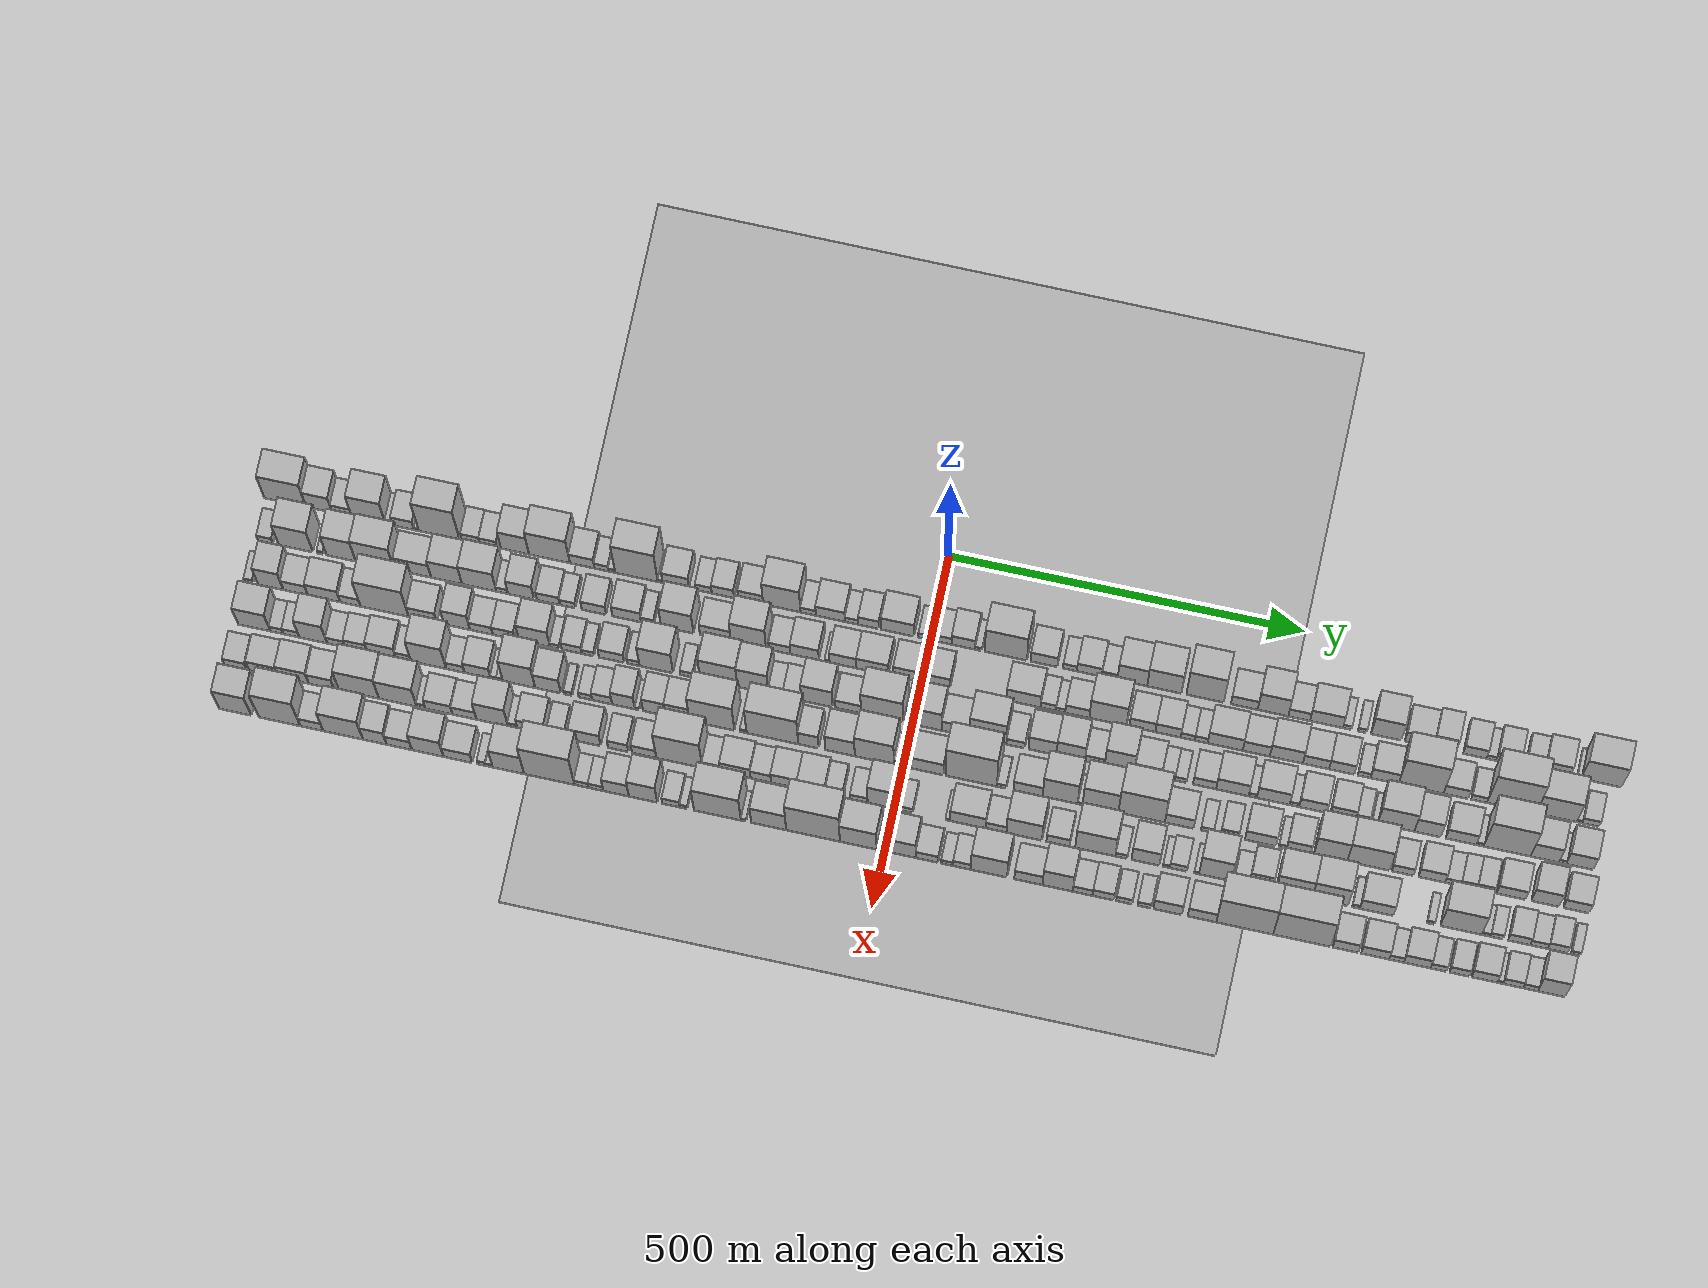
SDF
<?xml version="1.0" encoding="utf-8"?>

<sdf version="1.6">

   <world name="default">

      <gui fullscreen="0">

         <camera name="user_camera">

            <pose>-15 0 4.57585 0 0 0</pose>

            <view_controller>orbit</view_controller>

         </camera>

      </gui>

      <scene>

         <sky>

           <clouds>

             <speed>12</speed>

           </clouds>

         </sky>

         <ambient>0.4 0.4 0.4 1</ambient>

         <background>0.7 0.7 0.7 1</background>

         <shadows>1</shadows>

      </scene>

      <gravity>0 0 -9.8066</gravity>

      <magnetic_field>6e-06 2.3e-05 -4.2e-05</magnetic_field>

      <physics default="0" name="default_physics" type="ode">

         <ode>

            <solver>

               <type>quick</type>

               <iters>10</iters>

               <sor>1.0</sor>

               <use_dynamic_moi_rescaling>0</use_dynamic_moi_rescaling>

            </solver>

            <constraints>

               <cfm>0</cfm>

               <erp>0.2</erp>

               <contact_max_correcting_vel>100</contact_max_correcting_vel>

               <contact_surface_layer>0.001</contact_surface_layer>

            </constraints>

         </ode>

         <max_step_size>0.004</max_step_size>

         <real_time_factor>1</real_time_factor>

         <real_time_update_rate>250</real_time_update_rate>

      </physics>

      <light name="sun" type="directional">

         <cast_shadows>1</cast_shadows>

         <pose>0 0 10 0 0 0</pose>

         <diffuse>0.8 0.8 0.8 1</diffuse>

         <specular>0.2 0.2 0.2 1</specular>

         <attenuation>

            <range>1000</range>

            <constant>0.9</constant>

            <linear>0.01</linear>

            <quadratic>0.001</quadratic>

         </attenuation>

         <direction>-0.5 0.1 -0.9</direction>

      </light>

      <include>

         <name>ground_plane_1</name>

         <uri>model://HANNAS_ground_plane</uri>

         <pose>0 0 0  0 0 0</pose>

      </include>

      <include>

         <name>ground_plane_2</name>

         <uri>model://HANNAS_ground_plane</uri>

         <pose>100 0 0  0 0 0</pose>

      </include>

      <model name="building_1">

         <static>1</static>

         <pose frame="">100.0000 -910.4842 0 0.000000 0.000000 0.000000</pose>

         <link name="link">

            <pose frame="">0 0 75.00 0 0 0</pose>

            <collision name="collision">

               <geometry>

                  <box>

                     <size>40.0000 59.0317 150.0000</size>

                  </box>

               </geometry>

               <max_contacts>10</max_contacts>

               <surface>

                  <contact>

                     <ode/>

                  </contact>

                  <bounce/>

                  <friction>

                     <torsional>

                        <ode/>

                     </torsional>

                     <ode/>

                  </friction>

               </surface>

            </collision>

            <visual name="visual">

               <cast_shadows>0</cast_shadows>

               <geometry>

                  <box>

                     <size>40.0000 59.0317 150.0000</size>

                  </box>

               </geometry>

               <material>

                  <script>

                     <uri>model://HANNAS_wall/materials/scripts</uri>

                     <uri>model://HANNAS_wall/materials/textures</uri>

                     <name>vrc/HANNAS_wall</name>

                  </script>

               </material>

            </visual>

            <self_collide>0</self_collide>

            <enable_wind>0</enable_wind>

            <kinematic>0</kinematic>

         </link>

      </model>

      <model name="building_2">

         <static>1</static>

         <pose frame="">100.0000 -862.5990 0 0.000000 0.000000 0.000000</pose>

         <link name="link">

            <pose frame="">0 0 49.50 0 0 0</pose>

            <collision name="collision">

               <geometry>

                  <box>

                     <size>40.0000 36.7386 99.0000</size>

                  </box>

               </geometry>

               <max_contacts>10</max_contacts>

               <surface>

                  <contact>

                     <ode/>

                  </contact>

                  <bounce/>

                  <friction>

                     <torsional>

                        <ode/>

                     </torsional>

                     <ode/>

                  </friction>

               </surface>

            </collision>

            <visual name="visual">

               <cast_shadows>0</cast_shadows>

               <geometry>

                  <box>

                     <size>40.0000 36.7386 99.0000</size>

                  </box>

               </geometry>

               <material>

                  <script>

                     <uri>model://HANNAS_wall/materials/scripts</uri>

                     <uri>model://HANNAS_wall/materials/textures</uri>

                     <name>vrc/HANNAS_wall</name>

                  </script>

               </material>

            </visual>

            <self_collide>0</self_collide>

            <enable_wind>0</enable_wind>

            <kinematic>0</kinematic>

         </link>

      </model>

      <model name="building_3">

         <static>1</static>

         <pose frame="">100.0000 -830.4726 0 0.000000 0.000000 0.000000</pose>

         <link name="link">

            <pose frame="">0 0 25.50 0 0 0</pose>

            <collision name="collision">

               <geometry>

                  <box>

                     <size>40.0000 27.5144 51.0000</size>

                  </box>

               </geometry>

               <max_contacts>10</max_contacts>

               <surface>

                  <contact>

                     <ode/>

                  </contact>

                  <bounce/>

                  <friction>

                     <torsional>

                        <ode/>

                     </torsional>

                     <ode/>

                  </friction>

               </surface>

            </collision>

            <visual name="visual">

               <cast_shadows>0</cast_shadows>

               <geometry>

                  <box>

                     <size>40.0000 27.5144 51.0000</size>

                  </box>

               </geometry>

               <material>

                  <script>

                     <uri>model://HANNAS_wall/materials/scripts</uri>

                     <uri>model://HANNAS_wall/materials/textures</uri>

                     <name>vrc/HANNAS_wall</name>

                  </script>

               </material>

            </visual>

            <self_collide>0</self_collide>

            <enable_wind>0</enable_wind>

            <kinematic>0</kinematic>

         </link>

      </model>

      <model name="building_4">

         <static>1</static>

         <pose frame="">100.0000 -792.7981 0 0.000000 0.000000 0.000000</pose>

         <link name="link">

            <pose frame="">0 0 70.50 0 0 0</pose>

            <collision name="collision">

               <geometry>

                  <box>

                     <size>40.0000 47.8345 141.0000</size>

                  </box>

               </geometry>

               <max_contacts>10</max_contacts>

               <surface>

                  <contact>

                     <ode/>

                  </contact>

                  <bounce/>

                  <friction>

                     <torsional>

                        <ode/>

                     </torsional>

                     <ode/>

                  </friction>

               </surface>

            </collision>

            <visual name="visual">

               <cast_shadows>0</cast_shadows>

               <geometry>

                  <box>

                     <size>40.0000 47.8345 141.0000</size>

                  </box>

               </geometry>

               <material>

                  <script>

                     <uri>model://HANNAS_wall/materials/scripts</uri>

                     <uri>model://HANNAS_wall/materials/textures</uri>

                     <name>vrc/HANNAS_wall</name>

                  </script>

               </material>

            </visual>

            <self_collide>0</self_collide>

            <enable_wind>0</enable_wind>

            <kinematic>0</kinematic>

         </link>

      </model>

      <model name="building_5">

         <static>1</static>

         <pose frame="">100.0000 -763.9327 0 0.000000 0.000000 0.000000</pose>

         <link name="link">

            <pose frame="">0 0 12.00 0 0 0</pose>

            <collision name="collision">

               <geometry>

                  <box>

                     <size>40.0000 9.8963 24.0000</size>

                  </box>

               </geometry>

               <max_contacts>10</max_contacts>

               <surface>

                  <contact>

                     <ode/>

                  </contact>

                  <bounce/>

                  <friction>

                     <torsional>

                        <ode/>

                     </torsional>

                     <ode/>

                  </friction>

               </surface>

            </collision>

            <visual name="visual">

               <cast_shadows>0</cast_shadows>

               <geometry>

                  <box>

                     <size>40.0000 9.8963 24.0000</size>

                  </box>

               </geometry>

               <material>

                  <script>

                     <uri>model://HANNAS_wall/materials/scripts</uri>

                     <uri>model://HANNAS_wall/materials/textures</uri>

                     <name>vrc/HANNAS_wall</name>

                  </script>

               </material>

            </visual>

            <self_collide>0</self_collide>

            <enable_wind>0</enable_wind>

            <kinematic>0</kinematic>

         </link>

      </model>

      <model name="building_6">

         <static>1</static>

         <pose frame="">100.0000 -743.7237 0 0.000000 0.000000 0.000000</pose>

         <link name="link">

            <pose frame="">0 0 28.50 0 0 0</pose>

            <collision name="collision">

               <geometry>

                  <box>

                     <size>40.0000 30.5218 57.0000</size>

                  </box>

               </geometry>

               <max_contacts>10</max_contacts>

               <surface>

                  <contact>

                     <ode/>

                  </contact>

                  <bounce/>

                  <friction>

                     <torsional>

                        <ode/>

                     </torsional>

                     <ode/>

                  </friction>

               </surface>

            </collision>

            <visual name="visual">

               <cast_shadows>0</cast_shadows>

               <geometry>

                  <box>

                     <size>40.0000 30.5218 57.0000</size>

                  </box>

               </geometry>

               <material>

                  <script>

                     <uri>model://HANNAS_wall/materials/scripts</uri>

                     <uri>model://HANNAS_wall/materials/textures</uri>

                     <name>vrc/HANNAS_wall</name>

                  </script>

               </material>

            </visual>

            <self_collide>0</self_collide>

            <enable_wind>0</enable_wind>

            <kinematic>0</kinematic>

         </link>

      </model>

      <model name="building_7">

         <static>1</static>

         <pose frame="">100.0000 -725.1394 0 0.000000 0.000000 0.000000</pose>

         <link name="link">

            <pose frame="">0 0 7.50 0 0 0</pose>

            <collision name="collision">

               <geometry>

                  <box>

                     <size>40.0000 6.6468 15.0000</size>

                  </box>

               </geometry>

               <max_contacts>10</max_contacts>

               <surface>

                  <contact>

                     <ode/>

                  </contact>

                  <bounce/>

                  <friction>

                     <torsional>

                        <ode/>

                     </torsional>

                     <ode/>

                  </friction>

               </surface>

            </collision>

            <visual name="visual">

               <cast_shadows>0</cast_shadows>

               <geometry>

                  <box>

                     <size>40.0000 6.6468 15.0000</size>

                  </box>

               </geometry>

               <material>

                  <script>

                     <uri>model://HANNAS_wall/materials/scripts</uri>

                     <uri>model://HANNAS_wall/materials/textures</uri>

                     <name>vrc/HANNAS_wall</name>

                  </script>

               </material>

            </visual>

            <self_collide>0</self_collide>

            <enable_wind>0</enable_wind>

            <kinematic>0</kinematic>

         </link>

      </model>

      <model name="building_8">

         <static>1</static>

         <pose frame="">100.0000 -693.0077 0 0.000000 0.000000 0.000000</pose>

         <link name="link">

            <pose frame="">0 0 96.00 0 0 0</pose>

            <collision name="collision">

               <geometry>

                  <box>

                     <size>40.0000 57.6166 192.0000</size>

                  </box>

               </geometry>

               <max_contacts>10</max_contacts>

               <surface>

                  <contact>

                     <ode/>

                  </contact>

                  <bounce/>

                  <friction>

                     <torsional>

                        <ode/>

                     </torsional>

                     <ode/>

                  </friction>

               </surface>

            </collision>

            <visual name="visual">

               <cast_shadows>0</cast_shadows>

               <geometry>

                  <box>

                     <size>40.0000 57.6166 192.0000</size>

                  </box>

               </geometry>

               <material>

                  <script>

                     <uri>model://HANNAS_wall/materials/scripts</uri>

                     <uri>model://HANNAS_wall/materials/textures</uri>

                     <name>vrc/HANNAS_wall</name>

                  </script>

               </material>

            </visual>

            <self_collide>0</self_collide>

            <enable_wind>0</enable_wind>

            <kinematic>0</kinematic>

         </link>

      </model>

      <model name="building_9">

         <static>1</static>

         <pose frame="">100.0000 -648.4528 0 0.000000 0.000000 0.000000</pose>

         <link name="link">

            <pose frame="">0 0 22.50 0 0 0</pose>

            <collision name="collision">

               <geometry>

                  <box>

                     <size>40.0000 25.4932 45.0000</size>

                  </box>

               </geometry>

               <max_contacts>10</max_contacts>

               <surface>

                  <contact>

                     <ode/>

                  </contact>

                  <bounce/>

                  <friction>

                     <torsional>

                        <ode/>

                     </torsional>

                     <ode/>

                  </friction>

               </surface>

            </collision>

            <visual name="visual">

               <cast_shadows>0</cast_shadows>

               <geometry>

                  <box>

                     <size>40.0000 25.4932 45.0000</size>

                  </box>

               </geometry>

               <material>

                  <script>

                     <uri>model://HANNAS_wall/materials/scripts</uri>

                     <uri>model://HANNAS_wall/materials/textures</uri>

                     <name>vrc/HANNAS_wall</name>

                  </script>

               </material>

            </visual>

            <self_collide>0</self_collide>

            <enable_wind>0</enable_wind>

            <kinematic>0</kinematic>

         </link>

      </model>

      <model name="building_10">

         <static>1</static>

         <pose frame="">100.0000 -623.3817 0 0.000000 0.000000 0.000000</pose>

         <link name="link">

            <pose frame="">0 0 21.00 0 0 0</pose>

            <collision name="collision">

               <geometry>

                  <box>

                     <size>40.0000 24.6492 42.0000</size>

                  </box>

               </geometry>

               <max_contacts>10</max_contacts>

               <surface>

                  <contact>

                     <ode/>

                  </contact>

                  <bounce/>

                  <friction>

                     <torsional>

                        <ode/>

                     </torsional>

                     <ode/>

                  </friction>

               </surface>

            </collision>

            <visual name="visual">

               <cast_shadows>0</cast_shadows>

               <geometry>

                  <box>

                     <size>40.0000 24.6492 42.0000</size>

                  </box>

               </geometry>

               <material>

                  <script>

                     <uri>model://HANNAS_wall/materials/scripts</uri>

                     <uri>model://HANNAS_wall/materials/textures</uri>

                     <name>vrc/HANNAS_wall</name>

                  </script>

               </material>

            </visual>

            <self_collide>0</self_collide>

            <enable_wind>0</enable_wind>

            <kinematic>0</kinematic>

         </link>

      </model>

      <model name="building_11">

         <static>1</static>

         <pose frame="">100.0000 -586.1193 0 0.000000 0.000000 0.000000</pose>

         <link name="link">

            <pose frame="">0 0 58.50 0 0 0</pose>

            <collision name="collision">

               <geometry>

                  <box>

                     <size>40.0000 39.8756 117.0000</size>

                  </box>

               </geometry>

               <max_contacts>10</max_contacts>

               <surface>

                  <contact>

                     <ode/>

                  </contact>

                  <bounce/>

                  <friction>

                     <torsional>

                        <ode/>

                     </torsional>

                     <ode/>

                  </friction>

               </surface>

            </collision>

            <visual name="visual">

               <cast_shadows>0</cast_shadows>

               <geometry>

                  <box>

                     <size>40.0000 39.8756 117.0000</size>

                  </box>

               </geometry>

               <material>

                  <script>

                     <uri>model://HANNAS_wall/materials/scripts</uri>

                     <uri>model://HANNAS_wall/materials/textures</uri>

                     <name>vrc/HANNAS_wall</name>

                  </script>

               </material>

            </visual>

            <self_collide>0</self_collide>

            <enable_wind>0</enable_wind>

            <kinematic>0</kinematic>

         </link>

      </model>

      <model name="building_12">

         <static>1</static>

         <pose frame="">100.0000 -537.3972 0 0.000000 0.000000 0.000000</pose>

         <link name="link">

            <pose frame="">0 0 78.00 0 0 0</pose>

            <collision name="collision">

               <geometry>

                  <box>

                     <size>40.0000 57.5685 156.0000</size>

                  </box>

               </geometry>

               <max_contacts>10</max_contacts>

               <surface>

                  <contact>

                     <ode/>

                  </contact>

                  <bounce/>

                  <friction>

                     <torsional>

                        <ode/>

                     </torsional>

                     <ode/>

                  </friction>

               </surface>

            </collision>

            <visual name="visual">

               <cast_shadows>0</cast_shadows>

               <geometry>

                  <box>

                     <size>40.0000 57.5685 156.0000</size>

                  </box>

               </geometry>

               <material>

                  <script>

                     <uri>model://HANNAS_wall/materials/scripts</uri>

                     <uri>model://HANNAS_wall/materials/textures</uri>

                     <name>vrc/HANNAS_wall</name>

                  </script>

               </material>

            </visual>

            <self_collide>0</self_collide>

            <enable_wind>0</enable_wind>

            <kinematic>0</kinematic>

         </link>

      </model>

      <model name="building_13">

         <static>1</static>

         <pose frame="">100.0000 -491.3248 0 0.000000 0.000000 0.000000</pose>

         <link name="link">

            <pose frame="">0 0 31.50 0 0 0</pose>

            <collision name="collision">

               <geometry>

                  <box>

                     <size>40.0000 34.5762 63.0000</size>

                  </box>

               </geometry>

               <max_contacts>10</max_contacts>

               <surface>

                  <contact>

                     <ode/>

                  </contact>

                  <bounce/>

                  <friction>

                     <torsional>

                        <ode/>

                     </torsional>

                     <ode/>

                  </friction>

               </surface>

            </collision>

            <visual name="visual">

               <cast_shadows>0</cast_shadows>

               <geometry>

                  <box>

                     <size>40.0000 34.5762 63.0000</size>

                  </box>

               </geometry>

               <material>

                  <script>

                     <uri>model://HANNAS_wall/materials/scripts</uri>

                     <uri>model://HANNAS_wall/materials/textures</uri>

                     <name>vrc/HANNAS_wall</name>

                  </script>

               </material>

            </visual>

            <self_collide>0</self_collide>

            <enable_wind>0</enable_wind>

            <kinematic>0</kinematic>

         </link>

      </model>

      <model name="building_14">

         <static>1</static>

         <pose frame="">100.0000 -464.2556 0 0.000000 0.000000 0.000000</pose>

         <link name="link">

            <pose frame="">0 0 18.00 0 0 0</pose>

            <collision name="collision">

               <geometry>

                  <box>

                     <size>40.0000 19.5621 36.0000</size>

                  </box>

               </geometry>

               <max_contacts>10</max_contacts>

               <surface>

                  <contact>

                     <ode/>

                  </contact>

                  <bounce/>

                  <friction>

                     <torsional>

                        <ode/>

                     </torsional>

                     <ode/>

                  </friction>

               </surface>

            </collision>

            <visual name="visual">

               <cast_shadows>0</cast_shadows>

               <geometry>

                  <box>

                     <size>40.0000 19.5621 36.0000</size>

                  </box>

               </geometry>

               <material>

                  <script>

                     <uri>model://HANNAS_wall/materials/scripts</uri>

                     <uri>model://HANNAS_wall/materials/textures</uri>

                     <name>vrc/HANNAS_wall</name>

                  </script>

               </material>

            </visual>

            <self_collide>0</self_collide>

            <enable_wind>0</enable_wind>

            <kinematic>0</kinematic>

         </link>

      </model>

      <model name="building_15">

         <static>1</static>

         <pose frame="">100.0000 -449.6534 0 0.000000 0.000000 0.000000</pose>

         <link name="link">

            <pose frame="">0 0 10.50 0 0 0</pose>

            <collision name="collision">

               <geometry>

                  <box>

                     <size>40.0000 9.6423 21.0000</size>

                  </box>

               </geometry>

               <max_contacts>10</max_contacts>

               <surface>

                  <contact>

                     <ode/>

                  </contact>

                  <bounce/>

                  <friction>

                     <torsional>

                        <ode/>

                     </torsional>

                     <ode/>

                  </friction>

               </surface>

            </collision>

            <visual name="visual">

               <cast_shadows>0</cast_shadows>

               <geometry>

                  <box>

                     <size>40.0000 9.6423 21.0000</size>

                  </box>

               </geometry>

               <material>

                  <script>

                     <uri>model://HANNAS_wall/materials/scripts</uri>

                     <uri>model://HANNAS_wall/materials/textures</uri>

                     <name>vrc/HANNAS_wall</name>

                  </script>

               </material>

            </visual>

            <self_collide>0</self_collide>

            <enable_wind>0</enable_wind>

            <kinematic>0</kinematic>

         </link>

      </model>

      <model name="building_16">

         <static>1</static>

         <pose frame="">100.0000 -414.7941 0 0.000000 0.000000 0.000000</pose>

         <link name="link">

            <pose frame="">0 0 96.00 0 0 0</pose>

            <collision name="collision">

               <geometry>

                  <box>

                     <size>40.0000 60.0765 192.0000</size>

                  </box>

               </geometry>

               <max_contacts>10</max_contacts>

               <surface>

                  <contact>

                     <ode/>

                  </contact>

                  <bounce/>

                  <friction>

                     <torsional>

                        <ode/>

                     </torsional>

                     <ode/>

                  </friction>

               </surface>

            </collision>

            <visual name="visual">

               <cast_shadows>0</cast_shadows>

               <geometry>

                  <box>

                     <size>40.0000 60.0765 192.0000</size>

                  </box>

               </geometry>

               <material>

                  <script>

                     <uri>model://HANNAS_wall/materials/scripts</uri>

                     <uri>model://HANNAS_wall/materials/textures</uri>

                     <name>vrc/HANNAS_wall</name>

                  </script>

               </material>

            </visual>

            <self_collide>0</self_collide>

            <enable_wind>0</enable_wind>

            <kinematic>0</kinematic>

         </link>

      </model>

      <model name="building_17">

         <static>1</static>

         <pose frame="">100.0000 -381.3917 0 0.000000 0.000000 0.000000</pose>

         <link name="link">

            <pose frame="">0 0 7.50 0 0 0</pose>

            <collision name="collision">

               <geometry>

                  <box>

                     <size>40.0000 6.7281 15.0000</size>

                  </box>

               </geometry>

               <max_contacts>10</max_contacts>

               <surface>

                  <contact>

                     <ode/>

                  </contact>

                  <bounce/>

                  <friction>

                     <torsional>

                        <ode/>

                     </torsional>

                     <ode/>

                  </friction>

               </surface>

            </collision>

            <visual name="visual">

               <cast_shadows>0</cast_shadows>

               <geometry>

                  <box>

                     <size>40.0000 6.7281 15.0000</size>

                  </box>

               </geometry>

               <material>

                  <script>

                     <uri>model://HANNAS_wall/materials/scripts</uri>

                     <uri>model://HANNAS_wall/materials/textures</uri>

                     <name>vrc/HANNAS_wall</name>

                  </script>

               </material>

            </visual>

            <self_collide>0</self_collide>

            <enable_wind>0</enable_wind>

            <kinematic>0</kinematic>

         </link>

      </model>

      <model name="building_18">

         <static>1</static>

         <pose frame="">100.0000 -359.4194 0 0.000000 0.000000 0.000000</pose>

         <link name="link">

            <pose frame="">0 0 36.00 0 0 0</pose>

            <collision name="collision">

               <geometry>

                  <box>

                     <size>40.0000 37.2165 72.0000</size>

                  </box>

               </geometry>

               <max_contacts>10</max_contacts>

               <surface>

                  <contact>

                     <ode/>

                  </contact>

                  <bounce/>

                  <friction>

                     <torsional>

                        <ode/>

                     </torsional>

                     <ode/>

                  </friction>

               </surface>

            </collision>

            <visual name="visual">

               <cast_shadows>0</cast_shadows>

               <geometry>

                  <box>

                     <size>40.0000 37.2165 72.0000</size>

                  </box>

               </geometry>

               <material>

                  <script>

                     <uri>model://HANNAS_wall/materials/scripts</uri>

                     <uri>model://HANNAS_wall/materials/textures</uri>

                     <name>vrc/HANNAS_wall</name>

                  </script>

               </material>

            </visual>

            <self_collide>0</self_collide>

            <enable_wind>0</enable_wind>

            <kinematic>0</kinematic>

         </link>

      </model>

      <model name="building_19">

         <static>1</static>

         <pose frame="">100.0000 -320.2997 0 0.000000 0.000000 0.000000</pose>

         <link name="link">

            <pose frame="">0 0 21.00 0 0 0</pose>

            <collision name="collision">

               <geometry>

                  <box>

                     <size>40.0000 23.0229 42.0000</size>

                  </box>

               </geometry>

               <max_contacts>10</max_contacts>

               <surface>

                  <contact>

                     <ode/>

                  </contact>

                  <bounce/>

                  <friction>

                     <torsional>

                        <ode/>

                     </torsional>

                     <ode/>

                  </friction>

               </surface>

            </collision>

            <visual name="visual">

               <cast_shadows>0</cast_shadows>

               <geometry>

                  <box>

                     <size>40.0000 23.0229 42.0000</size>

                  </box>

               </geometry>

               <material>

                  <script>

                     <uri>model://HANNAS_wall/materials/scripts</uri>

                     <uri>model://HANNAS_wall/materials/textures</uri>

                     <name>vrc/HANNAS_wall</name>

                  </script>

               </material>

            </visual>

            <self_collide>0</self_collide>

            <enable_wind>0</enable_wind>

            <kinematic>0</kinematic>

         </link>

      </model>

      <model name="building_20">

         <static>1</static>

         <pose frame="">100.0000 -293.1393 0 0.000000 0.000000 0.000000</pose>

         <link name="link">

            <pose frame="">0 0 28.50 0 0 0</pose>

            <collision name="collision">

               <geometry>

                  <box>

                     <size>40.0000 31.2978 57.0000</size>

                  </box>

               </geometry>

               <max_contacts>10</max_contacts>

               <surface>

                  <contact>

                     <ode/>

                  </contact>

                  <bounce/>

                  <friction>

                     <torsional>

                        <ode/>

                     </torsional>

                     <ode/>

                  </friction>

               </surface>

            </collision>

            <visual name="visual">

               <cast_shadows>0</cast_shadows>

               <geometry>

                  <box>

                     <size>40.0000 31.2978 57.0000</size>

                  </box>

               </geometry>

               <material>

                  <script>

                     <uri>model://HANNAS_wall/materials/scripts</uri>

                     <uri>model://HANNAS_wall/materials/textures</uri>

                     <name>vrc/HANNAS_wall</name>

                  </script>

               </material>

            </visual>

            <self_collide>0</self_collide>

            <enable_wind>0</enable_wind>

            <kinematic>0</kinematic>

         </link>

      </model>

      <model name="building_21">

         <static>1</static>

         <pose frame="">100.0000 -254.0097 0 0.000000 0.000000 0.000000</pose>

         <link name="link">

            <pose frame="">0 0 31.50 0 0 0</pose>

            <collision name="collision">

               <geometry>

                  <box>

                     <size>40.0000 34.9615 63.0000</size>

                  </box>

               </geometry>

               <max_contacts>10</max_contacts>

               <surface>

                  <contact>

                     <ode/>

                  </contact>

                  <bounce/>

                  <friction>

                     <torsional>

                        <ode/>

                     </torsional>

                     <ode/>

                  </friction>

               </surface>

            </collision>

            <visual name="visual">

               <cast_shadows>0</cast_shadows>

               <geometry>

                  <box>

                     <size>40.0000 34.9615 63.0000</size>

                  </box>

               </geometry>

               <material>

                  <script>

                     <uri>model://HANNAS_wall/materials/scripts</uri>

                     <uri>model://HANNAS_wall/materials/textures</uri>

                     <name>vrc/HANNAS_wall</name>

                  </script>

               </material>

            </visual>

            <self_collide>0</self_collide>

            <enable_wind>0</enable_wind>

            <kinematic>0</kinematic>

         </link>

      </model>

      <model name="building_22">

         <static>1</static>

         <pose frame="">100.0000 -210.2316 0 0.000000 0.000000 0.000000</pose>

         <link name="link">

            <pose frame="">0 0 75.00 0 0 0</pose>

            <collision name="collision">

               <geometry>

                  <box>

                     <size>40.0000 52.5947 150.0000</size>

                  </box>

               </geometry>

               <max_contacts>10</max_contacts>

               <surface>

                  <contact>

                     <ode/>

                  </contact>

                  <bounce/>

                  <friction>

                     <torsional>

                        <ode/>

                     </torsional>

                     <ode/>

                  </friction>

               </surface>

            </collision>

            <visual name="visual">

               <cast_shadows>0</cast_shadows>

               <geometry>

                  <box>

                     <size>40.0000 52.5947 150.0000</size>

                  </box>

               </geometry>

               <material>

                  <script>

                     <uri>model://HANNAS_wall/materials/scripts</uri>

                     <uri>model://HANNAS_wall/materials/textures</uri>

                     <name>vrc/HANNAS_wall</name>

                  </script>

               </material>

            </visual>

            <self_collide>0</self_collide>

            <enable_wind>0</enable_wind>

            <kinematic>0</kinematic>

         </link>

      </model>

      <model name="building_23">

         <static>1</static>

         <pose frame="">100.0000 -173.1768 0 0.000000 0.000000 0.000000</pose>

         <link name="link">

            <pose frame="">0 0 18.00 0 0 0</pose>

            <collision name="collision">

               <geometry>

                  <box>

                     <size>40.0000 21.5149 36.0000</size>

                  </box>

               </geometry>

               <max_contacts>10</max_contacts>

               <surface>

                  <contact>

                     <ode/>

                  </contact>

                  <bounce/>

                  <friction>

                     <torsional>

                        <ode/>

                     </torsional>

                     <ode/>

                  </friction>

               </surface>

            </collision>

            <visual name="visual">

               <cast_shadows>0</cast_shadows>

               <geometry>

                  <box>

                     <size>40.0000 21.5149 36.0000</size>

                  </box>

               </geometry>

               <material>

                  <script>

                     <uri>model://HANNAS_wall/materials/scripts</uri>

                     <uri>model://HANNAS_wall/materials/textures</uri>

                     <name>vrc/HANNAS_wall</name>

                  </script>

               </material>

            </visual>

            <self_collide>0</self_collide>

            <enable_wind>0</enable_wind>

            <kinematic>0</kinematic>

         </link>

      </model>

      <model name="building_24">

         <static>1</static>

         <pose frame="">100.0000 -141.9982 0 0.000000 0.000000 0.000000</pose>

         <link name="link">

            <pose frame="">0 0 34.50 0 0 0</pose>

            <collision name="collision">

               <geometry>

                  <box>

                     <size>40.0000 40.8422 69.0000</size>

                  </box>

               </geometry>

               <max_contacts>10</max_contacts>

               <surface>

                  <contact>

                     <ode/>

                  </contact>

                  <bounce/>

                  <friction>

                     <torsional>

                        <ode/>

                     </torsional>

                     <ode/>

                  </friction>

               </surface>

            </collision>

            <visual name="visual">

               <cast_shadows>0</cast_shadows>

               <geometry>

                  <box>

                     <size>40.0000 40.8422 69.0000</size>

                  </box>

               </geometry>

               <material>

                  <script>

                     <uri>model://HANNAS_wall/materials/scripts</uri>

                     <uri>model://HANNAS_wall/materials/textures</uri>

                     <name>vrc/HANNAS_wall</name>

                  </script>

               </material>

            </visual>

            <self_collide>0</self_collide>

            <enable_wind>0</enable_wind>

            <kinematic>0</kinematic>

         </link>

      </model>

      <model name="building_25">

         <static>1</static>

         <pose frame="">100.0000 -112.1093 0 0.000000 0.000000 0.000000</pose>

         <link name="link">

            <pose frame="">0 0 16.50 0 0 0</pose>

            <collision name="collision">

               <geometry>

                  <box>

                     <size>40.0000 18.9356 33.0000</size>

                  </box>

               </geometry>

               <max_contacts>10</max_contacts>

               <surface>

                  <contact>

                     <ode/>

                  </contact>

                  <bounce/>

                  <friction>

                     <torsional>

                        <ode/>

                     </torsional>

                     <ode/>

                  </friction>

               </surface>

            </collision>

            <visual name="visual">

               <cast_shadows>0</cast_shadows>

               <geometry>

                  <box>

                     <size>40.0000 18.9356 33.0000</size>

                  </box>

               </geometry>

               <material>

                  <script>

                     <uri>model://HANNAS_wall/materials/scripts</uri>

                     <uri>model://HANNAS_wall/materials/textures</uri>

                     <name>vrc/HANNAS_wall</name>

                  </script>

               </material>

            </visual>

            <self_collide>0</self_collide>

            <enable_wind>0</enable_wind>

            <kinematic>0</kinematic>

         </link>

      </model>

      <model name="building_26">

         <static>1</static>

         <pose frame="">100.0000 -88.1540 0 0.000000 0.000000 0.000000</pose>

         <link name="link">

            <pose frame="">0 0 28.50 0 0 0</pose>

            <collision name="collision">

               <geometry>

                  <box>

                     <size>40.0000 28.9750 57.0000</size>

                  </box>

               </geometry>

               <max_contacts>10</max_contacts>

               <surface>

                  <contact>

                     <ode/>

                  </contact>

                  <bounce/>

                  <friction>

                     <torsional>

                        <ode/>

                     </torsional>

                     <ode/>

                  </friction>

               </surface>

            </collision>

            <visual name="visual">

               <cast_shadows>0</cast_shadows>

               <geometry>

                  <box>

                     <size>40.0000 28.9750 57.0000</size>

                  </box>

               </geometry>

               <material>

                  <script>

                     <uri>model://HANNAS_wall/materials/scripts</uri>

                     <uri>model://HANNAS_wall/materials/textures</uri>

                     <name>vrc/HANNAS_wall</name>

                  </script>

               </material>

            </visual>

            <self_collide>0</self_collide>

            <enable_wind>0</enable_wind>

            <kinematic>0</kinematic>

         </link>

      </model>

      <model name="building_27">

         <static>1</static>

         <pose frame="">100.0000 -47.4084 0 0.000000 0.000000 0.000000</pose>

         <link name="link">

            <pose frame="">0 0 43.50 0 0 0</pose>

            <collision name="collision">

               <geometry>

                  <box>

                     <size>40.0000 46.5162 87.0000</size>

                  </box>

               </geometry>

               <max_contacts>10</max_contacts>

               <surface>

                  <contact>

                     <ode/>

                  </contact>

                  <bounce/>

                  <friction>

                     <torsional>

                        <ode/>

                     </torsional>

                     <ode/>

                  </friction>

               </surface>

            </collision>

            <visual name="visual">

               <cast_shadows>0</cast_shadows>

               <geometry>

                  <box>

                     <size>40.0000 46.5162 87.0000</size>

                  </box>

               </geometry>

               <material>

                  <script>

                     <uri>model://HANNAS_wall/materials/scripts</uri>

                     <uri>model://HANNAS_wall/materials/textures</uri>

                     <name>vrc/HANNAS_wall</name>

                  </script>

               </material>

            </visual>

            <self_collide>0</self_collide>

            <enable_wind>0</enable_wind>

            <kinematic>0</kinematic>

         </link>

      </model>

      <model name="building_28">

         <static>1</static>

         <pose frame="">100.0000 -8.3645 0 0.000000 0.000000 0.000000</pose>

         <link name="link">

            <pose frame="">0 0 16.50 0 0 0</pose>

            <collision name="collision">

               <geometry>

                  <box>

                     <size>40.0000 19.5715 33.0000</size>

                  </box>

               </geometry>

               <max_contacts>10</max_contacts>

               <surface>

                  <contact>

                     <ode/>

                  </contact>

                  <bounce/>

                  <friction>

                     <torsional>

                        <ode/>

                     </torsional>

                     <ode/>

                  </friction>

               </surface>

            </collision>

            <visual name="visual">

               <cast_shadows>0</cast_shadows>

               <geometry>

                  <box>

                     <size>40.0000 19.5715 33.0000</size>

                  </box>

               </geometry>

               <material>

                  <script>

                     <uri>model://HANNAS_wall/materials/scripts</uri>

                     <uri>model://HANNAS_wall/materials/textures</uri>

                     <name>vrc/HANNAS_wall</name>

                  </script>

               </material>

            </visual>

            <self_collide>0</self_collide>

            <enable_wind>0</enable_wind>

            <kinematic>0</kinematic>

         </link>

      </model>

      <model name="building_29">

         <static>1</static>

         <pose frame="">100.0000 14.8589 0 0.000000 0.000000 0.000000</pose>

         <link name="link">

            <pose frame="">0 0 22.50 0 0 0</pose>

            <collision name="collision">

               <geometry>

                  <box>

                     <size>40.0000 26.8753 45.0000</size>

                  </box>

               </geometry>

               <max_contacts>10</max_contacts>

               <surface>

                  <contact>

                     <ode/>

                  </contact>

                  <bounce/>

                  <friction>

                     <torsional>

                        <ode/>

                     </torsional>

                     <ode/>

                  </friction>

               </surface>

            </collision>

            <visual name="visual">

               <cast_shadows>0</cast_shadows>

               <geometry>

                  <box>

                     <size>40.0000 26.8753 45.0000</size>

                  </box>

               </geometry>

               <material>

                  <script>

                     <uri>model://HANNAS_wall/materials/scripts</uri>

                     <uri>model://HANNAS_wall/materials/textures</uri>

                     <name>vrc/HANNAS_wall</name>

                  </script>

               </material>

            </visual>

            <self_collide>0</self_collide>

            <enable_wind>0</enable_wind>

            <kinematic>0</kinematic>

         </link>

      </model>

      <model name="building_30">

         <static>1</static>

         <pose frame="">100.0000 44.9759 0 0.000000 0.000000 0.000000</pose>

         <link name="link">

            <pose frame="">0 0 33.00 0 0 0</pose>

            <collision name="collision">

               <geometry>

                  <box>

                     <size>40.0000 33.3587 66.0000</size>

                  </box>

               </geometry>

               <max_contacts>10</max_contacts>

               <surface>

                  <contact>

                     <ode/>

                  </contact>

                  <bounce/>

                  <friction>

                     <torsional>

                        <ode/>

                     </torsional>

                     <ode/>

                  </friction>

               </surface>

            </collision>

            <visual name="visual">

               <cast_shadows>0</cast_shadows>

               <geometry>

                  <box>

                     <size>40.0000 33.3587 66.0000</size>

                  </box>

               </geometry>

               <material>

                  <script>

                     <uri>model://HANNAS_wall/materials/scripts</uri>

                     <uri>model://HANNAS_wall/materials/textures</uri>

                     <name>vrc/HANNAS_wall</name>

                  </script>

               </material>

            </visual>

            <self_collide>0</self_collide>

            <enable_wind>0</enable_wind>

            <kinematic>0</kinematic>

         </link>

      </model>

      <model name="building_31">

         <static>1</static>

         <pose frame="">100.0000 66.4421 0 0.000000 0.000000 0.000000</pose>

         <link name="link">

            <pose frame="">0 0 10.50 0 0 0</pose>

            <collision name="collision">

               <geometry>

                  <box>

                     <size>40.0000 9.5737 21.0000</size>

                  </box>

               </geometry>

               <max_contacts>10</max_contacts>

               <surface>

                  <contact>

                     <ode/>

                  </contact>

                  <bounce/>

                  <friction>

                     <torsional>

                        <ode/>

                     </torsional>

                     <ode/>

                  </friction>

               </surface>

            </collision>

            <visual name="visual">

               <cast_shadows>0</cast_shadows>

               <geometry>

                  <box>

                     <size>40.0000 9.5737 21.0000</size>

                  </box>

               </geometry>

               <material>

                  <script>

                     <uri>model://HANNAS_wall/materials/scripts</uri>

                     <uri>model://HANNAS_wall/materials/textures</uri>

                     <name>vrc/HANNAS_wall</name>

                  </script>

               </material>

            </visual>

            <self_collide>0</self_collide>

            <enable_wind>0</enable_wind>

            <kinematic>0</kinematic>

         </link>

      </model>

      <model name="building_32">

         <static>1</static>

         <pose frame="">100.0000 104.7939 0 0.000000 0.000000 0.000000</pose>

         <link name="link">

            <pose frame="">0 0 82.50 0 0 0</pose>

            <collision name="collision">

               <geometry>

                  <box>

                     <size>40.0000 59.1299 165.0000</size>

                  </box>

               </geometry>

               <max_contacts>10</max_contacts>

               <surface>

                  <contact>

                     <ode/>

                  </contact>

                  <bounce/>

                  <friction>

                     <torsional>

                        <ode/>

                     </torsional>

                     <ode/>

                  </friction>

               </surface>

            </collision>

            <visual name="visual">

               <cast_shadows>0</cast_shadows>

               <geometry>

                  <box>

                     <size>40.0000 59.1299 165.0000</size>

                  </box>

               </geometry>

               <material>

                  <script>

                     <uri>model://HANNAS_wall/materials/scripts</uri>

                     <uri>model://HANNAS_wall/materials/textures</uri>

                     <name>vrc/HANNAS_wall</name>

                  </script>

               </material>

            </visual>

            <self_collide>0</self_collide>

            <enable_wind>0</enable_wind>

            <kinematic>0</kinematic>

         </link>

      </model>

      <model name="building_33">

         <static>1</static>

         <pose frame="">100.0000 158.1552 0 0.000000 0.000000 0.000000</pose>

         <link name="link">

            <pose frame="">0 0 34.50 0 0 0</pose>

            <collision name="collision">

               <geometry>

                  <box>

                     <size>40.0000 37.5928 69.0000</size>

                  </box>

               </geometry>

               <max_contacts>10</max_contacts>

               <surface>

                  <contact>

                     <ode/>

                  </contact>

                  <bounce/>

                  <friction>

                     <torsional>

                        <ode/>

                     </torsional>

                     <ode/>

                  </friction>

               </surface>

            </collision>

            <visual name="visual">

               <cast_shadows>0</cast_shadows>

               <geometry>

                  <box>

                     <size>40.0000 37.5928 69.0000</size>

                  </box>

               </geometry>

               <material>

                  <script>

                     <uri>model://HANNAS_wall/materials/scripts</uri>

                     <uri>model://HANNAS_wall/materials/textures</uri>

                     <name>vrc/HANNAS_wall</name>

                  </script>

               </material>

            </visual>

            <self_collide>0</self_collide>

            <enable_wind>0</enable_wind>

            <kinematic>0</kinematic>

         </link>

      </model>

      <model name="building_34">

         <static>1</static>

         <pose frame="">100.0000 194.7335 0 0.000000 0.000000 0.000000</pose>

         <link name="link">

            <pose frame="">0 0 18.00 0 0 0</pose>

            <collision name="collision">

               <geometry>

                  <box>

                     <size>40.0000 19.5636 36.0000</size>

                  </box>

               </geometry>

               <max_contacts>10</max_contacts>

               <surface>

                  <contact>

                     <ode/>

                  </contact>

                  <bounce/>

                  <friction>

                     <torsional>

                        <ode/>

                     </torsional>

                     <ode/>

                  </friction>

               </surface>

            </collision>

            <visual name="visual">

               <cast_shadows>0</cast_shadows>

               <geometry>

                  <box>

                     <size>40.0000 19.5636 36.0000</size>

                  </box>

               </geometry>

               <material>

                  <script>

                     <uri>model://HANNAS_wall/materials/scripts</uri>

                     <uri>model://HANNAS_wall/materials/textures</uri>

                     <name>vrc/HANNAS_wall</name>

                  </script>

               </material>

            </visual>

            <self_collide>0</self_collide>

            <enable_wind>0</enable_wind>

            <kinematic>0</kinematic>

         </link>

      </model>

      <model name="building_35">

         <static>1</static>

         <pose frame="">100.0000 221.9439 0 0.000000 0.000000 0.000000</pose>

         <link name="link">

            <pose frame="">0 0 30.00 0 0 0</pose>

            <collision name="collision">

               <geometry>

                  <box>

                     <size>40.0000 34.8571 60.0000</size>

                  </box>

               </geometry>

               <max_contacts>10</max_contacts>

               <surface>

                  <contact>

                     <ode/>

                  </contact>

                  <bounce/>

                  <friction>

                     <torsional>

                        <ode/>

                     </torsional>

                     <ode/>

                  </friction>

               </surface>

            </collision>

            <visual name="visual">

               <cast_shadows>0</cast_shadows>

               <geometry>

                  <box>

                     <size>40.0000 34.8571 60.0000</size>

                  </box>

               </geometry>

               <material>

                  <script>

                     <uri>model://HANNAS_wall/materials/scripts</uri>

                     <uri>model://HANNAS_wall/materials/textures</uri>

                     <name>vrc/HANNAS_wall</name>

                  </script>

               </material>

            </visual>

            <self_collide>0</self_collide>

            <enable_wind>0</enable_wind>

            <kinematic>0</kinematic>

         </link>

      </model>

      <model name="building_36">

         <static>1</static>

         <pose frame="">100.0000 250.3359 0 0.000000 0.000000 0.000000</pose>

         <link name="link">

            <pose frame="">0 0 19.50 0 0 0</pose>

            <collision name="collision">

               <geometry>

                  <box>

                     <size>40.0000 21.9270 39.0000</size>

                  </box>

               </geometry>

               <max_contacts>10</max_contacts>

               <surface>

                  <contact>

                     <ode/>

                  </contact>

                  <bounce/>

                  <friction>

                     <torsional>

                        <ode/>

                     </torsional>

                     <ode/>

                  </friction>

               </surface>

            </collision>

            <visual name="visual">

               <cast_shadows>0</cast_shadows>

               <geometry>

                  <box>

                     <size>40.0000 21.9270 39.0000</size>

                  </box>

               </geometry>

               <material>

                  <script>

                     <uri>model://HANNAS_wall/materials/scripts</uri>

                     <uri>model://HANNAS_wall/materials/textures</uri>

                     <name>vrc/HANNAS_wall</name>

                  </script>

               </material>

            </visual>

            <self_collide>0</self_collide>

            <enable_wind>0</enable_wind>

            <kinematic>0</kinematic>

         </link>

      </model>

      <model name="building_37">

         <static>1</static>

         <pose frame="">100.0000 282.1764 0 0.000000 0.000000 0.000000</pose>

         <link name="link">

            <pose frame="">0 0 58.50 0 0 0</pose>

            <collision name="collision">

               <geometry>

                  <box>

                     <size>40.0000 41.7540 117.0000</size>

                  </box>

               </geometry>

               <max_contacts>10</max_contacts>

               <surface>

                  <contact>

                     <ode/>

                  </contact>

                  <bounce/>

                  <friction>

                     <torsional>

                        <ode/>

                     </torsional>

                     <ode/>

                  </friction>

               </surface>

            </collision>

            <visual name="visual">

               <cast_shadows>0</cast_shadows>

               <geometry>

                  <box>

                     <size>40.0000 41.7540 117.0000</size>

                  </box>

               </geometry>

               <material>

                  <script>

                     <uri>model://HANNAS_wall/materials/scripts</uri>

                     <uri>model://HANNAS_wall/materials/textures</uri>

                     <name>vrc/HANNAS_wall</name>

                  </script>

               </material>

            </visual>

            <self_collide>0</self_collide>

            <enable_wind>0</enable_wind>

            <kinematic>0</kinematic>

         </link>

      </model>

      <model name="building_38">

         <static>1</static>

         <pose frame="">100.0000 327.0272 0 0.000000 0.000000 0.000000</pose>

         <link name="link">

            <pose frame="">0 0 66.00 0 0 0</pose>

            <collision name="collision">

               <geometry>

                  <box>

                     <size>40.0000 47.9475 132.0000</size>

                  </box>

               </geometry>

               <max_contacts>10</max_contacts>

               <surface>

                  <contact>

                     <ode/>

                  </contact>

                  <bounce/>

                  <friction>

                     <torsional>

                        <ode/>

                     </torsional>

                     <ode/>

                  </friction>

               </surface>

            </collision>

            <visual name="visual">

               <cast_shadows>0</cast_shadows>

               <geometry>

                  <box>

                     <size>40.0000 47.9475 132.0000</size>

                  </box>

               </geometry>

               <material>

                  <script>

                     <uri>model://HANNAS_wall/materials/scripts</uri>

                     <uri>model://HANNAS_wall/materials/textures</uri>

                     <name>vrc/HANNAS_wall</name>

                  </script>

               </material>

            </visual>

            <self_collide>0</self_collide>

            <enable_wind>0</enable_wind>

            <kinematic>0</kinematic>

         </link>

      </model>

      <model name="building_39">

         <static>1</static>

         <pose frame="">100.0000 384.1953 0 0.000000 0.000000 0.000000</pose>

         <link name="link">

            <pose frame="">0 0 87.00 0 0 0</pose>

            <collision name="collision">

               <geometry>

                  <box>

                     <size>40.0000 52.3887 174.0000</size>

                  </box>

               </geometry>

               <max_contacts>10</max_contacts>

               <surface>

                  <contact>

                     <ode/>

                  </contact>

                  <bounce/>

                  <friction>

                     <torsional>

                        <ode/>

                     </torsional>

                     <ode/>

                  </friction>

               </surface>

            </collision>

            <visual name="visual">

               <cast_shadows>0</cast_shadows>

               <geometry>

                  <box>

                     <size>40.0000 52.3887 174.0000</size>

                  </box>

               </geometry>

               <material>

                  <script>

                     <uri>model://HANNAS_wall/materials/scripts</uri>

                     <uri>model://HANNAS_wall/materials/textures</uri>

                     <name>vrc/HANNAS_wall</name>

                  </script>

               </material>

            </visual>

            <self_collide>0</self_collide>

            <enable_wind>0</enable_wind>

            <kinematic>0</kinematic>

         </link>

      </model>

      <model name="building_40">

         <static>1</static>

         <pose frame="">100.0000 439.1417 0 0.000000 0.000000 0.000000</pose>

         <link name="link">

            <pose frame="">0 0 31.50 0 0 0</pose>

            <collision name="collision">

               <geometry>

                  <box>

                     <size>40.0000 37.5041 63.0000</size>

                  </box>

               </geometry>

               <max_contacts>10</max_contacts>

               <surface>

                  <contact>

                     <ode/>

                  </contact>

                  <bounce/>

                  <friction>

                     <torsional>

                        <ode/>

                     </torsional>

                     <ode/>

                  </friction>

               </surface>

            </collision>

            <visual name="visual">

               <cast_shadows>0</cast_shadows>

               <geometry>

                  <box>

                     <size>40.0000 37.5041 63.0000</size>

                  </box>

               </geometry>

               <material>

                  <script>

                     <uri>model://HANNAS_wall/materials/scripts</uri>

                     <uri>model://HANNAS_wall/materials/textures</uri>

                     <name>vrc/HANNAS_wall</name>

                  </script>

               </material>

            </visual>

            <self_collide>0</self_collide>

            <enable_wind>0</enable_wind>

            <kinematic>0</kinematic>

         </link>

      </model>

      <model name="building_41">

         <static>1</static>

         <pose frame="">100.0000 479.2729 0 0.000000 0.000000 0.000000</pose>

         <link name="link">

            <pose frame="">0 0 63.00 0 0 0</pose>

            <collision name="collision">

               <geometry>

                  <box>

                     <size>40.0000 42.7582 126.0000</size>

                  </box>

               </geometry>

               <max_contacts>10</max_contacts>

               <surface>

                  <contact>

                     <ode/>

                  </contact>

                  <bounce/>

                  <friction>

                     <torsional>

                        <ode/>

                     </torsional>

                     <ode/>

                  </friction>

               </surface>

            </collision>

            <visual name="visual">

               <cast_shadows>0</cast_shadows>

               <geometry>

                  <box>

                     <size>40.0000 42.7582 126.0000</size>

                  </box>

               </geometry>

               <material>

                  <script>

                     <uri>model://HANNAS_wall/materials/scripts</uri>

                     <uri>model://HANNAS_wall/materials/textures</uri>

                     <name>vrc/HANNAS_wall</name>

                  </script>

               </material>

            </visual>

            <self_collide>0</self_collide>

            <enable_wind>0</enable_wind>

            <kinematic>0</kinematic>

         </link>

      </model>

      <model name="building_42">

         <static>1</static>

         <pose frame="">100.0000 515.9443 0 0.000000 0.000000 0.000000</pose>

         <link name="link">

            <pose frame="">0 0 28.50 0 0 0</pose>

            <collision name="collision">

               <geometry>

                  <box>

                     <size>40.0000 30.5846 57.0000</size>

                  </box>

               </geometry>

               <max_contacts>10</max_contacts>

               <surface>

                  <contact>

                     <ode/>

                  </contact>

                  <bounce/>

                  <friction>

                     <torsional>

                        <ode/>

                     </torsional>

                     <ode/>

                  </friction>

               </surface>

            </collision>

            <visual name="visual">

               <cast_shadows>0</cast_shadows>

               <geometry>

                  <box>

                     <size>40.0000 30.5846 57.0000</size>

                  </box>

               </geometry>

               <material>

                  <script>

                     <uri>model://HANNAS_wall/materials/scripts</uri>

                     <uri>model://HANNAS_wall/materials/textures</uri>

                     <name>vrc/HANNAS_wall</name>

                  </script>

               </material>

            </visual>

            <self_collide>0</self_collide>

            <enable_wind>0</enable_wind>

            <kinematic>0</kinematic>

         </link>

      </model>

      <model name="building_43">

         <static>1</static>

         <pose frame="">100.0000 554.2611 0 0.000000 0.000000 0.000000</pose>

         <link name="link">

            <pose frame="">0 0 42.00 0 0 0</pose>

            <collision name="collision">

               <geometry>

                  <box>

                     <size>40.0000 46.0491 84.0000</size>

                  </box>

               </geometry>

               <max_contacts>10</max_contacts>

               <surface>

                  <contact>

                     <ode/>

                  </contact>

                  <bounce/>

                  <friction>

                     <torsional>

                        <ode/>

                     </torsional>

                     <ode/>

                  </friction>

               </surface>

            </collision>

            <visual name="visual">

               <cast_shadows>0</cast_shadows>

               <geometry>

                  <box>

                     <size>40.0000 46.0491 84.0000</size>

                  </box>

               </geometry>

               <material>

                  <script>

                     <uri>model://HANNAS_wall/materials/scripts</uri>

                     <uri>model://HANNAS_wall/materials/textures</uri>

                     <name>vrc/HANNAS_wall</name>

                  </script>

               </material>

            </visual>

            <self_collide>0</self_collide>

            <enable_wind>0</enable_wind>

            <kinematic>0</kinematic>

         </link>

      </model>

      <model name="building_44">

         <static>1</static>

         <pose frame="">100.0000 583.2948 0 0.000000 0.000000 0.000000</pose>

         <link name="link">

            <pose frame="">0 0 13.50 0 0 0</pose>

            <collision name="collision">

               <geometry>

                  <box>

                     <size>40.0000 12.0181 27.0000</size>

                  </box>

               </geometry>

               <max_contacts>10</max_contacts>

               <surface>

                  <contact>

                     <ode/>

                  </contact>

                  <bounce/>

                  <friction>

                     <torsional>

                        <ode/>

                     </torsional>

                     <ode/>

                  </friction>

               </surface>

            </collision>

            <visual name="visual">

               <cast_shadows>0</cast_shadows>

               <geometry>

                  <box>

                     <size>40.0000 12.0181 27.0000</size>

                  </box>

               </geometry>

               <material>

                  <script>

                     <uri>model://HANNAS_wall/materials/scripts</uri>

                     <uri>model://HANNAS_wall/materials/textures</uri>

                     <name>vrc/HANNAS_wall</name>

                  </script>

               </material>

            </visual>

            <self_collide>0</self_collide>

            <enable_wind>0</enable_wind>

            <kinematic>0</kinematic>

         </link>

      </model>

      <model name="building_45">

         <static>1</static>

         <pose frame="">100.0000 604.4444 0 0.000000 0.000000 0.000000</pose>

         <link name="link">

            <pose frame="">0 0 13.50 0 0 0</pose>

            <collision name="collision">

               <geometry>

                  <box>

                     <size>40.0000 12.2811 27.0000</size>

                  </box>

               </geometry>

               <max_contacts>10</max_contacts>

               <surface>

                  <contact>

                     <ode/>

                  </contact>

                  <bounce/>

                  <friction>

                     <torsional>

                        <ode/>

                     </torsional>

                     <ode/>

                  </friction>

               </surface>

            </collision>

            <visual name="visual">

               <cast_shadows>0</cast_shadows>

               <geometry>

                  <box>

                     <size>40.0000 12.2811 27.0000</size>

                  </box>

               </geometry>

               <material>

                  <script>

                     <uri>model://HANNAS_wall/materials/scripts</uri>

                     <uri>model://HANNAS_wall/materials/textures</uri>

                     <name>vrc/HANNAS_wall</name>

                  </script>

               </material>

            </visual>

            <self_collide>0</self_collide>

            <enable_wind>0</enable_wind>

            <kinematic>0</kinematic>

         </link>

      </model>

      <model name="building_46">

         <static>1</static>

         <pose frame="">100.0000 637.7683 0 0.000000 0.000000 0.000000</pose>

         <link name="link">

            <pose frame="">0 0 63.00 0 0 0</pose>

            <collision name="collision">

               <geometry>

                  <box>

                     <size>40.0000 42.3668 126.0000</size>

                  </box>

               </geometry>

               <max_contacts>10</max_contacts>

               <surface>

                  <contact>

                     <ode/>

                  </contact>

                  <bounce/>

                  <friction>

                     <torsional>

                        <ode/>

                     </torsional>

                     <ode/>

                  </friction>

               </surface>

            </collision>

            <visual name="visual">

               <cast_shadows>0</cast_shadows>

               <geometry>

                  <box>

                     <size>40.0000 42.3668 126.0000</size>

                  </box>

               </geometry>

               <material>

                  <script>

                     <uri>model://HANNAS_wall/materials/scripts</uri>

                     <uri>model://HANNAS_wall/materials/textures</uri>

                     <name>vrc/HANNAS_wall</name>

                  </script>

               </material>

            </visual>

            <self_collide>0</self_collide>

            <enable_wind>0</enable_wind>

            <kinematic>0</kinematic>

         </link>

      </model>

      <model name="building_47">

         <static>1</static>

         <pose frame="">100.0000 683.5927 0 0.000000 0.000000 0.000000</pose>

         <link name="link">

            <pose frame="">0 0 36.00 0 0 0</pose>

            <collision name="collision">

               <geometry>

                  <box>

                     <size>40.0000 39.2818 72.0000</size>

                  </box>

               </geometry>

               <max_contacts>10</max_contacts>

               <surface>

                  <contact>

                     <ode/>

                  </contact>

                  <bounce/>

                  <friction>

                     <torsional>

                        <ode/>

                     </torsional>

                     <ode/>

                  </friction>

               </surface>

            </collision>

            <visual name="visual">

               <cast_shadows>0</cast_shadows>

               <geometry>

                  <box>

                     <size>40.0000 39.2818 72.0000</size>

                  </box>

               </geometry>

               <material>

                  <script>

                     <uri>model://HANNAS_wall/materials/scripts</uri>

                     <uri>model://HANNAS_wall/materials/textures</uri>

                     <name>vrc/HANNAS_wall</name>

                  </script>

               </material>

            </visual>

            <self_collide>0</self_collide>

            <enable_wind>0</enable_wind>

            <kinematic>0</kinematic>

         </link>

      </model>

      <model name="building_48">

         <static>1</static>

         <pose frame="">100.0000 719.4059 0 0.000000 0.000000 0.000000</pose>

         <link name="link">

            <pose frame="">0 0 46.50 0 0 0</pose>

            <collision name="collision">

               <geometry>

                  <box>

                     <size>40.0000 32.3447 93.0000</size>

                  </box>

               </geometry>

               <max_contacts>10</max_contacts>

               <surface>

                  <contact>

                     <ode/>

                  </contact>

                  <bounce/>

                  <friction>

                     <torsional>

                        <ode/>

                     </torsional>

                     <ode/>

                  </friction>

               </surface>

            </collision>

            <visual name="visual">

               <cast_shadows>0</cast_shadows>

               <geometry>

                  <box>

                     <size>40.0000 32.3447 93.0000</size>

                  </box>

               </geometry>

               <material>

                  <script>

                     <uri>model://HANNAS_wall/materials/scripts</uri>

                     <uri>model://HANNAS_wall/materials/textures</uri>

                     <name>vrc/HANNAS_wall</name>

                  </script>

               </material>

            </visual>

            <self_collide>0</self_collide>

            <enable_wind>0</enable_wind>

            <kinematic>0</kinematic>

         </link>

      </model>

      <model name="building_49">

         <static>1</static>

         <pose frame="">100.0000 761.8796 0 0.000000 0.000000 0.000000</pose>

         <link name="link">

            <pose frame="">0 0 31.50 0 0 0</pose>

            <collision name="collision">

               <geometry>

                  <box>

                     <size>40.0000 32.6027 63.0000</size>

                  </box>

               </geometry>

               <max_contacts>10</max_contacts>

               <surface>

                  <contact>

                     <ode/>

                  </contact>

                  <bounce/>

                  <friction>

                     <torsional>

                        <ode/>

                     </torsional>

                     <ode/>

                  </friction>

               </surface>

            </collision>

            <visual name="visual">

               <cast_shadows>0</cast_shadows>

               <geometry>

                  <box>

                     <size>40.0000 32.6027 63.0000</size>

                  </box>

               </geometry>

               <material>

                  <script>

                     <uri>model://HANNAS_wall/materials/scripts</uri>

                     <uri>model://HANNAS_wall/materials/textures</uri>

                     <name>vrc/HANNAS_wall</name>

                  </script>

               </material>

            </visual>

            <self_collide>0</self_collide>

            <enable_wind>0</enable_wind>

            <kinematic>0</kinematic>

         </link>

      </model>

      <model name="building_50">

         <static>1</static>

         <pose frame="">100.0000 784.9142 0 0.000000 0.000000 0.000000</pose>

         <link name="link">

            <pose frame="">0 0 13.50 0 0 0</pose>

            <collision name="collision">

               <geometry>

                  <box>

                     <size>40.0000 13.4664 27.0000</size>

                  </box>

               </geometry>

               <max_contacts>10</max_contacts>

               <surface>

                  <contact>

                     <ode/>

                  </contact>

                  <bounce/>

                  <friction>

                     <torsional>

                        <ode/>

                     </torsional>

                     <ode/>

                  </friction>

               </surface>

            </collision>

            <visual name="visual">

               <cast_shadows>0</cast_shadows>

               <geometry>

                  <box>

                     <size>40.0000 13.4664 27.0000</size>

                  </box>

               </geometry>

               <material>

                  <script>

                     <uri>model://HANNAS_wall/materials/scripts</uri>

                     <uri>model://HANNAS_wall/materials/textures</uri>

                     <name>vrc/HANNAS_wall</name>

                  </script>

               </material>

            </visual>

            <self_collide>0</self_collide>

            <enable_wind>0</enable_wind>

            <kinematic>0</kinematic>

         </link>

      </model>

      <model name="building_51">

         <static>1</static>

         <pose frame="">100.0000 807.7742 0 0.000000 0.000000 0.000000</pose>

         <link name="link">

            <pose frame="">0 0 31.50 0 0 0</pose>

            <collision name="collision">

               <geometry>

                  <box>

                     <size>40.0000 32.2536 63.0000</size>

                  </box>

               </geometry>

               <max_contacts>10</max_contacts>

               <surface>

                  <contact>

                     <ode/>

                  </contact>

                  <bounce/>

                  <friction>

                     <torsional>

                        <ode/>

                     </torsional>

                     <ode/>

                  </friction>

               </surface>

            </collision>

            <visual name="visual">

               <cast_shadows>0</cast_shadows>

               <geometry>

                  <box>

                     <size>40.0000 32.2536 63.0000</size>

                  </box>

               </geometry>

               <material>

                  <script>

                     <uri>model://HANNAS_wall/materials/scripts</uri>

                     <uri>model://HANNAS_wall/materials/textures</uri>

                     <name>vrc/HANNAS_wall</name>

                  </script>

               </material>

            </visual>

            <self_collide>0</self_collide>

            <enable_wind>0</enable_wind>

            <kinematic>0</kinematic>

         </link>

      </model>

      <model name="building_52">

         <static>1</static>

         <pose frame="">100.0000 844.8449 0 0.000000 0.000000 0.000000</pose>

         <link name="link">

            <pose frame="">0 0 25.50 0 0 0</pose>

            <collision name="collision">

               <geometry>

                  <box>

                     <size>40.0000 25.8878 51.0000</size>

                  </box>

               </geometry>

               <max_contacts>10</max_contacts>

               <surface>

                  <contact>

                     <ode/>

                  </contact>

                  <bounce/>

                  <friction>

                     <torsional>

                        <ode/>

                     </torsional>

                     <ode/>

                  </friction>

               </surface>

            </collision>

            <visual name="visual">

               <cast_shadows>0</cast_shadows>

               <geometry>

                  <box>

                     <size>40.0000 25.8878 51.0000</size>

                  </box>

               </geometry>

               <material>

                  <script>

                     <uri>model://HANNAS_wall/materials/scripts</uri>

                     <uri>model://HANNAS_wall/materials/textures</uri>

                     <name>vrc/HANNAS_wall</name>

                  </script>

               </material>

            </visual>

            <self_collide>0</self_collide>

            <enable_wind>0</enable_wind>

            <kinematic>0</kinematic>

         </link>

      </model>

      <model name="building_53">

         <static>1</static>

         <pose frame="">100.0000 876.4943 0 0.000000 0.000000 0.000000</pose>

         <link name="link">

            <pose frame="">0 0 36.00 0 0 0</pose>

            <collision name="collision">

               <geometry>

                  <box>

                     <size>40.0000 37.4111 72.0000</size>

                  </box>

               </geometry>

               <max_contacts>10</max_contacts>

               <surface>

                  <contact>

                     <ode/>

                  </contact>

                  <bounce/>

                  <friction>

                     <torsional>

                        <ode/>

                     </torsional>

                     <ode/>

                  </friction>

               </surface>

            </collision>

            <visual name="visual">

               <cast_shadows>0</cast_shadows>

               <geometry>

                  <box>

                     <size>40.0000 37.4111 72.0000</size>

                  </box>

               </geometry>

               <material>

                  <script>

                     <uri>model://HANNAS_wall/materials/scripts</uri>

                     <uri>model://HANNAS_wall/materials/textures</uri>

                     <name>vrc/HANNAS_wall</name>

                  </script>

               </material>

            </visual>

            <self_collide>0</self_collide>

            <enable_wind>0</enable_wind>

            <kinematic>0</kinematic>

         </link>

      </model>

      <model name="building_54">

         <static>1</static>

         <pose frame="">100.0000 907.2479 0 0.000000 0.000000 0.000000</pose>

         <link name="link">

            <pose frame="">0 0 7.50 0 0 0</pose>

            <collision name="collision">

               <geometry>

                  <box>

                     <size>40.0000 6.0962 15.0000</size>

                  </box>

               </geometry>

               <max_contacts>10</max_contacts>

               <surface>

                  <contact>

                     <ode/>

                  </contact>

                  <bounce/>

                  <friction>

                     <torsional>

                        <ode/>

                     </torsional>

                     <ode/>

                  </friction>

               </surface>

            </collision>

            <visual name="visual">

               <cast_shadows>0</cast_shadows>

               <geometry>

                  <box>

                     <size>40.0000 6.0962 15.0000</size>

                  </box>

               </geometry>

               <material>

                  <script>

                     <uri>model://HANNAS_wall/materials/scripts</uri>

                     <uri>model://HANNAS_wall/materials/textures</uri>

                     <name>vrc/HANNAS_wall</name>

                  </script>

               </material>

            </visual>

            <self_collide>0</self_collide>

            <enable_wind>0</enable_wind>

            <kinematic>0</kinematic>

         </link>

      </model>

      <model name="building_55">

         <static>1</static>

         <pose frame="">100.0000 938.5832 0 0.000000 0.000000 0.000000</pose>

         <link name="link">

            <pose frame="">0 0 73.50 0 0 0</pose>

            <collision name="collision">

               <geometry>

                  <box>

                     <size>40.0000 56.5743 147.0000</size>

                  </box>

               </geometry>

               <max_contacts>10</max_contacts>

               <surface>

                  <contact>

                     <ode/>

                  </contact>

                  <bounce/>

                  <friction>

                     <torsional>

                        <ode/>

                     </torsional>

                     <ode/>

                  </friction>

               </surface>

            </collision>

            <visual name="visual">

               <cast_shadows>0</cast_shadows>

               <geometry>

                  <box>

                     <size>40.0000 56.5743 147.0000</size>

                  </box>

               </geometry>

               <material>

                  <script>

                     <uri>model://HANNAS_wall/materials/scripts</uri>

                     <uri>model://HANNAS_wall/materials/textures</uri>

                     <name>vrc/HANNAS_wall</name>

                  </script>

               </material>

            </visual>

            <self_collide>0</self_collide>

            <enable_wind>0</enable_wind>

            <kinematic>0</kinematic>

         </link>

      </model>

      <model name="building_56">

         <static>1</static>

         <pose frame="">160.0000 -924.4124 0 0.000000 0.000000 0.000000</pose>

         <link name="link">

            <pose frame="">0 0 18.00 0 0 0</pose>

            <collision name="collision">

               <geometry>

                  <box>

                     <size>40.0000 21.1751 36.0000</size>

                  </box>

               </geometry>

               <max_contacts>10</max_contacts>

               <surface>

                  <contact>

                     <ode/>

                  </contact>

                  <bounce/>

                  <friction>

                     <torsional>

                        <ode/>

                     </torsional>

                     <ode/>

                  </friction>

               </surface>

            </collision>

            <visual name="visual">

               <cast_shadows>0</cast_shadows>

               <geometry>

                  <box>

                     <size>40.0000 21.1751 36.0000</size>

                  </box>

               </geometry>

               <material>

                  <script>

                     <uri>model://HANNAS_wall/materials/scripts</uri>

                     <uri>model://HANNAS_wall/materials/textures</uri>

                     <name>vrc/HANNAS_wall</name>

                  </script>

               </material>

            </visual>

            <self_collide>0</self_collide>

            <enable_wind>0</enable_wind>

            <kinematic>0</kinematic>

         </link>

      </model>

      <model name="building_57">

         <static>1</static>

         <pose frame="">160.0000 -881.5369 0 0.000000 0.000000 0.000000</pose>

         <link name="link">

            <pose frame="">0 0 70.50 0 0 0</pose>

            <collision name="collision">

               <geometry>

                  <box>

                     <size>40.0000 48.5760 141.0000</size>

                  </box>

               </geometry>

               <max_contacts>10</max_contacts>

               <surface>

                  <contact>

                     <ode/>

                  </contact>

                  <bounce/>

                  <friction>

                     <torsional>

                        <ode/>

                     </torsional>

                     <ode/>

                  </friction>

               </surface>

            </collision>

            <visual name="visual">

               <cast_shadows>0</cast_shadows>

               <geometry>

                  <box>

                     <size>40.0000 48.5760 141.0000</size>

                  </box>

               </geometry>

               <material>

                  <script>

                     <uri>model://HANNAS_wall/materials/scripts</uri>

                     <uri>model://HANNAS_wall/materials/textures</uri>

                     <name>vrc/HANNAS_wall</name>

                  </script>

               </material>

            </visual>

            <self_collide>0</self_collide>

            <enable_wind>0</enable_wind>

            <kinematic>0</kinematic>

         </link>

      </model>

      <model name="building_58">

         <static>1</static>

         <pose frame="">160.0000 -846.8091 0 0.000000 0.000000 0.000000</pose>

         <link name="link">

            <pose frame="">0 0 9.00 0 0 0</pose>

            <collision name="collision">

               <geometry>

                  <box>

                     <size>40.0000 8.8795 18.0000</size>

                  </box>

               </geometry>

               <max_contacts>10</max_contacts>

               <surface>

                  <contact>

                     <ode/>

                  </contact>

                  <bounce/>

                  <friction>

                     <torsional>

                        <ode/>

                     </torsional>

                     <ode/>

                  </friction>

               </surface>

            </collision>

            <visual name="visual">

               <cast_shadows>0</cast_shadows>

               <geometry>

                  <box>

                     <size>40.0000 8.8795 18.0000</size>

                  </box>

               </geometry>

               <material>

                  <script>

                     <uri>model://HANNAS_wall/materials/scripts</uri>

                     <uri>model://HANNAS_wall/materials/textures</uri>

                     <name>vrc/HANNAS_wall</name>

                  </script>

               </material>

            </visual>

            <self_collide>0</self_collide>

            <enable_wind>0</enable_wind>

            <kinematic>0</kinematic>

         </link>

      </model>

      <model name="building_59">

         <static>1</static>

         <pose frame="">160.0000 -817.6788 0 0.000000 0.000000 0.000000</pose>

         <link name="link">

            <pose frame="">0 0 67.50 0 0 0</pose>

            <collision name="collision">

               <geometry>

                  <box>

                     <size>40.0000 41.3811 135.0000</size>

                  </box>

               </geometry>

               <max_contacts>10</max_contacts>

               <surface>

                  <contact>

                     <ode/>

                  </contact>

                  <bounce/>

                  <friction>

                     <torsional>

                        <ode/>

                     </torsional>

                     <ode/>

                  </friction>

               </surface>

            </collision>

            <visual name="visual">

               <cast_shadows>0</cast_shadows>

               <geometry>

                  <box>

                     <size>40.0000 41.3811 135.0000</size>

                  </box>

               </geometry>

               <material>

                  <script>

                     <uri>model://HANNAS_wall/materials/scripts</uri>

                     <uri>model://HANNAS_wall/materials/textures</uri>

                     <name>vrc/HANNAS_wall</name>

                  </script>

               </material>

            </visual>

            <self_collide>0</self_collide>

            <enable_wind>0</enable_wind>

            <kinematic>0</kinematic>

         </link>

      </model>

      <model name="building_60">

         <static>1</static>

         <pose frame="">160.0000 -769.9817 0 0.000000 0.000000 0.000000</pose>

         <link name="link">

            <pose frame="">0 0 72.00 0 0 0</pose>

            <collision name="collision">

               <geometry>

                  <box>

                     <size>40.0000 54.0131 144.0000</size>

                  </box>

               </geometry>

               <max_contacts>10</max_contacts>

               <surface>

                  <contact>

                     <ode/>

                  </contact>

                  <bounce/>

                  <friction>

                     <torsional>

                        <ode/>

                     </torsional>

                     <ode/>

                  </friction>

               </surface>

            </collision>

            <visual name="visual">

               <cast_shadows>0</cast_shadows>

               <geometry>

                  <box>

                     <size>40.0000 54.0131 144.0000</size>

                  </box>

               </geometry>

               <material>

                  <script>

                     <uri>model://HANNAS_wall/materials/scripts</uri>

                     <uri>model://HANNAS_wall/materials/textures</uri>

                     <name>vrc/HANNAS_wall</name>

                  </script>

               </material>

            </visual>

            <self_collide>0</self_collide>

            <enable_wind>0</enable_wind>

            <kinematic>0</kinematic>

         </link>

      </model>

      <model name="building_61">

         <static>1</static>

         <pose frame="">160.0000 -715.3085 0 0.000000 0.000000 0.000000</pose>

         <link name="link">

            <pose frame="">0 0 43.50 0 0 0</pose>

            <collision name="collision">

               <geometry>

                  <box>

                     <size>40.0000 49.3332 87.0000</size>

                  </box>

               </geometry>

               <max_contacts>10</max_contacts>

               <surface>

                  <contact>

                     <ode/>

                  </contact>

                  <bounce/>

                  <friction>

                     <torsional>

                        <ode/>

                     </torsional>

                     <ode/>

                  </friction>

               </surface>

            </collision>

            <visual name="visual">

               <cast_shadows>0</cast_shadows>

               <geometry>

                  <box>

                     <size>40.0000 49.3332 87.0000</size>

                  </box>

               </geometry>

               <material>

                  <script>

                     <uri>model://HANNAS_wall/materials/scripts</uri>

                     <uri>model://HANNAS_wall/materials/textures</uri>

                     <name>vrc/HANNAS_wall</name>

                  </script>

               </material>

            </visual>

            <self_collide>0</self_collide>

            <enable_wind>0</enable_wind>

            <kinematic>0</kinematic>

         </link>

      </model>

      <model name="building_62">

         <static>1</static>

         <pose frame="">160.0000 -668.8599 0 0.000000 0.000000 0.000000</pose>

         <link name="link">

            <pose frame="">0 0 58.50 0 0 0</pose>

            <collision name="collision">

               <geometry>

                  <box>

                     <size>40.0000 43.5639 117.0000</size>

                  </box>

               </geometry>

               <max_contacts>10</max_contacts>

               <surface>

                  <contact>

                     <ode/>

                  </contact>

                  <bounce/>

                  <friction>

                     <torsional>

                        <ode/>

                     </torsional>

                     <ode/>

                  </friction>

               </surface>

            </collision>

            <visual name="visual">

               <cast_shadows>0</cast_shadows>

               <geometry>

                  <box>

                     <size>40.0000 43.5639 117.0000</size>

                  </box>

               </geometry>

               <material>

                  <script>

                     <uri>model://HANNAS_wall/materials/scripts</uri>

                     <uri>model://HANNAS_wall/materials/textures</uri>

                     <name>vrc/HANNAS_wall</name>

                  </script>

               </material>

            </visual>

            <self_collide>0</self_collide>

            <enable_wind>0</enable_wind>

            <kinematic>0</kinematic>

         </link>

      </model>

      <model name="building_63">

         <static>1</static>

         <pose frame="">160.0000 -622.9243 0 0.000000 0.000000 0.000000</pose>

         <link name="link">

            <pose frame="">0 0 63.00 0 0 0</pose>

            <collision name="collision">

               <geometry>

                  <box>

                     <size>40.0000 48.3073 126.0000</size>

                  </box>

               </geometry>

               <max_contacts>10</max_contacts>

               <surface>

                  <contact>

                     <ode/>

                  </contact>

                  <bounce/>

                  <friction>

                     <torsional>

                        <ode/>

                     </torsional>

                     <ode/>

                  </friction>

               </surface>

            </collision>

            <visual name="visual">

               <cast_shadows>0</cast_shadows>

               <geometry>

                  <box>

                     <size>40.0000 48.3073 126.0000</size>

                  </box>

               </geometry>

               <material>

                  <script>

                     <uri>model://HANNAS_wall/materials/scripts</uri>

                     <uri>model://HANNAS_wall/materials/textures</uri>

                     <name>vrc/HANNAS_wall</name>

                  </script>

               </material>

            </visual>

            <self_collide>0</self_collide>

            <enable_wind>0</enable_wind>

            <kinematic>0</kinematic>

         </link>

      </model>

      <model name="building_64">

         <static>1</static>

         <pose frame="">160.0000 -590.5677 0 0.000000 0.000000 0.000000</pose>

         <link name="link">

            <pose frame="">0 0 15.00 0 0 0</pose>

            <collision name="collision">

               <geometry>

                  <box>

                     <size>40.0000 16.4059 30.0000</size>

                  </box>

               </geometry>

               <max_contacts>10</max_contacts>

               <surface>

                  <contact>

                     <ode/>

                  </contact>

                  <bounce/>

                  <friction>

                     <torsional>

                        <ode/>

                     </torsional>

                     <ode/>

                  </friction>

               </surface>

            </collision>

            <visual name="visual">

               <cast_shadows>0</cast_shadows>

               <geometry>

                  <box>

                     <size>40.0000 16.4059 30.0000</size>

                  </box>

               </geometry>

               <material>

                  <script>

                     <uri>model://HANNAS_wall/materials/scripts</uri>

                     <uri>model://HANNAS_wall/materials/textures</uri>

                     <name>vrc/HANNAS_wall</name>

                  </script>

               </material>

            </visual>

            <self_collide>0</self_collide>

            <enable_wind>0</enable_wind>

            <kinematic>0</kinematic>

         </link>

      </model>

      <model name="building_65">

         <static>1</static>

         <pose frame="">160.0000 -564.0312 0 0.000000 0.000000 0.000000</pose>

         <link name="link">

            <pose frame="">0 0 46.50 0 0 0</pose>

            <collision name="collision">

               <geometry>

                  <box>

                     <size>40.0000 36.6671 93.0000</size>

                  </box>

               </geometry>

               <max_contacts>10</max_contacts>

               <surface>

                  <contact>

                     <ode/>

                  </contact>

                  <bounce/>

                  <friction>

                     <torsional>

                        <ode/>

                     </torsional>

                     <ode/>

                  </friction>

               </surface>

            </collision>

            <visual name="visual">

               <cast_shadows>0</cast_shadows>

               <geometry>

                  <box>

                     <size>40.0000 36.6671 93.0000</size>

                  </box>

               </geometry>

               <material>

                  <script>

                     <uri>model://HANNAS_wall/materials/scripts</uri>

                     <uri>model://HANNAS_wall/materials/textures</uri>

                     <name>vrc/HANNAS_wall</name>

                  </script>

               </material>

            </visual>

            <self_collide>0</self_collide>

            <enable_wind>0</enable_wind>

            <kinematic>0</kinematic>

         </link>

      </model>

      <model name="building_66">

         <static>1</static>

         <pose frame="">160.0000 -525.5142 0 0.000000 0.000000 0.000000</pose>

         <link name="link">

            <pose frame="">0 0 27.00 0 0 0</pose>

            <collision name="collision">

               <geometry>

                  <box>

                     <size>40.0000 32.3669 54.0000</size>

                  </box>

               </geometry>

               <max_contacts>10</max_contacts>

               <surface>

                  <contact>

                     <ode/>

                  </contact>

                  <bounce/>

                  <friction>

                     <torsional>

                        <ode/>

                     </torsional>

                     <ode/>

                  </friction>

               </surface>

            </collision>

            <visual name="visual">

               <cast_shadows>0</cast_shadows>

               <geometry>

                  <box>

                     <size>40.0000 32.3669 54.0000</size>

                  </box>

               </geometry>

               <material>

                  <script>

                     <uri>model://HANNAS_wall/materials/scripts</uri>

                     <uri>model://HANNAS_wall/materials/textures</uri>

                     <name>vrc/HANNAS_wall</name>

                  </script>

               </material>

            </visual>

            <self_collide>0</self_collide>

            <enable_wind>0</enable_wind>

            <kinematic>0</kinematic>

         </link>

      </model>

      <model name="building_67">

         <static>1</static>

         <pose frame="">160.0000 -498.3228 0 0.000000 0.000000 0.000000</pose>

         <link name="link">

            <pose frame="">0 0 19.50 0 0 0</pose>

            <collision name="collision">

               <geometry>

                  <box>

                     <size>40.0000 22.0160 39.0000</size>

                  </box>

               </geometry>

               <max_contacts>10</max_contacts>

               <surface>

                  <contact>

                     <ode/>

                  </contact>

                  <bounce/>

                  <friction>

                     <torsional>

                        <ode/>

                     </torsional>

                     <ode/>

                  </friction>

               </surface>

            </collision>

            <visual name="visual">

               <cast_shadows>0</cast_shadows>

               <geometry>

                  <box>

                     <size>40.0000 22.0160 39.0000</size>

                  </box>

               </geometry>

               <material>

                  <script>

                     <uri>model://HANNAS_wall/materials/scripts</uri>

                     <uri>model://HANNAS_wall/materials/textures</uri>

                     <name>vrc/HANNAS_wall</name>

                  </script>

               </material>

            </visual>

            <self_collide>0</self_collide>

            <enable_wind>0</enable_wind>

            <kinematic>0</kinematic>

         </link>

      </model>

      <model name="building_68">

         <static>1</static>

         <pose frame="">160.0000 -461.2327 0 0.000000 0.000000 0.000000</pose>

         <link name="link">

            <pose frame="">0 0 30.00 0 0 0</pose>

            <collision name="collision">

               <geometry>

                  <box>

                     <size>40.0000 34.1643 60.0000</size>

                  </box>

               </geometry>

               <max_contacts>10</max_contacts>

               <surface>

                  <contact>

                     <ode/>

                  </contact>

                  <bounce/>

                  <friction>

                     <torsional>

                        <ode/>

                     </torsional>

                     <ode/>

                  </friction>

               </surface>

            </collision>

            <visual name="visual">

               <cast_shadows>0</cast_shadows>

               <geometry>

                  <box>

                     <size>40.0000 34.1643 60.0000</size>

                  </box>

               </geometry>

               <material>

                  <script>

                     <uri>model://HANNAS_wall/materials/scripts</uri>

                     <uri>model://HANNAS_wall/materials/textures</uri>

                     <name>vrc/HANNAS_wall</name>

                  </script>

               </material>

            </visual>

            <self_collide>0</self_collide>

            <enable_wind>0</enable_wind>

            <kinematic>0</kinematic>

         </link>

      </model>

      <model name="building_69">

         <static>1</static>

         <pose frame="">160.0000 -415.0489 0 0.000000 0.000000 0.000000</pose>

         <link name="link">

            <pose frame="">0 0 34.50 0 0 0</pose>

            <collision name="collision">

               <geometry>

                  <box>

                     <size>40.0000 40.2032 69.0000</size>

                  </box>

               </geometry>

               <max_contacts>10</max_contacts>

               <surface>

                  <contact>

                     <ode/>

                  </contact>

                  <bounce/>

                  <friction>

                     <torsional>

                        <ode/>

                     </torsional>

                     <ode/>

                  </friction>

               </surface>

            </collision>

            <visual name="visual">

               <cast_shadows>0</cast_shadows>

               <geometry>

                  <box>

                     <size>40.0000 40.2032 69.0000</size>

                  </box>

               </geometry>

               <material>

                  <script>

                     <uri>model://HANNAS_wall/materials/scripts</uri>

                     <uri>model://HANNAS_wall/materials/textures</uri>

                     <name>vrc/HANNAS_wall</name>

                  </script>

               </material>

            </visual>

            <self_collide>0</self_collide>

            <enable_wind>0</enable_wind>

            <kinematic>0</kinematic>

         </link>

      </model>

      <model name="building_70">

         <static>1</static>

         <pose frame="">160.0000 -385.8430 0 0.000000 0.000000 0.000000</pose>

         <link name="link">

            <pose frame="">0 0 18.00 0 0 0</pose>

            <collision name="collision">

               <geometry>

                  <box>

                     <size>40.0000 18.2085 36.0000</size>

                  </box>

               </geometry>

               <max_contacts>10</max_contacts>

               <surface>

                  <contact>

                     <ode/>

                  </contact>

                  <bounce/>

                  <friction>

                     <torsional>

                        <ode/>

                     </torsional>

                     <ode/>

                  </friction>

               </surface>

            </collision>

            <visual name="visual">

               <cast_shadows>0</cast_shadows>

               <geometry>

                  <box>

                     <size>40.0000 18.2085 36.0000</size>

                  </box>

               </geometry>

               <material>

                  <script>

                     <uri>model://HANNAS_wall/materials/scripts</uri>

                     <uri>model://HANNAS_wall/materials/textures</uri>

                     <name>vrc/HANNAS_wall</name>

                  </script>

               </material>

            </visual>

            <self_collide>0</self_collide>

            <enable_wind>0</enable_wind>

            <kinematic>0</kinematic>

         </link>

      </model>

      <model name="building_71">

         <static>1</static>

         <pose frame="">160.0000 -343.9238 0 0.000000 0.000000 0.000000</pose>

         <link name="link">

            <pose frame="">0 0 66.00 0 0 0</pose>

            <collision name="collision">

               <geometry>

                  <box>

                     <size>40.0000 45.6300 132.0000</size>

                  </box>

               </geometry>

               <max_contacts>10</max_contacts>

               <surface>

                  <contact>

                     <ode/>

                  </contact>

                  <bounce/>

                  <friction>

                     <torsional>

                        <ode/>

                     </torsional>

                     <ode/>

                  </friction>

               </surface>

            </collision>

            <visual name="visual">

               <cast_shadows>0</cast_shadows>

               <geometry>

                  <box>

                     <size>40.0000 45.6300 132.0000</size>

                  </box>

               </geometry>

               <material>

                  <script>

                     <uri>model://HANNAS_wall/materials/scripts</uri>

                     <uri>model://HANNAS_wall/materials/textures</uri>

                     <name>vrc/HANNAS_wall</name>

                  </script>

               </material>

            </visual>

            <self_collide>0</self_collide>

            <enable_wind>0</enable_wind>

            <kinematic>0</kinematic>

         </link>

      </model>

      <model name="building_72">

         <static>1</static>

         <pose frame="">160.0000 -290.3531 0 0.000000 0.000000 0.000000</pose>

         <link name="link">

            <pose frame="">0 0 37.50 0 0 0</pose>

            <collision name="collision">

               <geometry>

                  <box>

                     <size>40.0000 43.5113 75.0000</size>

                  </box>

               </geometry>

               <max_contacts>10</max_contacts>

               <surface>

                  <contact>

                     <ode/>

                  </contact>

                  <bounce/>

                  <friction>

                     <torsional>

                        <ode/>

                     </torsional>

                     <ode/>

                  </friction>

               </surface>

            </collision>

            <visual name="visual">

               <cast_shadows>0</cast_shadows>

               <geometry>

                  <box>

                     <size>40.0000 43.5113 75.0000</size>

                  </box>

               </geometry>

               <material>

                  <script>

                     <uri>model://HANNAS_wall/materials/scripts</uri>

                     <uri>model://HANNAS_wall/materials/textures</uri>

                     <name>vrc/HANNAS_wall</name>

                  </script>

               </material>

            </visual>

            <self_collide>0</self_collide>

            <enable_wind>0</enable_wind>

            <kinematic>0</kinematic>

         </link>

      </model>

      <model name="building_73">

         <static>1</static>

         <pose frame="">160.0000 -243.8575 0 0.000000 0.000000 0.000000</pose>

         <link name="link">

            <pose frame="">0 0 69.00 0 0 0</pose>

            <collision name="collision">

               <geometry>

                  <box>

                     <size>40.0000 49.4799 138.0000</size>

                  </box>

               </geometry>

               <max_contacts>10</max_contacts>

               <surface>

                  <contact>

                     <ode/>

                  </contact>

                  <bounce/>

                  <friction>

                     <torsional>

                        <ode/>

                     </torsional>

                     <ode/>

                  </friction>

               </surface>

            </collision>

            <visual name="visual">

               <cast_shadows>0</cast_shadows>

               <geometry>

                  <box>

                     <size>40.0000 49.4799 138.0000</size>

                  </box>

               </geometry>

               <material>

                  <script>

                     <uri>model://HANNAS_wall/materials/scripts</uri>

                     <uri>model://HANNAS_wall/materials/textures</uri>

                     <name>vrc/HANNAS_wall</name>

                  </script>

               </material>

            </visual>

            <self_collide>0</self_collide>

            <enable_wind>0</enable_wind>

            <kinematic>0</kinematic>

         </link>

      </model>

      <model name="building_74">

         <static>1</static>

         <pose frame="">160.0000 -200.0406 0 0.000000 0.000000 0.000000</pose>

         <link name="link">

            <pose frame="">0 0 27.00 0 0 0</pose>

            <collision name="collision">

               <geometry>

                  <box>

                     <size>40.0000 30.1539 54.0000</size>

                  </box>

               </geometry>

               <max_contacts>10</max_contacts>

               <surface>

                  <contact>

                     <ode/>

                  </contact>

                  <bounce/>

                  <friction>

                     <torsional>

                        <ode/>

                     </torsional>

                     <ode/>

                  </friction>

               </surface>

            </collision>

            <visual name="visual">

               <cast_shadows>0</cast_shadows>

               <geometry>

                  <box>

                     <size>40.0000 30.1539 54.0000</size>

                  </box>

               </geometry>

               <material>

                  <script>

                     <uri>model://HANNAS_wall/materials/scripts</uri>

                     <uri>model://HANNAS_wall/materials/textures</uri>

                     <name>vrc/HANNAS_wall</name>

                  </script>

               </material>

            </visual>

            <self_collide>0</self_collide>

            <enable_wind>0</enable_wind>

            <kinematic>0</kinematic>

         </link>

      </model>

      <model name="building_75">

         <static>1</static>

         <pose frame="">160.0000 -164.9304 0 0.000000 0.000000 0.000000</pose>

         <link name="link">

            <pose frame="">0 0 37.50 0 0 0</pose>

            <collision name="collision">

               <geometry>

                  <box>

                     <size>40.0000 40.0663 75.0000</size>

                  </box>

               </geometry>

               <max_contacts>10</max_contacts>

               <surface>

                  <contact>

                     <ode/>

                  </contact>

                  <bounce/>

                  <friction>

                     <torsional>

                        <ode/>

                     </torsional>

                     <ode/>

                  </friction>

               </surface>

            </collision>

            <visual name="visual">

               <cast_shadows>0</cast_shadows>

               <geometry>

                  <box>

                     <size>40.0000 40.0663 75.0000</size>

                  </box>

               </geometry>

               <material>

                  <script>

                     <uri>model://HANNAS_wall/materials/scripts</uri>

                     <uri>model://HANNAS_wall/materials/textures</uri>

                     <name>vrc/HANNAS_wall</name>

                  </script>

               </material>

            </visual>

            <self_collide>0</self_collide>

            <enable_wind>0</enable_wind>

            <kinematic>0</kinematic>

         </link>

      </model>

      <model name="building_76">

         <static>1</static>

         <pose frame="">160.0000 -133.4477 0 0.000000 0.000000 0.000000</pose>

         <link name="link">

            <pose frame="">0 0 7.50 0 0 0</pose>

            <collision name="collision">

               <geometry>

                  <box>

                     <size>40.0000 6.8991 15.0000</size>

                  </box>

               </geometry>

               <max_contacts>10</max_contacts>

               <surface>

                  <contact>

                     <ode/>

                  </contact>

                  <bounce/>

                  <friction>

                     <torsional>

                        <ode/>

                     </torsional>

                     <ode/>

                  </friction>

               </surface>

            </collision>

            <visual name="visual">

               <cast_shadows>0</cast_shadows>

               <geometry>

                  <box>

                     <size>40.0000 6.8991 15.0000</size>

                  </box>

               </geometry>

               <material>

                  <script>

                     <uri>model://HANNAS_wall/materials/scripts</uri>

                     <uri>model://HANNAS_wall/materials/textures</uri>

                     <name>vrc/HANNAS_wall</name>

                  </script>

               </material>

            </visual>

            <self_collide>0</self_collide>

            <enable_wind>0</enable_wind>

            <kinematic>0</kinematic>

         </link>

      </model>

      <model name="building_77">

         <static>1</static>

         <pose frame="">160.0000 -111.0752 0 0.000000 0.000000 0.000000</pose>

         <link name="link">

            <pose frame="">0 0 36.00 0 0 0</pose>

            <collision name="collision">

               <geometry>

                  <box>

                     <size>40.0000 37.8458 72.0000</size>

                  </box>

               </geometry>

               <max_contacts>10</max_contacts>

               <surface>

                  <contact>

                     <ode/>

                  </contact>

                  <bounce/>

                  <friction>

                     <torsional>

                        <ode/>

                     </torsional>

                     <ode/>

                  </friction>

               </surface>

            </collision>

            <visual name="visual">

               <cast_shadows>0</cast_shadows>

               <geometry>

                  <box>

                     <size>40.0000 37.8458 72.0000</size>

                  </box>

               </geometry>

               <material>

                  <script>

                     <uri>model://HANNAS_wall/materials/scripts</uri>

                     <uri>model://HANNAS_wall/materials/textures</uri>

                     <name>vrc/HANNAS_wall</name>

                  </script>

               </material>

            </visual>

            <self_collide>0</self_collide>

            <enable_wind>0</enable_wind>

            <kinematic>0</kinematic>

         </link>

      </model>

      <model name="building_78">

         <static>1</static>

         <pose frame="">160.0000 -69.7452 0 0.000000 0.000000 0.000000</pose>

         <link name="link">

            <pose frame="">0 0 37.50 0 0 0</pose>

            <collision name="collision">

               <geometry>

                  <box>

                     <size>40.0000 44.8142 75.0000</size>

                  </box>

               </geometry>

               <max_contacts>10</max_contacts>

               <surface>

                  <contact>

                     <ode/>

                  </contact>

                  <bounce/>

                  <friction>

                     <torsional>

                        <ode/>

                     </torsional>

                     <ode/>

                  </friction>

               </surface>

            </collision>

            <visual name="visual">

               <cast_shadows>0</cast_shadows>

               <geometry>

                  <box>

                     <size>40.0000 44.8142 75.0000</size>

                  </box>

               </geometry>

               <material>

                  <script>

                     <uri>model://HANNAS_wall/materials/scripts</uri>

                     <uri>model://HANNAS_wall/materials/textures</uri>

                     <name>vrc/HANNAS_wall</name>

                  </script>

               </material>

            </visual>

            <self_collide>0</self_collide>

            <enable_wind>0</enable_wind>

            <kinematic>0</kinematic>

         </link>

      </model>

      <model name="building_79">

         <static>1</static>

         <pose frame="">160.0000 -18.9904 0 0.000000 0.000000 0.000000</pose>

         <link name="link">

            <pose frame="">0 0 36.00 0 0 0</pose>

            <collision name="collision">

               <geometry>

                  <box>

                     <size>40.0000 42.6954 72.0000</size>

                  </box>

               </geometry>

               <max_contacts>10</max_contacts>

               <surface>

                  <contact>

                     <ode/>

                  </contact>

                  <bounce/>

                  <friction>

                     <torsional>

                        <ode/>

                     </torsional>

                     <ode/>

                  </friction>

               </surface>

            </collision>

            <visual name="visual">

               <cast_shadows>0</cast_shadows>

               <geometry>

                  <box>

                     <size>40.0000 42.6954 72.0000</size>

                  </box>

               </geometry>

               <material>

                  <script>

                     <uri>model://HANNAS_wall/materials/scripts</uri>

                     <uri>model://HANNAS_wall/materials/textures</uri>

                     <name>vrc/HANNAS_wall</name>

                  </script>

               </material>

            </visual>

            <self_collide>0</self_collide>

            <enable_wind>0</enable_wind>

            <kinematic>0</kinematic>

         </link>

      </model>

      <model name="building_80">

         <static>1</static>

         <pose frame="">160.0000 20.8793 0 0.000000 0.000000 0.000000</pose>

         <link name="link">

            <pose frame="">0 0 34.50 0 0 0</pose>

            <collision name="collision">

               <geometry>

                  <box>

                     <size>40.0000 37.0440 69.0000</size>

                  </box>

               </geometry>

               <max_contacts>10</max_contacts>

               <surface>

                  <contact>

                     <ode/>

                  </contact>

                  <bounce/>

                  <friction>

                     <torsional>

                        <ode/>

                     </torsional>

                     <ode/>

                  </friction>

               </surface>

            </collision>

            <visual name="visual">

               <cast_shadows>0</cast_shadows>

               <geometry>

                  <box>

                     <size>40.0000 37.0440 69.0000</size>

                  </box>

               </geometry>

               <material>

                  <script>

                     <uri>model://HANNAS_wall/materials/scripts</uri>

                     <uri>model://HANNAS_wall/materials/textures</uri>

                     <name>vrc/HANNAS_wall</name>

                  </script>

               </material>

            </visual>

            <self_collide>0</self_collide>

            <enable_wind>0</enable_wind>

            <kinematic>0</kinematic>

         </link>

      </model>

      <model name="building_81">

         <static>1</static>

         <pose frame="">160.0000 142.2813 0 0.000000 0.000000 0.000000</pose>

         <link name="link">

            <pose frame="">0 0 43.50 0 0 0</pose>

            <collision name="collision">

               <geometry>

                  <box>

                     <size>40.0000 47.9201 87.0000</size>

                  </box>

               </geometry>

               <max_contacts>10</max_contacts>

               <surface>

                  <contact>

                     <ode/>

                  </contact>

                  <bounce/>

                  <friction>

                     <torsional>

                        <ode/>

                     </torsional>

                     <ode/>

                  </friction>

               </surface>

            </collision>

            <visual name="visual">

               <cast_shadows>0</cast_shadows>

               <geometry>

                  <box>

                     <size>40.0000 47.9201 87.0000</size>

                  </box>

               </geometry>

               <material>

                  <script>

                     <uri>model://HANNAS_wall/materials/scripts</uri>

                     <uri>model://HANNAS_wall/materials/textures</uri>

                     <name>vrc/HANNAS_wall</name>

                  </script>

               </material>

            </visual>

            <self_collide>0</self_collide>

            <enable_wind>0</enable_wind>

            <kinematic>0</kinematic>

         </link>

      </model>

      <model name="building_82">

         <static>1</static>

         <pose frame="">160.0000 177.0763 0 0.000000 0.000000 0.000000</pose>

         <link name="link">

            <pose frame="">0 0 21.00 0 0 0</pose>

            <collision name="collision">

               <geometry>

                  <box>

                     <size>40.0000 21.6699 42.0000</size>

                  </box>

               </geometry>

               <max_contacts>10</max_contacts>

               <surface>

                  <contact>

                     <ode/>

                  </contact>

                  <bounce/>

                  <friction>

                     <torsional>

                        <ode/>

                     </torsional>

                     <ode/>

                  </friction>

               </surface>

            </collision>

            <visual name="visual">

               <cast_shadows>0</cast_shadows>

               <geometry>

                  <box>

                     <size>40.0000 21.6699 42.0000</size>

                  </box>

               </geometry>

               <material>

                  <script>

                     <uri>model://HANNAS_wall/materials/scripts</uri>

                     <uri>model://HANNAS_wall/materials/textures</uri>

                     <name>vrc/HANNAS_wall</name>

                  </script>

               </material>

            </visual>

            <self_collide>0</self_collide>

            <enable_wind>0</enable_wind>

            <kinematic>0</kinematic>

         </link>

      </model>

      <model name="building_83">

         <static>1</static>

         <pose frame="">160.0000 194.3871 0 0.000000 0.000000 0.000000</pose>

         <link name="link">

            <pose frame="">0 0 13.50 0 0 0</pose>

            <collision name="collision">

               <geometry>

                  <box>

                     <size>40.0000 12.9517 27.0000</size>

                  </box>

               </geometry>

               <max_contacts>10</max_contacts>

               <surface>

                  <contact>

                     <ode/>

                  </contact>

                  <bounce/>

                  <friction>

                     <torsional>

                        <ode/>

                     </torsional>

                     <ode/>

                  </friction>

               </surface>

            </collision>

            <visual name="visual">

               <cast_shadows>0</cast_shadows>

               <geometry>

                  <box>

                     <size>40.0000 12.9517 27.0000</size>

                  </box>

               </geometry>

               <material>

                  <script>

                     <uri>model://HANNAS_wall/materials/scripts</uri>

                     <uri>model://HANNAS_wall/materials/textures</uri>

                     <name>vrc/HANNAS_wall</name>

                  </script>

               </material>

            </visual>

            <self_collide>0</self_collide>

            <enable_wind>0</enable_wind>

            <kinematic>0</kinematic>

         </link>

      </model>

      <model name="building_84">

         <static>1</static>

         <pose frame="">160.0000 217.7598 0 0.000000 0.000000 0.000000</pose>

         <link name="link">

            <pose frame="">0 0 30.00 0 0 0</pose>

            <collision name="collision">

               <geometry>

                  <box>

                     <size>40.0000 33.7938 60.0000</size>

                  </box>

               </geometry>

               <max_contacts>10</max_contacts>

               <surface>

                  <contact>

                     <ode/>

                  </contact>

                  <bounce/>

                  <friction>

                     <torsional>

                        <ode/>

                     </torsional>

                     <ode/>

                  </friction>

               </surface>

            </collision>

            <visual name="visual">

               <cast_shadows>0</cast_shadows>

               <geometry>

                  <box>

                     <size>40.0000 33.7938 60.0000</size>

                  </box>

               </geometry>

               <material>

                  <script>

                     <uri>model://HANNAS_wall/materials/scripts</uri>

                     <uri>model://HANNAS_wall/materials/textures</uri>

                     <name>vrc/HANNAS_wall</name>

                  </script>

               </material>

            </visual>

            <self_collide>0</self_collide>

            <enable_wind>0</enable_wind>

            <kinematic>0</kinematic>

         </link>

      </model>

      <model name="building_85">

         <static>1</static>

         <pose frame="">160.0000 260.7023 0 0.000000 0.000000 0.000000</pose>

         <link name="link">

            <pose frame="">0 0 69.00 0 0 0</pose>

            <collision name="collision">

               <geometry>

                  <box>

                     <size>40.0000 52.0912 138.0000</size>

                  </box>

               </geometry>

               <max_contacts>10</max_contacts>

               <surface>

                  <contact>

                     <ode/>

                  </contact>

                  <bounce/>

                  <friction>

                     <torsional>

                        <ode/>

                     </torsional>

                     <ode/>

                  </friction>

               </surface>

            </collision>

            <visual name="visual">

               <cast_shadows>0</cast_shadows>

               <geometry>

                  <box>

                     <size>40.0000 52.0912 138.0000</size>

                  </box>

               </geometry>

               <material>

                  <script>

                     <uri>model://HANNAS_wall/materials/scripts</uri>

                     <uri>model://HANNAS_wall/materials/textures</uri>

                     <name>vrc/HANNAS_wall</name>

                  </script>

               </material>

            </visual>

            <self_collide>0</self_collide>

            <enable_wind>0</enable_wind>

            <kinematic>0</kinematic>

         </link>

      </model>

      <model name="building_86">

         <static>1</static>

         <pose frame="">160.0000 308.9258 0 0.000000 0.000000 0.000000</pose>

         <link name="link">

            <pose frame="">0 0 33.00 0 0 0</pose>

            <collision name="collision">

               <geometry>

                  <box>

                     <size>40.0000 36.3558 66.0000</size>

                  </box>

               </geometry>

               <max_contacts>10</max_contacts>

               <surface>

                  <contact>

                     <ode/>

                  </contact>

                  <bounce/>

                  <friction>

                     <torsional>

                        <ode/>

                     </torsional>

                     <ode/>

                  </friction>

               </surface>

            </collision>

            <visual name="visual">

               <cast_shadows>0</cast_shadows>

               <geometry>

                  <box>

                     <size>40.0000 36.3558 66.0000</size>

                  </box>

               </geometry>

               <material>

                  <script>

                     <uri>model://HANNAS_wall/materials/scripts</uri>

                     <uri>model://HANNAS_wall/materials/textures</uri>

                     <name>vrc/HANNAS_wall</name>

                  </script>

               </material>

            </visual>

            <self_collide>0</self_collide>

            <enable_wind>0</enable_wind>

            <kinematic>0</kinematic>

         </link>

      </model>

      <model name="building_87">

         <static>1</static>

         <pose frame="">160.0000 344.8626 0 0.000000 0.000000 0.000000</pose>

         <link name="link">

            <pose frame="">0 0 33.00 0 0 0</pose>

            <collision name="collision">

               <geometry>

                  <box>

                     <size>40.0000 35.5179 66.0000</size>

                  </box>

               </geometry>

               <max_contacts>10</max_contacts>

               <surface>

                  <contact>

                     <ode/>

                  </contact>

                  <bounce/>

                  <friction>

                     <torsional>

                        <ode/>

                     </torsional>

                     <ode/>

                  </friction>

               </surface>

            </collision>

            <visual name="visual">

               <cast_shadows>0</cast_shadows>

               <geometry>

                  <box>

                     <size>40.0000 35.5179 66.0000</size>

                  </box>

               </geometry>

               <material>

                  <script>

                     <uri>model://HANNAS_wall/materials/scripts</uri>

                     <uri>model://HANNAS_wall/materials/textures</uri>

                     <name>vrc/HANNAS_wall</name>

                  </script>

               </material>

            </visual>

            <self_collide>0</self_collide>

            <enable_wind>0</enable_wind>

            <kinematic>0</kinematic>

         </link>

      </model>

      <model name="building_88">

         <static>1</static>

         <pose frame="">160.0000 372.4693 0 0.000000 0.000000 0.000000</pose>

         <link name="link">

            <pose frame="">0 0 18.00 0 0 0</pose>

            <collision name="collision">

               <geometry>

                  <box>

                     <size>40.0000 19.6953 36.0000</size>

                  </box>

               </geometry>

               <max_contacts>10</max_contacts>

               <surface>

                  <contact>

                     <ode/>

                  </contact>

                  <bounce/>

                  <friction>

                     <torsional>

                        <ode/>

                     </torsional>

                     <ode/>

                  </friction>

               </surface>

            </collision>

            <visual name="visual">

               <cast_shadows>0</cast_shadows>

               <geometry>

                  <box>

                     <size>40.0000 19.6953 36.0000</size>

                  </box>

               </geometry>

               <material>

                  <script>

                     <uri>model://HANNAS_wall/materials/scripts</uri>

                     <uri>model://HANNAS_wall/materials/textures</uri>

                     <name>vrc/HANNAS_wall</name>

                  </script>

               </material>

            </visual>

            <self_collide>0</self_collide>

            <enable_wind>0</enable_wind>

            <kinematic>0</kinematic>

         </link>

      </model>

      <model name="building_89">

         <static>1</static>

         <pose frame="">160.0000 391.3620 0 0.000000 0.000000 0.000000</pose>

         <link name="link">

            <pose frame="">0 0 18.00 0 0 0</pose>

            <collision name="collision">

               <geometry>

                  <box>

                     <size>40.0000 18.0901 36.0000</size>

                  </box>

               </geometry>

               <max_contacts>10</max_contacts>

               <surface>

                  <contact>

                     <ode/>

                  </contact>

                  <bounce/>

                  <friction>

                     <torsional>

                        <ode/>

                     </torsional>

                     <ode/>

                  </friction>

               </surface>

            </collision>

            <visual name="visual">

               <cast_shadows>0</cast_shadows>

               <geometry>

                  <box>

                     <size>40.0000 18.0901 36.0000</size>

                  </box>

               </geometry>

               <material>

                  <script>

                     <uri>model://HANNAS_wall/materials/scripts</uri>

                     <uri>model://HANNAS_wall/materials/textures</uri>

                     <name>vrc/HANNAS_wall</name>

                  </script>

               </material>

            </visual>

            <self_collide>0</self_collide>

            <enable_wind>0</enable_wind>

            <kinematic>0</kinematic>

         </link>

      </model>

      <model name="building_90">

         <static>1</static>

         <pose frame="">160.0000 424.9214 0 0.000000 0.000000 0.000000</pose>

         <link name="link">

            <pose frame="">0 0 43.50 0 0 0</pose>

            <collision name="collision">

               <geometry>

                  <box>

                     <size>40.0000 49.0287 87.0000</size>

                  </box>

               </geometry>

               <max_contacts>10</max_contacts>

               <surface>

                  <contact>

                     <ode/>

                  </contact>

                  <bounce/>

                  <friction>

                     <torsional>

                        <ode/>

                     </torsional>

                     <ode/>

                  </friction>

               </surface>

            </collision>

            <visual name="visual">

               <cast_shadows>0</cast_shadows>

               <geometry>

                  <box>

                     <size>40.0000 49.0287 87.0000</size>

                  </box>

               </geometry>

               <material>

                  <script>

                     <uri>model://HANNAS_wall/materials/scripts</uri>

                     <uri>model://HANNAS_wall/materials/textures</uri>

                     <name>vrc/HANNAS_wall</name>

                  </script>

               </material>

            </visual>

            <self_collide>0</self_collide>

            <enable_wind>0</enable_wind>

            <kinematic>0</kinematic>

         </link>

      </model>

      <model name="building_91">

         <static>1</static>

         <pose frame="">160.0000 468.4350 0 0.000000 0.000000 0.000000</pose>

         <link name="link">

            <pose frame="">0 0 37.50 0 0 0</pose>

            <collision name="collision">

               <geometry>

                  <box>

                     <size>40.0000 37.9985 75.0000</size>

                  </box>

               </geometry>

               <max_contacts>10</max_contacts>

               <surface>

                  <contact>

                     <ode/>

                  </contact>

                  <bounce/>

                  <friction>

                     <torsional>

                        <ode/>

                     </torsional>

                     <ode/>

                  </friction>

               </surface>

            </collision>

            <visual name="visual">

               <cast_shadows>0</cast_shadows>

               <geometry>

                  <box>

                     <size>40.0000 37.9985 75.0000</size>

                  </box>

               </geometry>

               <material>

                  <script>

                     <uri>model://HANNAS_wall/materials/scripts</uri>

                     <uri>model://HANNAS_wall/materials/textures</uri>

                     <name>vrc/HANNAS_wall</name>

                  </script>

               </material>

            </visual>

            <self_collide>0</self_collide>

            <enable_wind>0</enable_wind>

            <kinematic>0</kinematic>

         </link>

      </model>

      <model name="building_92">

         <static>1</static>

         <pose frame="">160.0000 510.5834 0 0.000000 0.000000 0.000000</pose>

         <link name="link">

            <pose frame="">0 0 45.00 0 0 0</pose>

            <collision name="collision">

               <geometry>

                  <box>

                     <size>40.0000 46.2983 90.0000</size>

                  </box>

               </geometry>

               <max_contacts>10</max_contacts>

               <surface>

                  <contact>

                     <ode/>

                  </contact>

                  <bounce/>

                  <friction>

                     <torsional>

                        <ode/>

                     </torsional>

                     <ode/>

                  </friction>

               </surface>

            </collision>

            <visual name="visual">

               <cast_shadows>0</cast_shadows>

               <geometry>

                  <box>

                     <size>40.0000 46.2983 90.0000</size>

                  </box>

               </geometry>

               <material>

                  <script>

                     <uri>model://HANNAS_wall/materials/scripts</uri>

                     <uri>model://HANNAS_wall/materials/textures</uri>

                     <name>vrc/HANNAS_wall</name>

                  </script>

               </material>

            </visual>

            <self_collide>0</self_collide>

            <enable_wind>0</enable_wind>

            <kinematic>0</kinematic>

         </link>

      </model>

      <model name="building_93">

         <static>1</static>

         <pose frame="">160.0000 551.9804 0 0.000000 0.000000 0.000000</pose>

         <link name="link">

            <pose frame="">0 0 33.00 0 0 0</pose>

            <collision name="collision">

               <geometry>

                  <box>

                     <size>40.0000 36.4958 66.0000</size>

                  </box>

               </geometry>

               <max_contacts>10</max_contacts>

               <surface>

                  <contact>

                     <ode/>

                  </contact>

                  <bounce/>

                  <friction>

                     <torsional>

                        <ode/>

                     </torsional>

                     <ode/>

                  </friction>

               </surface>

            </collision>

            <visual name="visual">

               <cast_shadows>0</cast_shadows>

               <geometry>

                  <box>

                     <size>40.0000 36.4958 66.0000</size>

                  </box>

               </geometry>

               <material>

                  <script>

                     <uri>model://HANNAS_wall/materials/scripts</uri>

                     <uri>model://HANNAS_wall/materials/textures</uri>

                     <name>vrc/HANNAS_wall</name>

                  </script>

               </material>

            </visual>

            <self_collide>0</self_collide>

            <enable_wind>0</enable_wind>

            <kinematic>0</kinematic>

         </link>

      </model>

      <model name="building_94">

         <static>1</static>

         <pose frame="">160.0000 587.9417 0 0.000000 0.000000 0.000000</pose>

         <link name="link">

            <pose frame="">0 0 34.50 0 0 0</pose>

            <collision name="collision">

               <geometry>

                  <box>

                     <size>40.0000 35.4268 69.0000</size>

                  </box>

               </geometry>

               <max_contacts>10</max_contacts>

               <surface>

                  <contact>

                     <ode/>

                  </contact>

                  <bounce/>

                  <friction>

                     <torsional>

                        <ode/>

                     </torsional>

                     <ode/>

                  </friction>

               </surface>

            </collision>

            <visual name="visual">

               <cast_shadows>0</cast_shadows>

               <geometry>

                  <box>

                     <size>40.0000 35.4268 69.0000</size>

                  </box>

               </geometry>

               <material>

                  <script>

                     <uri>model://HANNAS_wall/materials/scripts</uri>

                     <uri>model://HANNAS_wall/materials/textures</uri>

                     <name>vrc/HANNAS_wall</name>

                  </script>

               </material>

            </visual>

            <self_collide>0</self_collide>

            <enable_wind>0</enable_wind>

            <kinematic>0</kinematic>

         </link>

      </model>

      <model name="building_95">

         <static>1</static>

         <pose frame="">160.0000 619.4697 0 0.000000 0.000000 0.000000</pose>

         <link name="link">

            <pose frame="">0 0 16.50 0 0 0</pose>

            <collision name="collision">

               <geometry>

                  <box>

                     <size>40.0000 17.6292 33.0000</size>

                  </box>

               </geometry>

               <max_contacts>10</max_contacts>

               <surface>

                  <contact>

                     <ode/>

                  </contact>

                  <bounce/>

                  <friction>

                     <torsional>

                        <ode/>

                     </torsional>

                     <ode/>

                  </friction>

               </surface>

            </collision>

            <visual name="visual">

               <cast_shadows>0</cast_shadows>

               <geometry>

                  <box>

                     <size>40.0000 17.6292 33.0000</size>

                  </box>

               </geometry>

               <material>

                  <script>

                     <uri>model://HANNAS_wall/materials/scripts</uri>

                     <uri>model://HANNAS_wall/materials/textures</uri>

                     <name>vrc/HANNAS_wall</name>

                  </script>

               </material>

            </visual>

            <self_collide>0</self_collide>

            <enable_wind>0</enable_wind>

            <kinematic>0</kinematic>

         </link>

      </model>

      <model name="building_96">

         <static>1</static>

         <pose frame="">160.0000 647.8211 0 0.000000 0.000000 0.000000</pose>

         <link name="link">

            <pose frame="">0 0 37.50 0 0 0</pose>

            <collision name="collision">

               <geometry>

                  <box>

                     <size>40.0000 39.0735 75.0000</size>

                  </box>

               </geometry>

               <max_contacts>10</max_contacts>

               <surface>

                  <contact>

                     <ode/>

                  </contact>

                  <bounce/>

                  <friction>

                     <torsional>

                        <ode/>

                     </torsional>

                     <ode/>

                  </friction>

               </surface>

            </collision>

            <visual name="visual">

               <cast_shadows>0</cast_shadows>

               <geometry>

                  <box>

                     <size>40.0000 39.0735 75.0000</size>

                  </box>

               </geometry>

               <material>

                  <script>

                     <uri>model://HANNAS_wall/materials/scripts</uri>

                     <uri>model://HANNAS_wall/materials/textures</uri>

                     <name>vrc/HANNAS_wall</name>

                  </script>

               </material>

            </visual>

            <self_collide>0</self_collide>

            <enable_wind>0</enable_wind>

            <kinematic>0</kinematic>

         </link>

      </model>

      <model name="building_97">

         <static>1</static>

         <pose frame="">160.0000 698.8266 0 0.000000 0.000000 0.000000</pose>

         <link name="link">

            <pose frame="">0 0 100.50 0 0 0</pose>

            <collision name="collision">

               <geometry>

                  <box>

                     <size>40.0000 62.9375 201.0000</size>

                  </box>

               </geometry>

               <max_contacts>10</max_contacts>

               <surface>

                  <contact>

                     <ode/>

                  </contact>

                  <bounce/>

                  <friction>

                     <torsional>

                        <ode/>

                     </torsional>

                     <ode/>

                  </friction>

               </surface>

            </collision>

            <visual name="visual">

               <cast_shadows>0</cast_shadows>

               <geometry>

                  <box>

                     <size>40.0000 62.9375 201.0000</size>

                  </box>

               </geometry>

               <material>

                  <script>

                     <uri>model://HANNAS_wall/materials/scripts</uri>

                     <uri>model://HANNAS_wall/materials/textures</uri>

                     <name>vrc/HANNAS_wall</name>

                  </script>

               </material>

            </visual>

            <self_collide>0</self_collide>

            <enable_wind>0</enable_wind>

            <kinematic>0</kinematic>

         </link>

      </model>

      <model name="building_98">

         <static>1</static>

         <pose frame="">160.0000 747.5904 0 0.000000 0.000000 0.000000</pose>

         <link name="link">

            <pose frame="">0 0 33.00 0 0 0</pose>

            <collision name="collision">

               <geometry>

                  <box>

                     <size>40.0000 34.5901 66.0000</size>

                  </box>

               </geometry>

               <max_contacts>10</max_contacts>

               <surface>

                  <contact>

                     <ode/>

                  </contact>

                  <bounce/>

                  <friction>

                     <torsional>

                        <ode/>

                     </torsional>

                     <ode/>

                  </friction>

               </surface>

            </collision>

            <visual name="visual">

               <cast_shadows>0</cast_shadows>

               <geometry>

                  <box>

                     <size>40.0000 34.5901 66.0000</size>

                  </box>

               </geometry>

               <material>

                  <script>

                     <uri>model://HANNAS_wall/materials/scripts</uri>

                     <uri>model://HANNAS_wall/materials/textures</uri>

                     <name>vrc/HANNAS_wall</name>

                  </script>

               </material>

            </visual>

            <self_collide>0</self_collide>

            <enable_wind>0</enable_wind>

            <kinematic>0</kinematic>

         </link>

      </model>

      <model name="building_99">

         <static>1</static>

         <pose frame="">160.0000 780.0531 0 0.000000 0.000000 0.000000</pose>

         <link name="link">

            <pose frame="">0 0 19.50 0 0 0</pose>

            <collision name="collision">

               <geometry>

                  <box>

                     <size>40.0000 22.3353 39.0000</size>

                  </box>

               </geometry>

               <max_contacts>10</max_contacts>

               <surface>

                  <contact>

                     <ode/>

                  </contact>

                  <bounce/>

                  <friction>

                     <torsional>

                        <ode/>

                     </torsional>

                     <ode/>

                  </friction>

               </surface>

            </collision>

            <visual name="visual">

               <cast_shadows>0</cast_shadows>

               <geometry>

                  <box>

                     <size>40.0000 22.3353 39.0000</size>

                  </box>

               </geometry>

               <material>

                  <script>

                     <uri>model://HANNAS_wall/materials/scripts</uri>

                     <uri>model://HANNAS_wall/materials/textures</uri>

                     <name>vrc/HANNAS_wall</name>

                  </script>

               </material>

            </visual>

            <self_collide>0</self_collide>

            <enable_wind>0</enable_wind>

            <kinematic>0</kinematic>

         </link>

      </model>

      <model name="building_100">

         <static>1</static>

         <pose frame="">160.0000 825.4965 0 0.000000 0.000000 0.000000</pose>

         <link name="link">

            <pose frame="">0 0 111.00 0 0 0</pose>

            <collision name="collision">

               <geometry>

                  <box>

                     <size>40.0000 68.5515 222.0000</size>

                  </box>

               </geometry>

               <max_contacts>10</max_contacts>

               <surface>

                  <contact>

                     <ode/>

                  </contact>

                  <bounce/>

                  <friction>

                     <torsional>

                        <ode/>

                     </torsional>

                     <ode/>

                  </friction>

               </surface>

            </collision>

            <visual name="visual">

               <cast_shadows>0</cast_shadows>

               <geometry>

                  <box>

                     <size>40.0000 68.5515 222.0000</size>

                  </box>

               </geometry>

               <material>

                  <script>

                     <uri>model://HANNAS_wall/materials/scripts</uri>

                     <uri>model://HANNAS_wall/materials/textures</uri>

                     <name>vrc/HANNAS_wall</name>

                  </script>

               </material>

            </visual>

            <self_collide>0</self_collide>

            <enable_wind>0</enable_wind>

            <kinematic>0</kinematic>

         </link>

      </model>

      <model name="building_101">

         <static>1</static>

         <pose frame="">160.0000 888.1420 0 0.000000 0.000000 0.000000</pose>

         <link name="link">

            <pose frame="">0 0 72.00 0 0 0</pose>

            <collision name="collision">

               <geometry>

                  <box>

                     <size>40.0000 56.7396 144.0000</size>

                  </box>

               </geometry>

               <max_contacts>10</max_contacts>

               <surface>

                  <contact>

                     <ode/>

                  </contact>

                  <bounce/>

                  <friction>

                     <torsional>

                        <ode/>

                     </torsional>

                     <ode/>

                  </friction>

               </surface>

            </collision>

            <visual name="visual">

               <cast_shadows>0</cast_shadows>

               <geometry>

                  <box>

                     <size>40.0000 56.7396 144.0000</size>

                  </box>

               </geometry>

               <material>

                  <script>

                     <uri>model://HANNAS_wall/materials/scripts</uri>

                     <uri>model://HANNAS_wall/materials/textures</uri>

                     <name>vrc/HANNAS_wall</name>

                  </script>

               </material>

            </visual>

            <self_collide>0</self_collide>

            <enable_wind>0</enable_wind>

            <kinematic>0</kinematic>

         </link>

      </model>

      <model name="building_102">

         <static>1</static>

         <pose frame="">160.0000 920.1755 0 0.000000 0.000000 0.000000</pose>

         <link name="link">

            <pose frame="">0 0 9.00 0 0 0</pose>

            <collision name="collision">

               <geometry>

                  <box>

                     <size>40.0000 7.3274 18.0000</size>

                  </box>

               </geometry>

               <max_contacts>10</max_contacts>

               <surface>

                  <contact>

                     <ode/>

                  </contact>

                  <bounce/>

                  <friction>

                     <torsional>

                        <ode/>

                     </torsional>

                     <ode/>

                  </friction>

               </surface>

            </collision>

            <visual name="visual">

               <cast_shadows>0</cast_shadows>

               <geometry>

                  <box>

                     <size>40.0000 7.3274 18.0000</size>

                  </box>

               </geometry>

               <material>

                  <script>

                     <uri>model://HANNAS_wall/materials/scripts</uri>

                     <uri>model://HANNAS_wall/materials/textures</uri>

                     <name>vrc/HANNAS_wall</name>

                  </script>

               </material>

            </visual>

            <self_collide>0</self_collide>

            <enable_wind>0</enable_wind>

            <kinematic>0</kinematic>

         </link>

      </model>

      <model name="building_103">

         <static>1</static>

         <pose frame="">160.0000 935.6864 0 0.000000 0.000000 0.000000</pose>

         <link name="link">

            <pose frame="">0 0 21.00 0 0 0</pose>

            <collision name="collision">

               <geometry>

                  <box>

                     <size>40.0000 23.6943 42.0000</size>

                  </box>

               </geometry>

               <max_contacts>10</max_contacts>

               <surface>

                  <contact>

                     <ode/>

                  </contact>

                  <bounce/>

                  <friction>

                     <torsional>

                        <ode/>

                     </torsional>

                     <ode/>

                  </friction>

               </surface>

            </collision>

            <visual name="visual">

               <cast_shadows>0</cast_shadows>

               <geometry>

                  <box>

                     <size>40.0000 23.6943 42.0000</size>

                  </box>

               </geometry>

               <material>

                  <script>

                     <uri>model://HANNAS_wall/materials/scripts</uri>

                     <uri>model://HANNAS_wall/materials/textures</uri>

                     <name>vrc/HANNAS_wall</name>

                  </script>

               </material>

            </visual>

            <self_collide>0</self_collide>

            <enable_wind>0</enable_wind>

            <kinematic>0</kinematic>

         </link>

      </model>

      <model name="building_104">

         <static>1</static>

         <pose frame="">220.0000 -934.0012 0 0.000000 0.000000 0.000000</pose>

         <link name="link">

            <pose frame="">0 0 12.00 0 0 0</pose>

            <collision name="collision">

               <geometry>

                  <box>

                     <size>40.0000 11.9976 24.0000</size>

                  </box>

               </geometry>

               <max_contacts>10</max_contacts>

               <surface>

                  <contact>

                     <ode/>

                  </contact>

                  <bounce/>

                  <friction>

                     <torsional>

                        <ode/>

                     </torsional>

                     <ode/>

                  </friction>

               </surface>

            </collision>

            <visual name="visual">

               <cast_shadows>0</cast_shadows>

               <geometry>

                  <box>

                     <size>40.0000 11.9976 24.0000</size>

                  </box>

               </geometry>

               <material>

                  <script>

                     <uri>model://HANNAS_wall/materials/scripts</uri>

                     <uri>model://HANNAS_wall/materials/textures</uri>

                     <name>vrc/HANNAS_wall</name>

                  </script>

               </material>

            </visual>

            <self_collide>0</self_collide>

            <enable_wind>0</enable_wind>

            <kinematic>0</kinematic>

         </link>

      </model>

      <model name="building_105">

         <static>1</static>

         <pose frame="">220.0000 -903.0771 0 0.000000 0.000000 0.000000</pose>

         <link name="link">

            <pose frame="">0 0 58.50 0 0 0</pose>

            <collision name="collision">

               <geometry>

                  <box>

                     <size>40.0000 35.8506 117.0000</size>

                  </box>

               </geometry>

               <max_contacts>10</max_contacts>

               <surface>

                  <contact>

                     <ode/>

                  </contact>

                  <bounce/>

                  <friction>

                     <torsional>

                        <ode/>

                     </torsional>

                     <ode/>

                  </friction>

               </surface>

            </collision>

            <visual name="visual">

               <cast_shadows>0</cast_shadows>

               <geometry>

                  <box>

                     <size>40.0000 35.8506 117.0000</size>

                  </box>

               </geometry>

               <material>

                  <script>

                     <uri>model://HANNAS_wall/materials/scripts</uri>

                     <uri>model://HANNAS_wall/materials/textures</uri>

                     <name>vrc/HANNAS_wall</name>

                  </script>

               </material>

            </visual>

            <self_collide>0</self_collide>

            <enable_wind>0</enable_wind>

            <kinematic>0</kinematic>

         </link>

      </model>

      <model name="building_106">

         <static>1</static>

         <pose frame="">220.0000 -868.0719 0 0.000000 0.000000 0.000000</pose>

         <link name="link">

            <pose frame="">0 0 33.00 0 0 0</pose>

            <collision name="collision">

               <geometry>

                  <box>

                     <size>40.0000 34.1599 66.0000</size>

                  </box>

               </geometry>

               <max_contacts>10</max_contacts>

               <surface>

                  <contact>

                     <ode/>

                  </contact>

                  <bounce/>

                  <friction>

                     <torsional>

                        <ode/>

                     </torsional>

                     <ode/>

                  </friction>

               </surface>

            </collision>

            <visual name="visual">

               <cast_shadows>0</cast_shadows>

               <geometry>

                  <box>

                     <size>40.0000 34.1599 66.0000</size>

                  </box>

               </geometry>

               <material>

                  <script>

                     <uri>model://HANNAS_wall/materials/scripts</uri>

                     <uri>model://HANNAS_wall/materials/textures</uri>

                     <name>vrc/HANNAS_wall</name>

                  </script>

               </material>

            </visual>

            <self_collide>0</self_collide>

            <enable_wind>0</enable_wind>

            <kinematic>0</kinematic>

         </link>

      </model>

      <model name="building_107">

         <static>1</static>

         <pose frame="">220.0000 -828.1223 0 0.000000 0.000000 0.000000</pose>

         <link name="link">

            <pose frame="">0 0 39.00 0 0 0</pose>

            <collision name="collision">

               <geometry>

                  <box>

                     <size>40.0000 45.7391 78.0000</size>

                  </box>

               </geometry>

               <max_contacts>10</max_contacts>

               <surface>

                  <contact>

                     <ode/>

                  </contact>

                  <bounce/>

                  <friction>

                     <torsional>

                        <ode/>

                     </torsional>

                     <ode/>

                  </friction>

               </surface>

            </collision>

            <visual name="visual">

               <cast_shadows>0</cast_shadows>

               <geometry>

                  <box>

                     <size>40.0000 45.7391 78.0000</size>

                  </box>

               </geometry>

               <material>

                  <script>

                     <uri>model://HANNAS_wall/materials/scripts</uri>

                     <uri>model://HANNAS_wall/materials/textures</uri>

                     <name>vrc/HANNAS_wall</name>

                  </script>

               </material>

            </visual>

            <self_collide>0</self_collide>

            <enable_wind>0</enable_wind>

            <kinematic>0</kinematic>

         </link>

      </model>

      <model name="building_108">

         <static>1</static>

         <pose frame="">220.0000 -790.9094 0 0.000000 0.000000 0.000000</pose>

         <link name="link">

            <pose frame="">0 0 25.50 0 0 0</pose>

            <collision name="collision">

               <geometry>

                  <box>

                     <size>40.0000 28.6867 51.0000</size>

                  </box>

               </geometry>

               <max_contacts>10</max_contacts>

               <surface>

                  <contact>

                     <ode/>

                  </contact>

                  <bounce/>

                  <friction>

                     <torsional>

                        <ode/>

                     </torsional>

                     <ode/>

                  </friction>

               </surface>

            </collision>

            <visual name="visual">

               <cast_shadows>0</cast_shadows>

               <geometry>

                  <box>

                     <size>40.0000 28.6867 51.0000</size>

                  </box>

               </geometry>

               <material>

                  <script>

                     <uri>model://HANNAS_wall/materials/scripts</uri>

                     <uri>model://HANNAS_wall/materials/textures</uri>

                     <name>vrc/HANNAS_wall</name>

                  </script>

               </material>

            </visual>

            <self_collide>0</self_collide>

            <enable_wind>0</enable_wind>

            <kinematic>0</kinematic>

         </link>

      </model>

      <model name="building_109">

         <static>1</static>

         <pose frame="">220.0000 -742.5835 0 0.000000 0.000000 0.000000</pose>

         <link name="link">

            <pose frame="">0 0 91.50 0 0 0</pose>

            <collision name="collision">

               <geometry>

                  <box>

                     <size>40.0000 67.9651 183.0000</size>

                  </box>

               </geometry>

               <max_contacts>10</max_contacts>

               <surface>

                  <contact>

                     <ode/>

                  </contact>

                  <bounce/>

                  <friction>

                     <torsional>

                        <ode/>

                     </torsional>

                     <ode/>

                  </friction>

               </surface>

            </collision>

            <visual name="visual">

               <cast_shadows>0</cast_shadows>

               <geometry>

                  <box>

                     <size>40.0000 67.9651 183.0000</size>

                  </box>

               </geometry>

               <material>

                  <script>

                     <uri>model://HANNAS_wall/materials/scripts</uri>

                     <uri>model://HANNAS_wall/materials/textures</uri>

                     <name>vrc/HANNAS_wall</name>

                  </script>

               </material>

            </visual>

            <self_collide>0</self_collide>

            <enable_wind>0</enable_wind>

            <kinematic>0</kinematic>

         </link>

      </model>

      <model name="building_110">

         <static>1</static>

         <pose frame="">220.0000 -688.6615 0 0.000000 0.000000 0.000000</pose>

         <link name="link">

            <pose frame="">0 0 34.50 0 0 0</pose>

            <collision name="collision">

               <geometry>

                  <box>

                     <size>40.0000 39.8789 69.0000</size>

                  </box>

               </geometry>

               <max_contacts>10</max_contacts>

               <surface>

                  <contact>

                     <ode/>

                  </contact>

                  <bounce/>

                  <friction>

                     <torsional>

                        <ode/>

                     </torsional>

                     <ode/>

                  </friction>

               </surface>

            </collision>

            <visual name="visual">

               <cast_shadows>0</cast_shadows>

               <geometry>

                  <box>

                     <size>40.0000 39.8789 69.0000</size>

                  </box>

               </geometry>

               <material>

                  <script>

                     <uri>model://HANNAS_wall/materials/scripts</uri>

                     <uri>model://HANNAS_wall/materials/textures</uri>

                     <name>vrc/HANNAS_wall</name>

                  </script>

               </material>

            </visual>

            <self_collide>0</self_collide>

            <enable_wind>0</enable_wind>

            <kinematic>0</kinematic>

         </link>

      </model>

      <model name="building_111">

         <static>1</static>

         <pose frame="">220.0000 -640.5286 0 0.000000 0.000000 0.000000</pose>

         <link name="link">

            <pose frame="">0 0 51.00 0 0 0</pose>

            <collision name="collision">

               <geometry>

                  <box>

                     <size>40.0000 36.3869 102.0000</size>

                  </box>

               </geometry>

               <max_contacts>10</max_contacts>

               <surface>

                  <contact>

                     <ode/>

                  </contact>

                  <bounce/>

                  <friction>

                     <torsional>

                        <ode/>

                     </torsional>

                     <ode/>

                  </friction>

               </surface>

            </collision>

            <visual name="visual">

               <cast_shadows>0</cast_shadows>

               <geometry>

                  <box>

                     <size>40.0000 36.3869 102.0000</size>

                  </box>

               </geometry>

               <material>

                  <script>

                     <uri>model://HANNAS_wall/materials/scripts</uri>

                     <uri>model://HANNAS_wall/materials/textures</uri>

                     <name>vrc/HANNAS_wall</name>

                  </script>

               </material>

            </visual>

            <self_collide>0</self_collide>

            <enable_wind>0</enable_wind>

            <kinematic>0</kinematic>

         </link>

      </model>

      <model name="building_112">

         <static>1</static>

         <pose frame="">220.0000 -606.2519 0 0.000000 0.000000 0.000000</pose>

         <link name="link">

            <pose frame="">0 0 27.00 0 0 0</pose>

            <collision name="collision">

               <geometry>

                  <box>

                     <size>40.0000 32.1667 54.0000</size>

                  </box>

               </geometry>

               <max_contacts>10</max_contacts>

               <surface>

                  <contact>

                     <ode/>

                  </contact>

                  <bounce/>

                  <friction>

                     <torsional>

                        <ode/>

                     </torsional>

                     <ode/>

                  </friction>

               </surface>

            </collision>

            <visual name="visual">

               <cast_shadows>0</cast_shadows>

               <geometry>

                  <box>

                     <size>40.0000 32.1667 54.0000</size>

                  </box>

               </geometry>

               <material>

                  <script>

                     <uri>model://HANNAS_wall/materials/scripts</uri>

                     <uri>model://HANNAS_wall/materials/textures</uri>

                     <name>vrc/HANNAS_wall</name>

                  </script>

               </material>

            </visual>

            <self_collide>0</self_collide>

            <enable_wind>0</enable_wind>

            <kinematic>0</kinematic>

         </link>

      </model>

      <model name="building_113">

         <static>1</static>

         <pose frame="">220.0000 -574.7289 0 0.000000 0.000000 0.000000</pose>

         <link name="link">

            <pose frame="">0 0 27.00 0 0 0</pose>

            <collision name="collision">

               <geometry>

                  <box>

                     <size>40.0000 30.8791 54.0000</size>

                  </box>

               </geometry>

               <max_contacts>10</max_contacts>

               <surface>

                  <contact>

                     <ode/>

                  </contact>

                  <bounce/>

                  <friction>

                     <torsional>

                        <ode/>

                     </torsional>

                     <ode/>

                  </friction>

               </surface>

            </collision>

            <visual name="visual">

               <cast_shadows>0</cast_shadows>

               <geometry>

                  <box>

                     <size>40.0000 30.8791 54.0000</size>

                  </box>

               </geometry>

               <material>

                  <script>

                     <uri>model://HANNAS_wall/materials/scripts</uri>

                     <uri>model://HANNAS_wall/materials/textures</uri>

                     <name>vrc/HANNAS_wall</name>

                  </script>

               </material>

            </visual>

            <self_collide>0</self_collide>

            <enable_wind>0</enable_wind>

            <kinematic>0</kinematic>

         </link>

      </model>

      <model name="building_114">

         <static>1</static>

         <pose frame="">220.0000 -556.2665 0 0.000000 0.000000 0.000000</pose>

         <link name="link">

            <pose frame="">0 0 7.50 0 0 0</pose>

            <collision name="collision">

               <geometry>

                  <box>

                     <size>40.0000 6.0457 15.0000</size>

                  </box>

               </geometry>

               <max_contacts>10</max_contacts>

               <surface>

                  <contact>

                     <ode/>

                  </contact>

                  <bounce/>

                  <friction>

                     <torsional>

                        <ode/>

                     </torsional>

                     <ode/>

                  </friction>

               </surface>

            </collision>

            <visual name="visual">

               <cast_shadows>0</cast_shadows>

               <geometry>

                  <box>

                     <size>40.0000 6.0457 15.0000</size>

                  </box>

               </geometry>

               <material>

                  <script>

                     <uri>model://HANNAS_wall/materials/scripts</uri>

                     <uri>model://HANNAS_wall/materials/textures</uri>

                     <name>vrc/HANNAS_wall</name>

                  </script>

               </material>

            </visual>

            <self_collide>0</self_collide>

            <enable_wind>0</enable_wind>

            <kinematic>0</kinematic>

         </link>

      </model>

      <model name="building_115">

         <static>1</static>

         <pose frame="">220.0000 -531.4280 0 0.000000 0.000000 0.000000</pose>

         <link name="link">

            <pose frame="">0 0 55.50 0 0 0</pose>

            <collision name="collision">

               <geometry>

                  <box>

                     <size>40.0000 43.6312 111.0000</size>

                  </box>

               </geometry>

               <max_contacts>10</max_contacts>

               <surface>

                  <contact>

                     <ode/>

                  </contact>

                  <bounce/>

                  <friction>

                     <torsional>

                        <ode/>

                     </torsional>

                     <ode/>

                  </friction>

               </surface>

            </collision>

            <visual name="visual">

               <cast_shadows>0</cast_shadows>

               <geometry>

                  <box>

                     <size>40.0000 43.6312 111.0000</size>

                  </box>

               </geometry>

               <material>

                  <script>

                     <uri>model://HANNAS_wall/materials/scripts</uri>

                     <uri>model://HANNAS_wall/materials/textures</uri>

                     <name>vrc/HANNAS_wall</name>

                  </script>

               </material>

            </visual>

            <self_collide>0</self_collide>

            <enable_wind>0</enable_wind>

            <kinematic>0</kinematic>

         </link>

      </model>

      <model name="building_116">

         <static>1</static>

         <pose frame="">220.0000 -502.8705 0 0.000000 0.000000 0.000000</pose>

         <link name="link">

            <pose frame="">0 0 13.50 0 0 0</pose>

            <collision name="collision">

               <geometry>

                  <box>

                     <size>40.0000 13.4838 27.0000</size>

                  </box>

               </geometry>

               <max_contacts>10</max_contacts>

               <surface>

                  <contact>

                     <ode/>

                  </contact>

                  <bounce/>

                  <friction>

                     <torsional>

                        <ode/>

                     </torsional>

                     <ode/>

                  </friction>

               </surface>

            </collision>

            <visual name="visual">

               <cast_shadows>0</cast_shadows>

               <geometry>

                  <box>

                     <size>40.0000 13.4838 27.0000</size>

                  </box>

               </geometry>

               <material>

                  <script>

                     <uri>model://HANNAS_wall/materials/scripts</uri>

                     <uri>model://HANNAS_wall/materials/textures</uri>

                     <name>vrc/HANNAS_wall</name>

                  </script>

               </material>

            </visual>

            <self_collide>0</self_collide>

            <enable_wind>0</enable_wind>

            <kinematic>0</kinematic>

         </link>

      </model>

      <model name="building_117">

         <static>1</static>

         <pose frame="">220.0000 -478.8894 0 0.000000 0.000000 0.000000</pose>

         <link name="link">

            <pose frame="">0 0 24.00 0 0 0</pose>

            <collision name="collision">

               <geometry>

                  <box>

                     <size>40.0000 28.4785 48.0000</size>

                  </box>

               </geometry>

               <max_contacts>10</max_contacts>

               <surface>

                  <contact>

                     <ode/>

                  </contact>

                  <bounce/>

                  <friction>

                     <torsional>

                        <ode/>

                     </torsional>

                     <ode/>

                  </friction>

               </surface>

            </collision>

            <visual name="visual">

               <cast_shadows>0</cast_shadows>

               <geometry>

                  <box>

                     <size>40.0000 28.4785 48.0000</size>

                  </box>

               </geometry>

               <material>

                  <script>

                     <uri>model://HANNAS_wall/materials/scripts</uri>

                     <uri>model://HANNAS_wall/materials/textures</uri>

                     <name>vrc/HANNAS_wall</name>

                  </script>

               </material>

            </visual>

            <self_collide>0</self_collide>

            <enable_wind>0</enable_wind>

            <kinematic>0</kinematic>

         </link>

      </model>

      <model name="building_118">

         <static>1</static>

         <pose frame="">220.0000 -456.1730 0 0.000000 0.000000 0.000000</pose>

         <link name="link">

            <pose frame="">0 0 15.00 0 0 0</pose>

            <collision name="collision">

               <geometry>

                  <box>

                     <size>40.0000 16.9542 30.0000</size>

                  </box>

               </geometry>

               <max_contacts>10</max_contacts>

               <surface>

                  <contact>

                     <ode/>

                  </contact>

                  <bounce/>

                  <friction>

                     <torsional>

                        <ode/>

                     </torsional>

                     <ode/>

                  </friction>

               </surface>

            </collision>

            <visual name="visual">

               <cast_shadows>0</cast_shadows>

               <geometry>

                  <box>

                     <size>40.0000 16.9542 30.0000</size>

                  </box>

               </geometry>

               <material>

                  <script>

                     <uri>model://HANNAS_wall/materials/scripts</uri>

                     <uri>model://HANNAS_wall/materials/textures</uri>

                     <name>vrc/HANNAS_wall</name>

                  </script>

               </material>

            </visual>

            <self_collide>0</self_collide>

            <enable_wind>0</enable_wind>

            <kinematic>0</kinematic>

         </link>

      </model>

      <model name="building_119">

         <static>1</static>

         <pose frame="">220.0000 -422.9628 0 0.000000 0.000000 0.000000</pose>

         <link name="link">

            <pose frame="">0 0 30.00 0 0 0</pose>

            <collision name="collision">

               <geometry>

                  <box>

                     <size>40.0000 35.4663 60.0000</size>

                  </box>

               </geometry>

               <max_contacts>10</max_contacts>

               <surface>

                  <contact>

                     <ode/>

                  </contact>

                  <bounce/>

                  <friction>

                     <torsional>

                        <ode/>

                     </torsional>

                     <ode/>

                  </friction>

               </surface>

            </collision>

            <visual name="visual">

               <cast_shadows>0</cast_shadows>

               <geometry>

                  <box>

                     <size>40.0000 35.4663 60.0000</size>

                  </box>

               </geometry>

               <material>

                  <script>

                     <uri>model://HANNAS_wall/materials/scripts</uri>

                     <uri>model://HANNAS_wall/materials/textures</uri>

                     <name>vrc/HANNAS_wall</name>

                  </script>

               </material>

            </visual>

            <self_collide>0</self_collide>

            <enable_wind>0</enable_wind>

            <kinematic>0</kinematic>

         </link>

      </model>

      <model name="building_120">

         <static>1</static>

         <pose frame="">220.0000 -392.4118 0 0.000000 0.000000 0.000000</pose>

         <link name="link">

            <pose frame="">0 0 16.50 0 0 0</pose>

            <collision name="collision">

               <geometry>

                  <box>

                     <size>40.0000 17.6357 33.0000</size>

                  </box>

               </geometry>

               <max_contacts>10</max_contacts>

               <surface>

                  <contact>

                     <ode/>

                  </contact>

                  <bounce/>

                  <friction>

                     <torsional>

                        <ode/>

                     </torsional>

                     <ode/>

                  </friction>

               </surface>

            </collision>

            <visual name="visual">

               <cast_shadows>0</cast_shadows>

               <geometry>

                  <box>

                     <size>40.0000 17.6357 33.0000</size>

                  </box>

               </geometry>

               <material>

                  <script>

                     <uri>model://HANNAS_wall/materials/scripts</uri>

                     <uri>model://HANNAS_wall/materials/textures</uri>

                     <name>vrc/HANNAS_wall</name>

                  </script>

               </material>

            </visual>

            <self_collide>0</self_collide>

            <enable_wind>0</enable_wind>

            <kinematic>0</kinematic>

         </link>

      </model>

      <model name="building_121">

         <static>1</static>

         <pose frame="">220.0000 -360.0302 0 0.000000 0.000000 0.000000</pose>

         <link name="link">

            <pose frame="">0 0 70.50 0 0 0</pose>

            <collision name="collision">

               <geometry>

                  <box>

                     <size>40.0000 47.1276 141.0000</size>

                  </box>

               </geometry>

               <max_contacts>10</max_contacts>

               <surface>

                  <contact>

                     <ode/>

                  </contact>

                  <bounce/>

                  <friction>

                     <torsional>

                        <ode/>

                     </torsional>

                     <ode/>

                  </friction>

               </surface>

            </collision>

            <visual name="visual">

               <cast_shadows>0</cast_shadows>

               <geometry>

                  <box>

                     <size>40.0000 47.1276 141.0000</size>

                  </box>

               </geometry>

               <material>

                  <script>

                     <uri>model://HANNAS_wall/materials/scripts</uri>

                     <uri>model://HANNAS_wall/materials/textures</uri>

                     <name>vrc/HANNAS_wall</name>

                  </script>

               </material>

            </visual>

            <self_collide>0</self_collide>

            <enable_wind>0</enable_wind>

            <kinematic>0</kinematic>

         </link>

      </model>

      <model name="building_122">

         <static>1</static>

         <pose frame="">220.0000 -317.4743 0 0.000000 0.000000 0.000000</pose>

         <link name="link">

            <pose frame="">0 0 16.50 0 0 0</pose>

            <collision name="collision">

               <geometry>

                  <box>

                     <size>40.0000 17.9841 33.0000</size>

                  </box>

               </geometry>

               <max_contacts>10</max_contacts>

               <surface>

                  <contact>

                     <ode/>

                  </contact>

                  <bounce/>

                  <friction>

                     <torsional>

                        <ode/>

                     </torsional>

                     <ode/>

                  </friction>

               </surface>

            </collision>

            <visual name="visual">

               <cast_shadows>0</cast_shadows>

               <geometry>

                  <box>

                     <size>40.0000 17.9841 33.0000</size>

                  </box>

               </geometry>

               <material>

                  <script>

                     <uri>model://HANNAS_wall/materials/scripts</uri>

                     <uri>model://HANNAS_wall/materials/textures</uri>

                     <name>vrc/HANNAS_wall</name>

                  </script>

               </material>

            </visual>

            <self_collide>0</self_collide>

            <enable_wind>0</enable_wind>

            <kinematic>0</kinematic>

         </link>

      </model>

      <model name="building_123">

         <static>1</static>

         <pose frame="">220.0000 -272.3001 0 0.000000 0.000000 0.000000</pose>

         <link name="link">

            <pose frame="">0 0 73.50 0 0 0</pose>

            <collision name="collision">

               <geometry>

                  <box>

                     <size>40.0000 52.3643 147.0000</size>

                  </box>

               </geometry>

               <max_contacts>10</max_contacts>

               <surface>

                  <contact>

                     <ode/>

                  </contact>

                  <bounce/>

                  <friction>

                     <torsional>

                        <ode/>

                     </torsional>

                     <ode/>

                  </friction>

               </surface>

            </collision>

            <visual name="visual">

               <cast_shadows>0</cast_shadows>

               <geometry>

                  <box>

                     <size>40.0000 52.3643 147.0000</size>

                  </box>

               </geometry>

               <material>

                  <script>

                     <uri>model://HANNAS_wall/materials/scripts</uri>

                     <uri>model://HANNAS_wall/materials/textures</uri>

                     <name>vrc/HANNAS_wall</name>

                  </script>

               </material>

            </visual>

            <self_collide>0</self_collide>

            <enable_wind>0</enable_wind>

            <kinematic>0</kinematic>

         </link>

      </model>

      <model name="building_124">

         <static>1</static>

         <pose frame="">220.0000 -224.4416 0 0.000000 0.000000 0.000000</pose>

         <link name="link">

            <pose frame="">0 0 69.00 0 0 0</pose>

            <collision name="collision">

               <geometry>

                  <box>

                     <size>40.0000 43.3527 138.0000</size>

                  </box>

               </geometry>

               <max_contacts>10</max_contacts>

               <surface>

                  <contact>

                     <ode/>

                  </contact>

                  <bounce/>

                  <friction>

                     <torsional>

                        <ode/>

                     </torsional>

                     <ode/>

                  </friction>

               </surface>

            </collision>

            <visual name="visual">

               <cast_shadows>0</cast_shadows>

               <geometry>

                  <box>

                     <size>40.0000 43.3527 138.0000</size>

                  </box>

               </geometry>

               <material>

                  <script>

                     <uri>model://HANNAS_wall/materials/scripts</uri>

                     <uri>model://HANNAS_wall/materials/textures</uri>

                     <name>vrc/HANNAS_wall</name>

                  </script>

               </material>

            </visual>

            <self_collide>0</self_collide>

            <enable_wind>0</enable_wind>

            <kinematic>0</kinematic>

         </link>

      </model>

      <model name="building_125">

         <static>1</static>

         <pose frame="">220.0000 -192.3449 0 0.000000 0.000000 0.000000</pose>

         <link name="link">

            <pose frame="">0 0 19.50 0 0 0</pose>

            <collision name="collision">

               <geometry>

                  <box>

                     <size>40.0000 20.8407 39.0000</size>

                  </box>

               </geometry>

               <max_contacts>10</max_contacts>

               <surface>

                  <contact>

                     <ode/>

                  </contact>

                  <bounce/>

                  <friction>

                     <torsional>

                        <ode/>

                     </torsional>

                     <ode/>

                  </friction>

               </surface>

            </collision>

            <visual name="visual">

               <cast_shadows>0</cast_shadows>

               <geometry>

                  <box>

                     <size>40.0000 20.8407 39.0000</size>

                  </box>

               </geometry>

               <material>

                  <script>

                     <uri>model://HANNAS_wall/materials/scripts</uri>

                     <uri>model://HANNAS_wall/materials/textures</uri>

                     <name>vrc/HANNAS_wall</name>

                  </script>

               </material>

            </visual>

            <self_collide>0</self_collide>

            <enable_wind>0</enable_wind>

            <kinematic>0</kinematic>

         </link>

      </model>

      <model name="building_126">

         <static>1</static>

         <pose frame="">220.0000 -169.1931 0 0.000000 0.000000 0.000000</pose>

         <link name="link">

            <pose frame="">0 0 22.50 0 0 0</pose>

            <collision name="collision">

               <geometry>

                  <box>

                     <size>40.0000 25.4629 45.0000</size>

                  </box>

               </geometry>

               <max_contacts>10</max_contacts>

               <surface>

                  <contact>

                     <ode/>

                  </contact>

                  <bounce/>

                  <friction>

                     <torsional>

                        <ode/>

                     </torsional>

                     <ode/>

                  </friction>

               </surface>

            </collision>

            <visual name="visual">

               <cast_shadows>0</cast_shadows>

               <geometry>

                  <box>

                     <size>40.0000 25.4629 45.0000</size>

                  </box>

               </geometry>

               <material>

                  <script>

                     <uri>model://HANNAS_wall/materials/scripts</uri>

                     <uri>model://HANNAS_wall/materials/textures</uri>

                     <name>vrc/HANNAS_wall</name>

                  </script>

               </material>

            </visual>

            <self_collide>0</self_collide>

            <enable_wind>0</enable_wind>

            <kinematic>0</kinematic>

         </link>

      </model>

      <model name="building_127">

         <static>1</static>

         <pose frame="">220.0000 -134.4744 0 0.000000 0.000000 0.000000</pose>

         <link name="link">

            <pose frame="">0 0 60.00 0 0 0</pose>

            <collision name="collision">

               <geometry>

                  <box>

                     <size>40.0000 43.9745 120.0000</size>

                  </box>

               </geometry>

               <max_contacts>10</max_contacts>

               <surface>

                  <contact>

                     <ode/>

                  </contact>

                  <bounce/>

                  <friction>

                     <torsional>

                        <ode/>

                     </torsional>

                     <ode/>

                  </friction>

               </surface>

            </collision>

            <visual name="visual">

               <cast_shadows>0</cast_shadows>

               <geometry>

                  <box>

                     <size>40.0000 43.9745 120.0000</size>

                  </box>

               </geometry>

               <material>

                  <script>

                     <uri>model://HANNAS_wall/materials/scripts</uri>

                     <uri>model://HANNAS_wall/materials/textures</uri>

                     <name>vrc/HANNAS_wall</name>

                  </script>

               </material>

            </visual>

            <self_collide>0</self_collide>

            <enable_wind>0</enable_wind>

            <kinematic>0</kinematic>

         </link>

      </model>

      <model name="building_128">

         <static>1</static>

         <pose frame="">220.0000 -90.5871 0 0.000000 0.000000 0.000000</pose>

         <link name="link">

            <pose frame="">0 0 30.00 0 0 0</pose>

            <collision name="collision">

               <geometry>

                  <box>

                     <size>40.0000 35.8001 60.0000</size>

                  </box>

               </geometry>

               <max_contacts>10</max_contacts>

               <surface>

                  <contact>

                     <ode/>

                  </contact>

                  <bounce/>

                  <friction>

                     <torsional>

                        <ode/>

                     </torsional>

                     <ode/>

                  </friction>

               </surface>

            </collision>

            <visual name="visual">

               <cast_shadows>0</cast_shadows>

               <geometry>

                  <box>

                     <size>40.0000 35.8001 60.0000</size>

                  </box>

               </geometry>

               <material>

                  <script>

                     <uri>model://HANNAS_wall/materials/scripts</uri>

                     <uri>model://HANNAS_wall/materials/textures</uri>

                     <name>vrc/HANNAS_wall</name>

                  </script>

               </material>

            </visual>

            <self_collide>0</self_collide>

            <enable_wind>0</enable_wind>

            <kinematic>0</kinematic>

         </link>

      </model>

      <model name="building_129">

         <static>1</static>

         <pose frame="">220.0000 -43.1954 0 0.000000 0.000000 0.000000</pose>

         <link name="link">

            <pose frame="">0 0 75.00 0 0 0</pose>

            <collision name="collision">

               <geometry>

                  <box>

                     <size>40.0000 58.9833 150.0000</size>

                  </box>

               </geometry>

               <max_contacts>10</max_contacts>

               <surface>

                  <contact>

                     <ode/>

                  </contact>

                  <bounce/>

                  <friction>

                     <torsional>

                        <ode/>

                     </torsional>

                     <ode/>

                  </friction>

               </surface>

            </collision>

            <visual name="visual">

               <cast_shadows>0</cast_shadows>

               <geometry>

                  <box>

                     <size>40.0000 58.9833 150.0000</size>

                  </box>

               </geometry>

               <material>

                  <script>

                     <uri>model://HANNAS_wall/materials/scripts</uri>

                     <uri>model://HANNAS_wall/materials/textures</uri>

                     <name>vrc/HANNAS_wall</name>

                  </script>

               </material>

            </visual>

            <self_collide>0</self_collide>

            <enable_wind>0</enable_wind>

            <kinematic>0</kinematic>

         </link>

      </model>

      <model name="building_130">

         <static>1</static>

         <pose frame="">220.0000 16.4787 0 0.000000 0.000000 0.000000</pose>

         <link name="link">

            <pose frame="">0 0 64.50 0 0 0</pose>

            <collision name="collision">

               <geometry>

                  <box>

                     <size>40.0000 48.3648 129.0000</size>

                  </box>

               </geometry>

               <max_contacts>10</max_contacts>

               <surface>

                  <contact>

                     <ode/>

                  </contact>

                  <bounce/>

                  <friction>

                     <torsional>

                        <ode/>

                     </torsional>

                     <ode/>

                  </friction>

               </surface>

            </collision>

            <visual name="visual">

               <cast_shadows>0</cast_shadows>

               <geometry>

                  <box>

                     <size>40.0000 48.3648 129.0000</size>

                  </box>

               </geometry>

               <material>

                  <script>

                     <uri>model://HANNAS_wall/materials/scripts</uri>

                     <uri>model://HANNAS_wall/materials/textures</uri>

                     <name>vrc/HANNAS_wall</name>

                  </script>

               </material>

            </visual>

            <self_collide>0</self_collide>

            <enable_wind>0</enable_wind>

            <kinematic>0</kinematic>

         </link>

      </model>

      <model name="building_131">

         <static>1</static>

         <pose frame="">220.0000 60.0836 0 0.000000 0.000000 0.000000</pose>

         <link name="link">

            <pose frame="">0 0 37.50 0 0 0</pose>

            <collision name="collision">

               <geometry>

                  <box>

                     <size>40.0000 38.8449 75.0000</size>

                  </box>

               </geometry>

               <max_contacts>10</max_contacts>

               <surface>

                  <contact>

                     <ode/>

                  </contact>

                  <bounce/>

                  <friction>

                     <torsional>

                        <ode/>

                     </torsional>

                     <ode/>

                  </friction>

               </surface>

            </collision>

            <visual name="visual">

               <cast_shadows>0</cast_shadows>

               <geometry>

                  <box>

                     <size>40.0000 38.8449 75.0000</size>

                  </box>

               </geometry>

               <material>

                  <script>

                     <uri>model://HANNAS_wall/materials/scripts</uri>

                     <uri>model://HANNAS_wall/materials/textures</uri>

                     <name>vrc/HANNAS_wall</name>

                  </script>

               </material>

            </visual>

            <self_collide>0</self_collide>

            <enable_wind>0</enable_wind>

            <kinematic>0</kinematic>

         </link>

      </model>

      <model name="building_132">

         <static>1</static>

         <pose frame="">220.0000 105.2990 0 0.000000 0.000000 0.000000</pose>

         <link name="link">

            <pose frame="">0 0 73.50 0 0 0</pose>

            <collision name="collision">

               <geometry>

                  <box>

                     <size>40.0000 51.5858 147.0000</size>

                  </box>

               </geometry>

               <max_contacts>10</max_contacts>

               <surface>

                  <contact>

                     <ode/>

                  </contact>

                  <bounce/>

                  <friction>

                     <torsional>

                        <ode/>

                     </torsional>

                     <ode/>

                  </friction>

               </surface>

            </collision>

            <visual name="visual">

               <cast_shadows>0</cast_shadows>

               <geometry>

                  <box>

                     <size>40.0000 51.5858 147.0000</size>

                  </box>

               </geometry>

               <material>

                  <script>

                     <uri>model://HANNAS_wall/materials/scripts</uri>

                     <uri>model://HANNAS_wall/materials/textures</uri>

                     <name>vrc/HANNAS_wall</name>

                  </script>

               </material>

            </visual>

            <self_collide>0</self_collide>

            <enable_wind>0</enable_wind>

            <kinematic>0</kinematic>

         </link>

      </model>

      <model name="building_133">

         <static>1</static>

         <pose frame="">220.0000 144.1184 0 0.000000 0.000000 0.000000</pose>

         <link name="link">

            <pose frame="">0 0 22.50 0 0 0</pose>

            <collision name="collision">

               <geometry>

                  <box>

                     <size>40.0000 26.0529 45.0000</size>

                  </box>

               </geometry>

               <max_contacts>10</max_contacts>

               <surface>

                  <contact>

                     <ode/>

                  </contact>

                  <bounce/>

                  <friction>

                     <torsional>

                        <ode/>

                     </torsional>

                     <ode/>

                  </friction>

               </surface>

            </collision>

            <visual name="visual">

               <cast_shadows>0</cast_shadows>

               <geometry>

                  <box>

                     <size>40.0000 26.0529 45.0000</size>

                  </box>

               </geometry>

               <material>

                  <script>

                     <uri>model://HANNAS_wall/materials/scripts</uri>

                     <uri>model://HANNAS_wall/materials/textures</uri>

                     <name>vrc/HANNAS_wall</name>

                  </script>

               </material>

            </visual>

            <self_collide>0</self_collide>

            <enable_wind>0</enable_wind>

            <kinematic>0</kinematic>

         </link>

      </model>

      <model name="building_134">

         <static>1</static>

         <pose frame="">220.0000 181.7764 0 0.000000 0.000000 0.000000</pose>

         <link name="link">

            <pose frame="">0 0 49.50 0 0 0</pose>

            <collision name="collision">

               <geometry>

                  <box>

                     <size>40.0000 39.2630 99.0000</size>

                  </box>

               </geometry>

               <max_contacts>10</max_contacts>

               <surface>

                  <contact>

                     <ode/>

                  </contact>

                  <bounce/>

                  <friction>

                     <torsional>

                        <ode/>

                     </torsional>

                     <ode/>

                  </friction>

               </surface>

            </collision>

            <visual name="visual">

               <cast_shadows>0</cast_shadows>

               <geometry>

                  <box>

                     <size>40.0000 39.2630 99.0000</size>

                  </box>

               </geometry>

               <material>

                  <script>

                     <uri>model://HANNAS_wall/materials/scripts</uri>

                     <uri>model://HANNAS_wall/materials/textures</uri>

                     <name>vrc/HANNAS_wall</name>

                  </script>

               </material>

            </visual>

            <self_collide>0</self_collide>

            <enable_wind>0</enable_wind>

            <kinematic>0</kinematic>

         </link>

      </model>

      <model name="building_135">

         <static>1</static>

         <pose frame="">220.0000 221.2610 0 0.000000 0.000000 0.000000</pose>

         <link name="link">

            <pose frame="">0 0 54.00 0 0 0</pose>

            <collision name="collision">

               <geometry>

                  <box>

                     <size>40.0000 39.7062 108.0000</size>

                  </box>

               </geometry>

               <max_contacts>10</max_contacts>

               <surface>

                  <contact>

                     <ode/>

                  </contact>

                  <bounce/>

                  <friction>

                     <torsional>

                        <ode/>

                     </torsional>

                     <ode/>

                  </friction>

               </surface>

            </collision>

            <visual name="visual">

               <cast_shadows>0</cast_shadows>

               <geometry>

                  <box>

                     <size>40.0000 39.7062 108.0000</size>

                  </box>

               </geometry>

               <material>

                  <script>

                     <uri>model://HANNAS_wall/materials/scripts</uri>

                     <uri>model://HANNAS_wall/materials/textures</uri>

                     <name>vrc/HANNAS_wall</name>

                  </script>

               </material>

            </visual>

            <self_collide>0</self_collide>

            <enable_wind>0</enable_wind>

            <kinematic>0</kinematic>

         </link>

      </model>

      <model name="building_136">

         <static>1</static>

         <pose frame="">220.0000 255.0379 0 0.000000 0.000000 0.000000</pose>

         <link name="link">

            <pose frame="">0 0 24.00 0 0 0</pose>

            <collision name="collision">

               <geometry>

                  <box>

                     <size>40.0000 27.8476 48.0000</size>

                  </box>

               </geometry>

               <max_contacts>10</max_contacts>

               <surface>

                  <contact>

                     <ode/>

                  </contact>

                  <bounce/>

                  <friction>

                     <torsional>

                        <ode/>

                     </torsional>

                     <ode/>

                  </friction>

               </surface>

            </collision>

            <visual name="visual">

               <cast_shadows>0</cast_shadows>

               <geometry>

                  <box>

                     <size>40.0000 27.8476 48.0000</size>

                  </box>

               </geometry>

               <material>

                  <script>

                     <uri>model://HANNAS_wall/materials/scripts</uri>

                     <uri>model://HANNAS_wall/materials/textures</uri>

                     <name>vrc/HANNAS_wall</name>

                  </script>

               </material>

            </visual>

            <self_collide>0</self_collide>

            <enable_wind>0</enable_wind>

            <kinematic>0</kinematic>

         </link>

      </model>

      <model name="building_137">

         <static>1</static>

         <pose frame="">220.0000 289.8117 0 0.000000 0.000000 0.000000</pose>

         <link name="link">

            <pose frame="">0 0 64.50 0 0 0</pose>

            <collision name="collision">

               <geometry>

                  <box>

                     <size>40.0000 41.7000 129.0000</size>

                  </box>

               </geometry>

               <max_contacts>10</max_contacts>

               <surface>

                  <contact>

                     <ode/>

                  </contact>

                  <bounce/>

                  <friction>

                     <torsional>

                        <ode/>

                     </torsional>

                     <ode/>

                  </friction>

               </surface>

            </collision>

            <visual name="visual">

               <cast_shadows>0</cast_shadows>

               <geometry>

                  <box>

                     <size>40.0000 41.7000 129.0000</size>

                  </box>

               </geometry>

               <material>

                  <script>

                     <uri>model://HANNAS_wall/materials/scripts</uri>

                     <uri>model://HANNAS_wall/materials/textures</uri>

                     <name>vrc/HANNAS_wall</name>

                  </script>

               </material>

            </visual>

            <self_collide>0</self_collide>

            <enable_wind>0</enable_wind>

            <kinematic>0</kinematic>

         </link>

      </model>

      <model name="building_138">

         <static>1</static>

         <pose frame="">220.0000 329.6262 0 0.000000 0.000000 0.000000</pose>

         <link name="link">

            <pose frame="">0 0 33.00 0 0 0</pose>

            <collision name="collision">

               <geometry>

                  <box>

                     <size>40.0000 37.9290 66.0000</size>

                  </box>

               </geometry>

               <max_contacts>10</max_contacts>

               <surface>

                  <contact>

                     <ode/>

                  </contact>

                  <bounce/>

                  <friction>

                     <torsional>

                        <ode/>

                     </torsional>

                     <ode/>

                  </friction>

               </surface>

            </collision>

            <visual name="visual">

               <cast_shadows>0</cast_shadows>

               <geometry>

                  <box>

                     <size>40.0000 37.9290 66.0000</size>

                  </box>

               </geometry>

               <material>

                  <script>

                     <uri>model://HANNAS_wall/materials/scripts</uri>

                     <uri>model://HANNAS_wall/materials/textures</uri>

                     <name>vrc/HANNAS_wall</name>

                  </script>

               </material>

            </visual>

            <self_collide>0</self_collide>

            <enable_wind>0</enable_wind>

            <kinematic>0</kinematic>

         </link>

      </model>

      <model name="building_139">

         <static>1</static>

         <pose frame="">220.0000 357.9140 0 0.000000 0.000000 0.000000</pose>

         <link name="link">

            <pose frame="">0 0 16.50 0 0 0</pose>

            <collision name="collision">

               <geometry>

                  <box>

                     <size>40.0000 18.6467 33.0000</size>

                  </box>

               </geometry>

               <max_contacts>10</max_contacts>

               <surface>

                  <contact>

                     <ode/>

                  </contact>

                  <bounce/>

                  <friction>

                     <torsional>

                        <ode/>

                     </torsional>

                     <ode/>

                  </friction>

               </surface>

            </collision>

            <visual name="visual">

               <cast_shadows>0</cast_shadows>

               <geometry>

                  <box>

                     <size>40.0000 18.6467 33.0000</size>

                  </box>

               </geometry>

               <material>

                  <script>

                     <uri>model://HANNAS_wall/materials/scripts</uri>

                     <uri>model://HANNAS_wall/materials/textures</uri>

                     <name>vrc/HANNAS_wall</name>

                  </script>

               </material>

            </visual>

            <self_collide>0</self_collide>

            <enable_wind>0</enable_wind>

            <kinematic>0</kinematic>

         </link>

      </model>

      <model name="building_140">

         <static>1</static>

         <pose frame="">220.0000 375.3667 0 0.000000 0.000000 0.000000</pose>

         <link name="link">

            <pose frame="">0 0 15.00 0 0 0</pose>

            <collision name="collision">

               <geometry>

                  <box>

                     <size>40.0000 16.2587 30.0000</size>

                  </box>

               </geometry>

               <max_contacts>10</max_contacts>

               <surface>

                  <contact>

                     <ode/>

                  </contact>

                  <bounce/>

                  <friction>

                     <torsional>

                        <ode/>

                     </torsional>

                     <ode/>

                  </friction>

               </surface>

            </collision>

            <visual name="visual">

               <cast_shadows>0</cast_shadows>

               <geometry>

                  <box>

                     <size>40.0000 16.2587 30.0000</size>

                  </box>

               </geometry>

               <material>

                  <script>

                     <uri>model://HANNAS_wall/materials/scripts</uri>

                     <uri>model://HANNAS_wall/materials/textures</uri>

                     <name>vrc/HANNAS_wall</name>

                  </script>

               </material>

            </visual>

            <self_collide>0</self_collide>

            <enable_wind>0</enable_wind>

            <kinematic>0</kinematic>

         </link>

      </model>

      <model name="building_141">

         <static>1</static>

         <pose frame="">220.0000 408.6544 0 0.000000 0.000000 0.000000</pose>

         <link name="link">

            <pose frame="">0 0 28.50 0 0 0</pose>

            <collision name="collision">

               <geometry>

                  <box>

                     <size>40.0000 32.3168 57.0000</size>

                  </box>

               </geometry>

               <max_contacts>10</max_contacts>

               <surface>

                  <contact>

                     <ode/>

                  </contact>

                  <bounce/>

                  <friction>

                     <torsional>

                        <ode/>

                     </torsional>

                     <ode/>

                  </friction>

               </surface>

            </collision>

            <visual name="visual">

               <cast_shadows>0</cast_shadows>

               <geometry>

                  <box>

                     <size>40.0000 32.3168 57.0000</size>

                  </box>

               </geometry>

               <material>

                  <script>

                     <uri>model://HANNAS_wall/materials/scripts</uri>

                     <uri>model://HANNAS_wall/materials/textures</uri>

                     <name>vrc/HANNAS_wall</name>

                  </script>

               </material>

            </visual>

            <self_collide>0</self_collide>

            <enable_wind>0</enable_wind>

            <kinematic>0</kinematic>

         </link>

      </model>

      <model name="building_142">

         <static>1</static>

         <pose frame="">220.0000 447.5748 0 0.000000 0.000000 0.000000</pose>

         <link name="link">

            <pose frame="">0 0 43.50 0 0 0</pose>

            <collision name="collision">

               <geometry>

                  <box>

                     <size>40.0000 45.5239 87.0000</size>

                  </box>

               </geometry>

               <max_contacts>10</max_contacts>

               <surface>

                  <contact>

                     <ode/>

                  </contact>

                  <bounce/>

                  <friction>

                     <torsional>

                        <ode/>

                     </torsional>

                     <ode/>

                  </friction>

               </surface>

            </collision>

            <visual name="visual">

               <cast_shadows>0</cast_shadows>

               <geometry>

                  <box>

                     <size>40.0000 45.5239 87.0000</size>

                  </box>

               </geometry>

               <material>

                  <script>

                     <uri>model://HANNAS_wall/materials/scripts</uri>

                     <uri>model://HANNAS_wall/materials/textures</uri>

                     <name>vrc/HANNAS_wall</name>

                  </script>

               </material>

            </visual>

            <self_collide>0</self_collide>

            <enable_wind>0</enable_wind>

            <kinematic>0</kinematic>

         </link>

      </model>

      <model name="building_143">

         <static>1</static>

         <pose frame="">220.0000 476.1531 0 0.000000 0.000000 0.000000</pose>

         <link name="link">

            <pose frame="">0 0 13.50 0 0 0</pose>

            <collision name="collision">

               <geometry>

                  <box>

                     <size>40.0000 11.6327 27.0000</size>

                  </box>

               </geometry>

               <max_contacts>10</max_contacts>

               <surface>

                  <contact>

                     <ode/>

                  </contact>

                  <bounce/>

                  <friction>

                     <torsional>

                        <ode/>

                     </torsional>

                     <ode/>

                  </friction>

               </surface>

            </collision>

            <visual name="visual">

               <cast_shadows>0</cast_shadows>

               <geometry>

                  <box>

                     <size>40.0000 11.6327 27.0000</size>

                  </box>

               </geometry>

               <material>

                  <script>

                     <uri>model://HANNAS_wall/materials/scripts</uri>

                     <uri>model://HANNAS_wall/materials/textures</uri>

                     <name>vrc/HANNAS_wall</name>

                  </script>

               </material>

            </visual>

            <self_collide>0</self_collide>

            <enable_wind>0</enable_wind>

            <kinematic>0</kinematic>

         </link>

      </model>

      <model name="building_144">

         <static>1</static>

         <pose frame="">220.0000 504.8050 0 0.000000 0.000000 0.000000</pose>

         <link name="link">

            <pose frame="">0 0 43.50 0 0 0</pose>

            <collision name="collision">

               <geometry>

                  <box>

                     <size>40.0000 45.6711 87.0000</size>

                  </box>

               </geometry>

               <max_contacts>10</max_contacts>

               <surface>

                  <contact>

                     <ode/>

                  </contact>

                  <bounce/>

                  <friction>

                     <torsional>

                        <ode/>

                     </torsional>

                     <ode/>

                  </friction>

               </surface>

            </collision>

            <visual name="visual">

               <cast_shadows>0</cast_shadows>

               <geometry>

                  <box>

                     <size>40.0000 45.6711 87.0000</size>

                  </box>

               </geometry>

               <material>

                  <script>

                     <uri>model://HANNAS_wall/materials/scripts</uri>

                     <uri>model://HANNAS_wall/materials/textures</uri>

                     <name>vrc/HANNAS_wall</name>

                  </script>

               </material>

            </visual>

            <self_collide>0</self_collide>

            <enable_wind>0</enable_wind>

            <kinematic>0</kinematic>

         </link>

      </model>

      <model name="building_145">

         <static>1</static>

         <pose frame="">220.0000 534.2636 0 0.000000 0.000000 0.000000</pose>

         <link name="link">

            <pose frame="">0 0 13.50 0 0 0</pose>

            <collision name="collision">

               <geometry>

                  <box>

                     <size>40.0000 13.2461 27.0000</size>

                  </box>

               </geometry>

               <max_contacts>10</max_contacts>

               <surface>

                  <contact>

                     <ode/>

                  </contact>

                  <bounce/>

                  <friction>

                     <torsional>

                        <ode/>

                     </torsional>

                     <ode/>

                  </friction>

               </surface>

            </collision>

            <visual name="visual">

               <cast_shadows>0</cast_shadows>

               <geometry>

                  <box>

                     <size>40.0000 13.2461 27.0000</size>

                  </box>

               </geometry>

               <material>

                  <script>

                     <uri>model://HANNAS_wall/materials/scripts</uri>

                     <uri>model://HANNAS_wall/materials/textures</uri>

                     <name>vrc/HANNAS_wall</name>

                  </script>

               </material>

            </visual>

            <self_collide>0</self_collide>

            <enable_wind>0</enable_wind>

            <kinematic>0</kinematic>

         </link>

      </model>

      <model name="building_146">

         <static>1</static>

         <pose frame="">220.0000 560.2748 0 0.000000 0.000000 0.000000</pose>

         <link name="link">

            <pose frame="">0 0 34.50 0 0 0</pose>

            <collision name="collision">

               <geometry>

                  <box>

                     <size>40.0000 38.7762 69.0000</size>

                  </box>

               </geometry>

               <max_contacts>10</max_contacts>

               <surface>

                  <contact>

                     <ode/>

                  </contact>

                  <bounce/>

                  <friction>

                     <torsional>

                        <ode/>

                     </torsional>

                     <ode/>

                  </friction>

               </surface>

            </collision>

            <visual name="visual">

               <cast_shadows>0</cast_shadows>

               <geometry>

                  <box>

                     <size>40.0000 38.7762 69.0000</size>

                  </box>

               </geometry>

               <material>

                  <script>

                     <uri>model://HANNAS_wall/materials/scripts</uri>

                     <uri>model://HANNAS_wall/materials/textures</uri>

                     <name>vrc/HANNAS_wall</name>

                  </script>

               </material>

            </visual>

            <self_collide>0</self_collide>

            <enable_wind>0</enable_wind>

            <kinematic>0</kinematic>

         </link>

      </model>

      <model name="building_147">

         <static>1</static>

         <pose frame="">220.0000 602.4868 0 0.000000 0.000000 0.000000</pose>

         <link name="link">

            <pose frame="">0 0 30.00 0 0 0</pose>

            <collision name="collision">

               <geometry>

                  <box>

                     <size>40.0000 35.6478 60.0000</size>

                  </box>

               </geometry>

               <max_contacts>10</max_contacts>

               <surface>

                  <contact>

                     <ode/>

                  </contact>

                  <bounce/>

                  <friction>

                     <torsional>

                        <ode/>

                     </torsional>

                     <ode/>

                  </friction>

               </surface>

            </collision>

            <visual name="visual">

               <cast_shadows>0</cast_shadows>

               <geometry>

                  <box>

                     <size>40.0000 35.6478 60.0000</size>

                  </box>

               </geometry>

               <material>

                  <script>

                     <uri>model://HANNAS_wall/materials/scripts</uri>

                     <uri>model://HANNAS_wall/materials/textures</uri>

                     <name>vrc/HANNAS_wall</name>

                  </script>

               </material>

            </visual>

            <self_collide>0</self_collide>

            <enable_wind>0</enable_wind>

            <kinematic>0</kinematic>

         </link>

      </model>

      <model name="building_148">

         <static>1</static>

         <pose frame="">220.0000 629.9202 0 0.000000 0.000000 0.000000</pose>

         <link name="link">

            <pose frame="">0 0 18.00 0 0 0</pose>

            <collision name="collision">

               <geometry>

                  <box>

                     <size>40.0000 19.2191 36.0000</size>

                  </box>

               </geometry>

               <max_contacts>10</max_contacts>

               <surface>

                  <contact>

                     <ode/>

                  </contact>

                  <bounce/>

                  <friction>

                     <torsional>

                        <ode/>

                     </torsional>

                     <ode/>

                  </friction>

               </surface>

            </collision>

            <visual name="visual">

               <cast_shadows>0</cast_shadows>

               <geometry>

                  <box>

                     <size>40.0000 19.2191 36.0000</size>

                  </box>

               </geometry>

               <material>

                  <script>

                     <uri>model://HANNAS_wall/materials/scripts</uri>

                     <uri>model://HANNAS_wall/materials/textures</uri>

                     <name>vrc/HANNAS_wall</name>

                  </script>

               </material>

            </visual>

            <self_collide>0</self_collide>

            <enable_wind>0</enable_wind>

            <kinematic>0</kinematic>

         </link>

      </model>

      <model name="building_149">

         <static>1</static>

         <pose frame="">220.0000 646.6176 0 0.000000 0.000000 0.000000</pose>

         <link name="link">

            <pose frame="">0 0 9.00 0 0 0</pose>

            <collision name="collision">

               <geometry>

                  <box>

                     <size>40.0000 8.1757 18.0000</size>

                  </box>

               </geometry>

               <max_contacts>10</max_contacts>

               <surface>

                  <contact>

                     <ode/>

                  </contact>

                  <bounce/>

                  <friction>

                     <torsional>

                        <ode/>

                     </torsional>

                     <ode/>

                  </friction>

               </surface>

            </collision>

            <visual name="visual">

               <cast_shadows>0</cast_shadows>

               <geometry>

                  <box>

                     <size>40.0000 8.1757 18.0000</size>

                  </box>

               </geometry>

               <material>

                  <script>

                     <uri>model://HANNAS_wall/materials/scripts</uri>

                     <uri>model://HANNAS_wall/materials/textures</uri>

                     <name>vrc/HANNAS_wall</name>

                  </script>

               </material>

            </visual>

            <self_collide>0</self_collide>

            <enable_wind>0</enable_wind>

            <kinematic>0</kinematic>

         </link>

      </model>

      <model name="building_150">

         <static>1</static>

         <pose frame="">220.0000 676.2744 0 0.000000 0.000000 0.000000</pose>

         <link name="link">

            <pose frame="">0 0 67.50 0 0 0</pose>

            <collision name="collision">

               <geometry>

                  <box>

                     <size>40.0000 51.1379 135.0000</size>

                  </box>

               </geometry>

               <max_contacts>10</max_contacts>

               <surface>

                  <contact>

                     <ode/>

                  </contact>

                  <bounce/>

                  <friction>

                     <torsional>

                        <ode/>

                     </torsional>

                     <ode/>

                  </friction>

               </surface>

            </collision>

            <visual name="visual">

               <cast_shadows>0</cast_shadows>

               <geometry>

                  <box>

                     <size>40.0000 51.1379 135.0000</size>

                  </box>

               </geometry>

               <material>

                  <script>

                     <uri>model://HANNAS_wall/materials/scripts</uri>

                     <uri>model://HANNAS_wall/materials/textures</uri>

                     <name>vrc/HANNAS_wall</name>

                  </script>

               </material>

            </visual>

            <self_collide>0</self_collide>

            <enable_wind>0</enable_wind>

            <kinematic>0</kinematic>

         </link>

      </model>

      <model name="building_151">

         <static>1</static>

         <pose frame="">220.0000 720.2841 0 0.000000 0.000000 0.000000</pose>

         <link name="link">

            <pose frame="">0 0 52.50 0 0 0</pose>

            <collision name="collision">

               <geometry>

                  <box>

                     <size>40.0000 36.8814 105.0000</size>

                  </box>

               </geometry>

               <max_contacts>10</max_contacts>

               <surface>

                  <contact>

                     <ode/>

                  </contact>

                  <bounce/>

                  <friction>

                     <torsional>

                        <ode/>

                     </torsional>

                     <ode/>

                  </friction>

               </surface>

            </collision>

            <visual name="visual">

               <cast_shadows>0</cast_shadows>

               <geometry>

                  <box>

                     <size>40.0000 36.8814 105.0000</size>

                  </box>

               </geometry>

               <material>

                  <script>

                     <uri>model://HANNAS_wall/materials/scripts</uri>

                     <uri>model://HANNAS_wall/materials/textures</uri>

                     <name>vrc/HANNAS_wall</name>

                  </script>

               </material>

            </visual>

            <self_collide>0</self_collide>

            <enable_wind>0</enable_wind>

            <kinematic>0</kinematic>

         </link>

      </model>

      <model name="building_152">

         <static>1</static>

         <pose frame="">220.0000 767.0459 0 0.000000 0.000000 0.000000</pose>

         <link name="link">

            <pose frame="">0 0 37.50 0 0 0</pose>

            <collision name="collision">

               <geometry>

                  <box>

                     <size>40.0000 42.6423 75.0000</size>

                  </box>

               </geometry>

               <max_contacts>10</max_contacts>

               <surface>

                  <contact>

                     <ode/>

                  </contact>

                  <bounce/>

                  <friction>

                     <torsional>

                        <ode/>

                     </torsional>

                     <ode/>

                  </friction>

               </surface>

            </collision>

            <visual name="visual">

               <cast_shadows>0</cast_shadows>

               <geometry>

                  <box>

                     <size>40.0000 42.6423 75.0000</size>

                  </box>

               </geometry>

               <material>

                  <script>

                     <uri>model://HANNAS_wall/materials/scripts</uri>

                     <uri>model://HANNAS_wall/materials/textures</uri>

                     <name>vrc/HANNAS_wall</name>

                  </script>

               </material>

            </visual>

            <self_collide>0</self_collide>

            <enable_wind>0</enable_wind>

            <kinematic>0</kinematic>

         </link>

      </model>

      <model name="building_153">

         <static>1</static>

         <pose frame="">220.0000 793.5756 0 0.000000 0.000000 0.000000</pose>

         <link name="link">

            <pose frame="">0 0 10.50 0 0 0</pose>

            <collision name="collision">

               <geometry>

                  <box>

                     <size>40.0000 10.4171 21.0000</size>

                  </box>

               </geometry>

               <max_contacts>10</max_contacts>

               <surface>

                  <contact>

                     <ode/>

                  </contact>

                  <bounce/>

                  <friction>

                     <torsional>

                        <ode/>

                     </torsional>

                     <ode/>

                  </friction>

               </surface>

            </collision>

            <visual name="visual">

               <cast_shadows>0</cast_shadows>

               <geometry>

                  <box>

                     <size>40.0000 10.4171 21.0000</size>

                  </box>

               </geometry>

               <material>

                  <script>

                     <uri>model://HANNAS_wall/materials/scripts</uri>

                     <uri>model://HANNAS_wall/materials/textures</uri>

                     <name>vrc/HANNAS_wall</name>

                  </script>

               </material>

            </visual>

            <self_collide>0</self_collide>

            <enable_wind>0</enable_wind>

            <kinematic>0</kinematic>

         </link>

      </model>

      <model name="building_154">

         <static>1</static>

         <pose frame="">220.0000 831.5113 0 0.000000 0.000000 0.000000</pose>

         <link name="link">

            <pose frame="">0 0 100.50 0 0 0</pose>

            <collision name="collision">

               <geometry>

                  <box>

                     <size>40.0000 65.4541 201.0000</size>

                  </box>

               </geometry>

               <max_contacts>10</max_contacts>

               <surface>

                  <contact>

                     <ode/>

                  </contact>

                  <bounce/>

                  <friction>

                     <torsional>

                        <ode/>

                     </torsional>

                     <ode/>

                  </friction>

               </surface>

            </collision>

            <visual name="visual">

               <cast_shadows>0</cast_shadows>

               <geometry>

                  <box>

                     <size>40.0000 65.4541 201.0000</size>

                  </box>

               </geometry>

               <material>

                  <script>

                     <uri>model://HANNAS_wall/materials/scripts</uri>

                     <uri>model://HANNAS_wall/materials/textures</uri>

                     <name>vrc/HANNAS_wall</name>

                  </script>

               </material>

            </visual>

            <self_collide>0</self_collide>

            <enable_wind>0</enable_wind>

            <kinematic>0</kinematic>

         </link>

      </model>

      <model name="building_155">

         <static>1</static>

         <pose frame="">220.0000 883.9529 0 0.000000 0.000000 0.000000</pose>

         <link name="link">

            <pose frame="">0 0 54.00 0 0 0</pose>

            <collision name="collision">

               <geometry>

                  <box>

                     <size>40.0000 39.4293 108.0000</size>

                  </box>

               </geometry>

               <max_contacts>10</max_contacts>

               <surface>

                  <contact>

                     <ode/>

                  </contact>

                  <bounce/>

                  <friction>

                     <torsional>

                        <ode/>

                     </torsional>

                     <ode/>

                  </friction>

               </surface>

            </collision>

            <visual name="visual">

               <cast_shadows>0</cast_shadows>

               <geometry>

                  <box>

                     <size>40.0000 39.4293 108.0000</size>

                  </box>

               </geometry>

               <material>

                  <script>

                     <uri>model://HANNAS_wall/materials/scripts</uri>

                     <uri>model://HANNAS_wall/materials/textures</uri>

                     <name>vrc/HANNAS_wall</name>

                  </script>

               </material>

            </visual>

            <self_collide>0</self_collide>

            <enable_wind>0</enable_wind>

            <kinematic>0</kinematic>

         </link>

      </model>

      <model name="building_156">

         <static>1</static>

         <pose frame="">220.0000 908.7116 0 0.000000 0.000000 0.000000</pose>

         <link name="link">

            <pose frame="">0 0 12.00 0 0 0</pose>

            <collision name="collision">

               <geometry>

                  <box>

                     <size>40.0000 10.0881 24.0000</size>

                  </box>

               </geometry>

               <max_contacts>10</max_contacts>

               <surface>

                  <contact>

                     <ode/>

                  </contact>

                  <bounce/>

                  <friction>

                     <torsional>

                        <ode/>

                     </torsional>

                     <ode/>

                  </friction>

               </surface>

            </collision>

            <visual name="visual">

               <cast_shadows>0</cast_shadows>

               <geometry>

                  <box>

                     <size>40.0000 10.0881 24.0000</size>

                  </box>

               </geometry>

               <material>

                  <script>

                     <uri>model://HANNAS_wall/materials/scripts</uri>

                     <uri>model://HANNAS_wall/materials/textures</uri>

                     <name>vrc/HANNAS_wall</name>

                  </script>

               </material>

            </visual>

            <self_collide>0</self_collide>

            <enable_wind>0</enable_wind>

            <kinematic>0</kinematic>

         </link>

      </model>

      <model name="building_157">

         <static>1</static>

         <pose frame="">220.0000 932.6197 0 0.000000 0.000000 0.000000</pose>

         <link name="link">

            <pose frame="">0 0 48.00 0 0 0</pose>

            <collision name="collision">

               <geometry>

                  <box>

                     <size>40.0000 37.7281 96.0000</size>

                  </box>

               </geometry>

               <max_contacts>10</max_contacts>

               <surface>

                  <contact>

                     <ode/>

                  </contact>

                  <bounce/>

                  <friction>

                     <torsional>

                        <ode/>

                     </torsional>

                     <ode/>

                  </friction>

               </surface>

            </collision>

            <visual name="visual">

               <cast_shadows>0</cast_shadows>

               <geometry>

                  <box>

                     <size>40.0000 37.7281 96.0000</size>

                  </box>

               </geometry>

               <material>

                  <script>

                     <uri>model://HANNAS_wall/materials/scripts</uri>

                     <uri>model://HANNAS_wall/materials/textures</uri>

                     <name>vrc/HANNAS_wall</name>

                  </script>

               </material>

            </visual>

            <self_collide>0</self_collide>

            <enable_wind>0</enable_wind>

            <kinematic>0</kinematic>

         </link>

      </model>

      <model name="building_158">

         <static>1</static>

         <pose frame="">280.0000 -912.3021 0 0.000000 0.000000 0.000000</pose>

         <link name="link">

            <pose frame="">0 0 60.00 0 0 0</pose>

            <collision name="collision">

               <geometry>

                  <box>

                     <size>40.0000 45.3957 120.0000</size>

                  </box>

               </geometry>

               <max_contacts>10</max_contacts>

               <surface>

                  <contact>

                     <ode/>

                  </contact>

                  <bounce/>

                  <friction>

                     <torsional>

                        <ode/>

                     </torsional>

                     <ode/>

                  </friction>

               </surface>

            </collision>

            <visual name="visual">

               <cast_shadows>0</cast_shadows>

               <geometry>

                  <box>

                     <size>40.0000 45.3957 120.0000</size>

                  </box>

               </geometry>

               <material>

                  <script>

                     <uri>model://HANNAS_wall/materials/scripts</uri>

                     <uri>model://HANNAS_wall/materials/textures</uri>

                     <name>vrc/HANNAS_wall</name>

                  </script>

               </material>

            </visual>

            <self_collide>0</self_collide>

            <enable_wind>0</enable_wind>

            <kinematic>0</kinematic>

         </link>

      </model>

      <model name="building_159">

         <static>1</static>

         <pose frame="">280.0000 -880.6004 0 0.000000 0.000000 0.000000</pose>

         <link name="link">

            <pose frame="">0 0 18.00 0 0 0</pose>

            <collision name="collision">

               <geometry>

                  <box>

                     <size>40.0000 18.0078 36.0000</size>

                  </box>

               </geometry>

               <max_contacts>10</max_contacts>

               <surface>

                  <contact>

                     <ode/>

                  </contact>

                  <bounce/>

                  <friction>

                     <torsional>

                        <ode/>

                     </torsional>

                     <ode/>

                  </friction>

               </surface>

            </collision>

            <visual name="visual">

               <cast_shadows>0</cast_shadows>

               <geometry>

                  <box>

                     <size>40.0000 18.0078 36.0000</size>

                  </box>

               </geometry>

               <material>

                  <script>

                     <uri>model://HANNAS_wall/materials/scripts</uri>

                     <uri>model://HANNAS_wall/materials/textures</uri>

                     <name>vrc/HANNAS_wall</name>

                  </script>

               </material>

            </visual>

            <self_collide>0</self_collide>

            <enable_wind>0</enable_wind>

            <kinematic>0</kinematic>

         </link>

      </model>

      <model name="building_160">

         <static>1</static>

         <pose frame="">280.0000 -860.2462 0 0.000000 0.000000 0.000000</pose>

         <link name="link">

            <pose frame="">0 0 19.50 0 0 0</pose>

            <collision name="collision">

               <geometry>

                  <box>

                     <size>40.0000 22.7005 39.0000</size>

                  </box>

               </geometry>

               <max_contacts>10</max_contacts>

               <surface>

                  <contact>

                     <ode/>

                  </contact>

                  <bounce/>

                  <friction>

                     <torsional>

                        <ode/>

                     </torsional>

                     <ode/>

                  </friction>

               </surface>

            </collision>

            <visual name="visual">

               <cast_shadows>0</cast_shadows>

               <geometry>

                  <box>

                     <size>40.0000 22.7005 39.0000</size>

                  </box>

               </geometry>

               <material>

                  <script>

                     <uri>model://HANNAS_wall/materials/scripts</uri>

                     <uri>model://HANNAS_wall/materials/textures</uri>

                     <name>vrc/HANNAS_wall</name>

                  </script>

               </material>

            </visual>

            <self_collide>0</self_collide>

            <enable_wind>0</enable_wind>

            <kinematic>0</kinematic>

         </link>

      </model>

      <model name="building_161">

         <static>1</static>

         <pose frame="">280.0000 -829.1901 0 0.000000 0.000000 0.000000</pose>

         <link name="link">

            <pose frame="">0 0 63.00 0 0 0</pose>

            <collision name="collision">

               <geometry>

                  <box>

                     <size>40.0000 39.4118 126.0000</size>

                  </box>

               </geometry>

               <max_contacts>10</max_contacts>

               <surface>

                  <contact>

                     <ode/>

                  </contact>

                  <bounce/>

                  <friction>

                     <torsional>

                        <ode/>

                     </torsional>

                     <ode/>

                  </friction>

               </surface>

            </collision>

            <visual name="visual">

               <cast_shadows>0</cast_shadows>

               <geometry>

                  <box>

                     <size>40.0000 39.4118 126.0000</size>

                  </box>

               </geometry>

               <material>

                  <script>

                     <uri>model://HANNAS_wall/materials/scripts</uri>

                     <uri>model://HANNAS_wall/materials/textures</uri>

                     <name>vrc/HANNAS_wall</name>

                  </script>

               </material>

            </visual>

            <self_collide>0</self_collide>

            <enable_wind>0</enable_wind>

            <kinematic>0</kinematic>

         </link>

      </model>

      <model name="building_162">

         <static>1</static>

         <pose frame="">280.0000 -797.0295 0 0.000000 0.000000 0.000000</pose>

         <link name="link">

            <pose frame="">0 0 22.50 0 0 0</pose>

            <collision name="collision">

               <geometry>

                  <box>

                     <size>40.0000 24.9092 45.0000</size>

                  </box>

               </geometry>

               <max_contacts>10</max_contacts>

               <surface>

                  <contact>

                     <ode/>

                  </contact>

                  <bounce/>

                  <friction>

                     <torsional>

                        <ode/>

                     </torsional>

                     <ode/>

                  </friction>

               </surface>

            </collision>

            <visual name="visual">

               <cast_shadows>0</cast_shadows>

               <geometry>

                  <box>

                     <size>40.0000 24.9092 45.0000</size>

                  </box>

               </geometry>

               <material>

                  <script>

                     <uri>model://HANNAS_wall/materials/scripts</uri>

                     <uri>model://HANNAS_wall/materials/textures</uri>

                     <name>vrc/HANNAS_wall</name>

                  </script>

               </material>

            </visual>

            <self_collide>0</self_collide>

            <enable_wind>0</enable_wind>

            <kinematic>0</kinematic>

         </link>

      </model>

      <model name="building_163">

         <static>1</static>

         <pose frame="">280.0000 -768.7694 0 0.000000 0.000000 0.000000</pose>

         <link name="link">

            <pose frame="">0 0 27.00 0 0 0</pose>

            <collision name="collision">

               <geometry>

                  <box>

                     <size>40.0000 31.6111 54.0000</size>

                  </box>

               </geometry>

               <max_contacts>10</max_contacts>

               <surface>

                  <contact>

                     <ode/>

                  </contact>

                  <bounce/>

                  <friction>

                     <torsional>

                        <ode/>

                     </torsional>

                     <ode/>

                  </friction>

               </surface>

            </collision>

            <visual name="visual">

               <cast_shadows>0</cast_shadows>

               <geometry>

                  <box>

                     <size>40.0000 31.6111 54.0000</size>

                  </box>

               </geometry>

               <material>

                  <script>

                     <uri>model://HANNAS_wall/materials/scripts</uri>

                     <uri>model://HANNAS_wall/materials/textures</uri>

                     <name>vrc/HANNAS_wall</name>

                  </script>

               </material>

            </visual>

            <self_collide>0</self_collide>

            <enable_wind>0</enable_wind>

            <kinematic>0</kinematic>

         </link>

      </model>

      <model name="building_164">

         <static>1</static>

         <pose frame="">280.0000 -733.0330 0 0.000000 0.000000 0.000000</pose>

         <link name="link">

            <pose frame="">0 0 36.00 0 0 0</pose>

            <collision name="collision">

               <geometry>

                  <box>

                     <size>40.0000 39.8617 72.0000</size>

                  </box>

               </geometry>

               <max_contacts>10</max_contacts>

               <surface>

                  <contact>

                     <ode/>

                  </contact>

                  <bounce/>

                  <friction>

                     <torsional>

                        <ode/>

                     </torsional>

                     <ode/>

                  </friction>

               </surface>

            </collision>

            <visual name="visual">

               <cast_shadows>0</cast_shadows>

               <geometry>

                  <box>

                     <size>40.0000 39.8617 72.0000</size>

                  </box>

               </geometry>

               <material>

                  <script>

                     <uri>model://HANNAS_wall/materials/scripts</uri>

                     <uri>model://HANNAS_wall/materials/textures</uri>

                     <name>vrc/HANNAS_wall</name>

                  </script>

               </material>

            </visual>

            <self_collide>0</self_collide>

            <enable_wind>0</enable_wind>

            <kinematic>0</kinematic>

         </link>

      </model>

      <model name="building_165">

         <static>1</static>

         <pose frame="">280.0000 -702.3368 0 0.000000 0.000000 0.000000</pose>

         <link name="link">

            <pose frame="">0 0 21.00 0 0 0</pose>

            <collision name="collision">

               <geometry>

                  <box>

                     <size>40.0000 21.5306 42.0000</size>

                  </box>

               </geometry>

               <max_contacts>10</max_contacts>

               <surface>

                  <contact>

                     <ode/>

                  </contact>

                  <bounce/>

                  <friction>

                     <torsional>

                        <ode/>

                     </torsional>

                     <ode/>

                  </friction>

               </surface>

            </collision>

            <visual name="visual">

               <cast_shadows>0</cast_shadows>

               <geometry>

                  <box>

                     <size>40.0000 21.5306 42.0000</size>

                  </box>

               </geometry>

               <material>

                  <script>

                     <uri>model://HANNAS_wall/materials/scripts</uri>

                     <uri>model://HANNAS_wall/materials/textures</uri>

                     <name>vrc/HANNAS_wall</name>

                  </script>

               </material>

            </visual>

            <self_collide>0</self_collide>

            <enable_wind>0</enable_wind>

            <kinematic>0</kinematic>

         </link>

      </model>

      <model name="building_166">

         <static>1</static>

         <pose frame="">280.0000 -666.7337 0 0.000000 0.000000 0.000000</pose>

         <link name="link">

            <pose frame="">0 0 75.00 0 0 0</pose>

            <collision name="collision">

               <geometry>

                  <box>

                     <size>40.0000 49.6757 150.0000</size>

                  </box>

               </geometry>

               <max_contacts>10</max_contacts>

               <surface>

                  <contact>

                     <ode/>

                  </contact>

                  <bounce/>

                  <friction>

                     <torsional>

                        <ode/>

                     </torsional>

                     <ode/>

                  </friction>

               </surface>

            </collision>

            <visual name="visual">

               <cast_shadows>0</cast_shadows>

               <geometry>

                  <box>

                     <size>40.0000 49.6757 150.0000</size>

                  </box>

               </geometry>

               <material>

                  <script>

                     <uri>model://HANNAS_wall/materials/scripts</uri>

                     <uri>model://HANNAS_wall/materials/textures</uri>

                     <name>vrc/HANNAS_wall</name>

                  </script>

               </material>

            </visual>

            <self_collide>0</self_collide>

            <enable_wind>0</enable_wind>

            <kinematic>0</kinematic>

         </link>

      </model>

      <model name="building_167">

         <static>1</static>

         <pose frame="">280.0000 -629.1393 0 0.000000 0.000000 0.000000</pose>

         <link name="link">

            <pose frame="">0 0 24.00 0 0 0</pose>

            <collision name="collision">

               <geometry>

                  <box>

                     <size>40.0000 25.5131 48.0000</size>

                  </box>

               </geometry>

               <max_contacts>10</max_contacts>

               <surface>

                  <contact>

                     <ode/>

                  </contact>

                  <bounce/>

                  <friction>

                     <torsional>

                        <ode/>

                     </torsional>

                     <ode/>

                  </friction>

               </surface>

            </collision>

            <visual name="visual">

               <cast_shadows>0</cast_shadows>

               <geometry>

                  <box>

                     <size>40.0000 25.5131 48.0000</size>

                  </box>

               </geometry>

               <material>

                  <script>

                     <uri>model://HANNAS_wall/materials/scripts</uri>

                     <uri>model://HANNAS_wall/materials/textures</uri>

                     <name>vrc/HANNAS_wall</name>

                  </script>

               </material>

            </visual>

            <self_collide>0</self_collide>

            <enable_wind>0</enable_wind>

            <kinematic>0</kinematic>

         </link>

      </model>

      <model name="building_168">

         <static>1</static>

         <pose frame="">280.0000 -598.0546 0 0.000000 0.000000 0.000000</pose>

         <link name="link">

            <pose frame="">0 0 36.00 0 0 0</pose>

            <collision name="collision">

               <geometry>

                  <box>

                     <size>40.0000 36.6563 72.0000</size>

                  </box>

               </geometry>

               <max_contacts>10</max_contacts>

               <surface>

                  <contact>

                     <ode/>

                  </contact>

                  <bounce/>

                  <friction>

                     <torsional>

                        <ode/>

                     </torsional>

                     <ode/>

                  </friction>

               </surface>

            </collision>

            <visual name="visual">

               <cast_shadows>0</cast_shadows>

               <geometry>

                  <box>

                     <size>40.0000 36.6563 72.0000</size>

                  </box>

               </geometry>

               <material>

                  <script>

                     <uri>model://HANNAS_wall/materials/scripts</uri>

                     <uri>model://HANNAS_wall/materials/textures</uri>

                     <name>vrc/HANNAS_wall</name>

                  </script>

               </material>

            </visual>

            <self_collide>0</self_collide>

            <enable_wind>0</enable_wind>

            <kinematic>0</kinematic>

         </link>

      </model>

      <model name="building_169">

         <static>1</static>

         <pose frame="">280.0000 -575.4762 0 0.000000 0.000000 0.000000</pose>

         <link name="link">

            <pose frame="">0 0 9.00 0 0 0</pose>

            <collision name="collision">

               <geometry>

                  <box>

                     <size>40.0000 8.5004 18.0000</size>

                  </box>

               </geometry>

               <max_contacts>10</max_contacts>

               <surface>

                  <contact>

                     <ode/>

                  </contact>

                  <bounce/>

                  <friction>

                     <torsional>

                        <ode/>

                     </torsional>

                     <ode/>

                  </friction>

               </surface>

            </collision>

            <visual name="visual">

               <cast_shadows>0</cast_shadows>

               <geometry>

                  <box>

                     <size>40.0000 8.5004 18.0000</size>

                  </box>

               </geometry>

               <material>

                  <script>

                     <uri>model://HANNAS_wall/materials/scripts</uri>

                     <uri>model://HANNAS_wall/materials/textures</uri>

                     <name>vrc/HANNAS_wall</name>

                  </script>

               </material>

            </visual>

            <self_collide>0</self_collide>

            <enable_wind>0</enable_wind>

            <kinematic>0</kinematic>

         </link>

      </model>

      <model name="building_170">

         <static>1</static>

         <pose frame="">280.0000 -566.8989 0 0.000000 0.000000 0.000000</pose>

         <link name="link">

            <pose frame="">0 0 9.00 0 0 0</pose>

            <collision name="collision">

               <geometry>

                  <box>

                     <size>40.0000 8.6541 18.0000</size>

                  </box>

               </geometry>

               <max_contacts>10</max_contacts>

               <surface>

                  <contact>

                     <ode/>

                  </contact>

                  <bounce/>

                  <friction>

                     <torsional>

                        <ode/>

                     </torsional>

                     <ode/>

                  </friction>

               </surface>

            </collision>

            <visual name="visual">

               <cast_shadows>0</cast_shadows>

               <geometry>

                  <box>

                     <size>40.0000 8.6541 18.0000</size>

                  </box>

               </geometry>

               <material>

                  <script>

                     <uri>model://HANNAS_wall/materials/scripts</uri>

                     <uri>model://HANNAS_wall/materials/textures</uri>

                     <name>vrc/HANNAS_wall</name>

                  </script>

               </material>

            </visual>

            <self_collide>0</self_collide>

            <enable_wind>0</enable_wind>

            <kinematic>0</kinematic>

         </link>

      </model>

      <model name="building_171">

         <static>1</static>

         <pose frame="">280.0000 -539.6971 0 0.000000 0.000000 0.000000</pose>

         <link name="link">

            <pose frame="">0 0 75.00 0 0 0</pose>

            <collision name="collision">

               <geometry>

                  <box>

                     <size>40.0000 45.7496 150.0000</size>

                  </box>

               </geometry>

               <max_contacts>10</max_contacts>

               <surface>

                  <contact>

                     <ode/>

                  </contact>

                  <bounce/>

                  <friction>

                     <torsional>

                        <ode/>

                     </torsional>

                     <ode/>

                  </friction>

               </surface>

            </collision>

            <visual name="visual">

               <cast_shadows>0</cast_shadows>

               <geometry>

                  <box>

                     <size>40.0000 45.7496 150.0000</size>

                  </box>

               </geometry>

               <material>

                  <script>

                     <uri>model://HANNAS_wall/materials/scripts</uri>

                     <uri>model://HANNAS_wall/materials/textures</uri>

                     <name>vrc/HANNAS_wall</name>

                  </script>

               </material>

            </visual>

            <self_collide>0</self_collide>

            <enable_wind>0</enable_wind>

            <kinematic>0</kinematic>

         </link>

      </model>

      <model name="building_172">

         <static>1</static>

         <pose frame="">280.0000 -498.7229 0 0.000000 0.000000 0.000000</pose>

         <link name="link">

            <pose frame="">0 0 51.00 0 0 0</pose>

            <collision name="collision">

               <geometry>

                  <box>

                     <size>40.0000 36.1987 102.0000</size>

                  </box>

               </geometry>

               <max_contacts>10</max_contacts>

               <surface>

                  <contact>

                     <ode/>

                  </contact>

                  <bounce/>

                  <friction>

                     <torsional>

                        <ode/>

                     </torsional>

                     <ode/>

                  </friction>

               </surface>

            </collision>

            <visual name="visual">

               <cast_shadows>0</cast_shadows>

               <geometry>

                  <box>

                     <size>40.0000 36.1987 102.0000</size>

                  </box>

               </geometry>

               <material>

                  <script>

                     <uri>model://HANNAS_wall/materials/scripts</uri>

                     <uri>model://HANNAS_wall/materials/textures</uri>

                     <name>vrc/HANNAS_wall</name>

                  </script>

               </material>

            </visual>

            <self_collide>0</self_collide>

            <enable_wind>0</enable_wind>

            <kinematic>0</kinematic>

         </link>

      </model>

      <model name="building_173">

         <static>1</static>

         <pose frame="">280.0000 -470.7075 0 0.000000 0.000000 0.000000</pose>

         <link name="link">

            <pose frame="">0 0 12.00 0 0 0</pose>

            <collision name="collision">

               <geometry>

                  <box>

                     <size>40.0000 11.8321 24.0000</size>

                  </box>

               </geometry>

               <max_contacts>10</max_contacts>

               <surface>

                  <contact>

                     <ode/>

                  </contact>

                  <bounce/>

                  <friction>

                     <torsional>

                        <ode/>

                     </torsional>

                     <ode/>

                  </friction>

               </surface>

            </collision>

            <visual name="visual">

               <cast_shadows>0</cast_shadows>

               <geometry>

                  <box>

                     <size>40.0000 11.8321 24.0000</size>

                  </box>

               </geometry>

               <material>

                  <script>

                     <uri>model://HANNAS_wall/materials/scripts</uri>

                     <uri>model://HANNAS_wall/materials/textures</uri>

                     <name>vrc/HANNAS_wall</name>

                  </script>

               </material>

            </visual>

            <self_collide>0</self_collide>

            <enable_wind>0</enable_wind>

            <kinematic>0</kinematic>

         </link>

      </model>

      <model name="building_174">

         <static>1</static>

         <pose frame="">280.0000 -446.4335 0 0.000000 0.000000 0.000000</pose>

         <link name="link">

            <pose frame="">0 0 18.00 0 0 0</pose>

            <collision name="collision">

               <geometry>

                  <box>

                     <size>40.0000 18.7159 36.0000</size>

                  </box>

               </geometry>

               <max_contacts>10</max_contacts>

               <surface>

                  <contact>

                     <ode/>

                  </contact>

                  <bounce/>

                  <friction>

                     <torsional>

                        <ode/>

                     </torsional>

                     <ode/>

                  </friction>

               </surface>

            </collision>

            <visual name="visual">

               <cast_shadows>0</cast_shadows>

               <geometry>

                  <box>

                     <size>40.0000 18.7159 36.0000</size>

                  </box>

               </geometry>

               <material>

                  <script>

                     <uri>model://HANNAS_wall/materials/scripts</uri>

                     <uri>model://HANNAS_wall/materials/textures</uri>

                     <name>vrc/HANNAS_wall</name>

                  </script>

               </material>

            </visual>

            <self_collide>0</self_collide>

            <enable_wind>0</enable_wind>

            <kinematic>0</kinematic>

         </link>

      </model>

      <model name="building_175">

         <static>1</static>

         <pose frame="">280.0000 -422.9935 0 0.000000 0.000000 0.000000</pose>

         <link name="link">

            <pose frame="">0 0 27.00 0 0 0</pose>

            <collision name="collision">

               <geometry>

                  <box>

                     <size>40.0000 28.1640 54.0000</size>

                  </box>

               </geometry>

               <max_contacts>10</max_contacts>

               <surface>

                  <contact>

                     <ode/>

                  </contact>

                  <bounce/>

                  <friction>

                     <torsional>

                        <ode/>

                     </torsional>

                     <ode/>

                  </friction>

               </surface>

            </collision>

            <visual name="visual">

               <cast_shadows>0</cast_shadows>

               <geometry>

                  <box>

                     <size>40.0000 28.1640 54.0000</size>

                  </box>

               </geometry>

               <material>

                  <script>

                     <uri>model://HANNAS_wall/materials/scripts</uri>

                     <uri>model://HANNAS_wall/materials/textures</uri>

                     <name>vrc/HANNAS_wall</name>

                  </script>

               </material>

            </visual>

            <self_collide>0</self_collide>

            <enable_wind>0</enable_wind>

            <kinematic>0</kinematic>

         </link>

      </model>

      <model name="building_176">

         <static>1</static>

         <pose frame="">280.0000 -392.8354 0 0.000000 0.000000 0.000000</pose>

         <link name="link">

            <pose frame="">0 0 46.50 0 0 0</pose>

            <collision name="collision">

               <geometry>

                  <box>

                     <size>40.0000 32.1523 93.0000</size>

                  </box>

               </geometry>

               <max_contacts>10</max_contacts>

               <surface>

                  <contact>

                     <ode/>

                  </contact>

                  <bounce/>

                  <friction>

                     <torsional>

                        <ode/>

                     </torsional>

                     <ode/>

                  </friction>

               </surface>

            </collision>

            <visual name="visual">

               <cast_shadows>0</cast_shadows>

               <geometry>

                  <box>

                     <size>40.0000 32.1523 93.0000</size>

                  </box>

               </geometry>

               <material>

                  <script>

                     <uri>model://HANNAS_wall/materials/scripts</uri>

                     <uri>model://HANNAS_wall/materials/textures</uri>

                     <name>vrc/HANNAS_wall</name>

                  </script>

               </material>

            </visual>

            <self_collide>0</self_collide>

            <enable_wind>0</enable_wind>

            <kinematic>0</kinematic>

         </link>

      </model>

      <model name="building_177">

         <static>1</static>

         <pose frame="">280.0000 -373.5688 0 0.000000 0.000000 0.000000</pose>

         <link name="link">

            <pose frame="">0 0 7.50 0 0 0</pose>

            <collision name="collision">

               <geometry>

                  <box>

                     <size>40.0000 6.3809 15.0000</size>

                  </box>

               </geometry>

               <max_contacts>10</max_contacts>

               <surface>

                  <contact>

                     <ode/>

                  </contact>

                  <bounce/>

                  <friction>

                     <torsional>

                        <ode/>

                     </torsional>

                     <ode/>

                  </friction>

               </surface>

            </collision>

            <visual name="visual">

               <cast_shadows>0</cast_shadows>

               <geometry>

                  <box>

                     <size>40.0000 6.3809 15.0000</size>

                  </box>

               </geometry>

               <material>

                  <script>

                     <uri>model://HANNAS_wall/materials/scripts</uri>

                     <uri>model://HANNAS_wall/materials/textures</uri>

                     <name>vrc/HANNAS_wall</name>

                  </script>

               </material>

            </visual>

            <self_collide>0</self_collide>

            <enable_wind>0</enable_wind>

            <kinematic>0</kinematic>

         </link>

      </model>

      <model name="building_178">

         <static>1</static>

         <pose frame="">280.0000 -349.8319 0 0.000000 0.000000 0.000000</pose>

         <link name="link">

            <pose frame="">0 0 46.50 0 0 0</pose>

            <collision name="collision">

               <geometry>

                  <box>

                     <size>40.0000 31.0929 93.0000</size>

                  </box>

               </geometry>

               <max_contacts>10</max_contacts>

               <surface>

                  <contact>

                     <ode/>

                  </contact>

                  <bounce/>

                  <friction>

                     <torsional>

                        <ode/>

                     </torsional>

                     <ode/>

                  </friction>

               </surface>

            </collision>

            <visual name="visual">

               <cast_shadows>0</cast_shadows>

               <geometry>

                  <box>

                     <size>40.0000 31.0929 93.0000</size>

                  </box>

               </geometry>

               <material>

                  <script>

                     <uri>model://HANNAS_wall/materials/scripts</uri>

                     <uri>model://HANNAS_wall/materials/textures</uri>

                     <name>vrc/HANNAS_wall</name>

                  </script>

               </material>

            </visual>

            <self_collide>0</self_collide>

            <enable_wind>0</enable_wind>

            <kinematic>0</kinematic>

         </link>

      </model>

      <model name="building_179">

         <static>1</static>

         <pose frame="">280.0000 -317.2176 0 0.000000 0.000000 0.000000</pose>

         <link name="link">

            <pose frame="">0 0 46.50 0 0 0</pose>

            <collision name="collision">

               <geometry>

                  <box>

                     <size>40.0000 34.1357 93.0000</size>

                  </box>

               </geometry>

               <max_contacts>10</max_contacts>

               <surface>

                  <contact>

                     <ode/>

                  </contact>

                  <bounce/>

                  <friction>

                     <torsional>

                        <ode/>

                     </torsional>

                     <ode/>

                  </friction>

               </surface>

            </collision>

            <visual name="visual">

               <cast_shadows>0</cast_shadows>

               <geometry>

                  <box>

                     <size>40.0000 34.1357 93.0000</size>

                  </box>

               </geometry>

               <material>

                  <script>

                     <uri>model://HANNAS_wall/materials/scripts</uri>

                     <uri>model://HANNAS_wall/materials/textures</uri>

                     <name>vrc/HANNAS_wall</name>

                  </script>

               </material>

            </visual>

            <self_collide>0</self_collide>

            <enable_wind>0</enable_wind>

            <kinematic>0</kinematic>

         </link>

      </model>

      <model name="building_180">

         <static>1</static>

         <pose frame="">280.0000 -268.6460 0 0.000000 0.000000 0.000000</pose>

         <link name="link">

            <pose frame="">0 0 87.00 0 0 0</pose>

            <collision name="collision">

               <geometry>

                  <box>

                     <size>40.0000 63.0074 174.0000</size>

                  </box>

               </geometry>

               <max_contacts>10</max_contacts>

               <surface>

                  <contact>

                     <ode/>

                  </contact>

                  <bounce/>

                  <friction>

                     <torsional>

                        <ode/>

                     </torsional>

                     <ode/>

                  </friction>

               </surface>

            </collision>

            <visual name="visual">

               <cast_shadows>0</cast_shadows>

               <geometry>

                  <box>

                     <size>40.0000 63.0074 174.0000</size>

                  </box>

               </geometry>

               <material>

                  <script>

                     <uri>model://HANNAS_wall/materials/scripts</uri>

                     <uri>model://HANNAS_wall/materials/textures</uri>

                     <name>vrc/HANNAS_wall</name>

                  </script>

               </material>

            </visual>

            <self_collide>0</self_collide>

            <enable_wind>0</enable_wind>

            <kinematic>0</kinematic>

         </link>

      </model>

      <model name="building_181">

         <static>1</static>

         <pose frame="">280.0000 -224.5621 0 0.000000 0.000000 0.000000</pose>

         <link name="link">

            <pose frame="">0 0 10.50 0 0 0</pose>

            <collision name="collision">

               <geometry>

                  <box>

                     <size>40.0000 9.1604 21.0000</size>

                  </box>

               </geometry>

               <max_contacts>10</max_contacts>

               <surface>

                  <contact>

                     <ode/>

                  </contact>

                  <bounce/>

                  <friction>

                     <torsional>

                        <ode/>

                     </torsional>

                     <ode/>

                  </friction>

               </surface>

            </collision>

            <visual name="visual">

               <cast_shadows>0</cast_shadows>

               <geometry>

                  <box>

                     <size>40.0000 9.1604 21.0000</size>

                  </box>

               </geometry>

               <material>

                  <script>

                     <uri>model://HANNAS_wall/materials/scripts</uri>

                     <uri>model://HANNAS_wall/materials/textures</uri>

                     <name>vrc/HANNAS_wall</name>

                  </script>

               </material>

            </visual>

            <self_collide>0</self_collide>

            <enable_wind>0</enable_wind>

            <kinematic>0</kinematic>

         </link>

      </model>

      <model name="building_182">

         <static>1</static>

         <pose frame="">280.0000 -183.7729 0 0.000000 0.000000 0.000000</pose>

         <link name="link">

            <pose frame="">0 0 91.50 0 0 0</pose>

            <collision name="collision">

               <geometry>

                  <box>

                     <size>40.0000 72.4180 183.0000</size>

                  </box>

               </geometry>

               <max_contacts>10</max_contacts>

               <surface>

                  <contact>

                     <ode/>

                  </contact>

                  <bounce/>

                  <friction>

                     <torsional>

                        <ode/>

                     </torsional>

                     <ode/>

                  </friction>

               </surface>

            </collision>

            <visual name="visual">

               <cast_shadows>0</cast_shadows>

               <geometry>

                  <box>

                     <size>40.0000 72.4180 183.0000</size>

                  </box>

               </geometry>

               <material>

                  <script>

                     <uri>model://HANNAS_wall/materials/scripts</uri>

                     <uri>model://HANNAS_wall/materials/textures</uri>

                     <name>vrc/HANNAS_wall</name>

                  </script>

               </material>

            </visual>

            <self_collide>0</self_collide>

            <enable_wind>0</enable_wind>

            <kinematic>0</kinematic>

         </link>

      </model>

      <model name="building_183">

         <static>1</static>

         <pose frame="">280.0000 -133.1842 0 0.000000 0.000000 0.000000</pose>

         <link name="link">

            <pose frame="">0 0 46.50 0 0 0</pose>

            <collision name="collision">

               <geometry>

                  <box>

                     <size>40.0000 28.7594 93.0000</size>

                  </box>

               </geometry>

               <max_contacts>10</max_contacts>

               <surface>

                  <contact>

                     <ode/>

                  </contact>

                  <bounce/>

                  <friction>

                     <torsional>

                        <ode/>

                     </torsional>

                     <ode/>

                  </friction>

               </surface>

            </collision>

            <visual name="visual">

               <cast_shadows>0</cast_shadows>

               <geometry>

                  <box>

                     <size>40.0000 28.7594 93.0000</size>

                  </box>

               </geometry>

               <material>

                  <script>

                     <uri>model://HANNAS_wall/materials/scripts</uri>

                     <uri>model://HANNAS_wall/materials/textures</uri>

                     <name>vrc/HANNAS_wall</name>

                  </script>

               </material>

            </visual>

            <self_collide>0</self_collide>

            <enable_wind>0</enable_wind>

            <kinematic>0</kinematic>

         </link>

      </model>

      <model name="building_184">

         <static>1</static>

         <pose frame="">280.0000 -89.0479 0 0.000000 0.000000 0.000000</pose>

         <link name="link">

            <pose frame="">0 0 55.50 0 0 0</pose>

            <collision name="collision">

               <geometry>

                  <box>

                     <size>40.0000 41.5133 111.0000</size>

                  </box>

               </geometry>

               <max_contacts>10</max_contacts>

               <surface>

                  <contact>

                     <ode/>

                  </contact>

                  <bounce/>

                  <friction>

                     <torsional>

                        <ode/>

                     </torsional>

                     <ode/>

                  </friction>

               </surface>

            </collision>

            <visual name="visual">

               <cast_shadows>0</cast_shadows>

               <geometry>

                  <box>

                     <size>40.0000 41.5133 111.0000</size>

                  </box>

               </geometry>

               <material>

                  <script>

                     <uri>model://HANNAS_wall/materials/scripts</uri>

                     <uri>model://HANNAS_wall/materials/textures</uri>

                     <name>vrc/HANNAS_wall</name>

                  </script>

               </material>

            </visual>

            <self_collide>0</self_collide>

            <enable_wind>0</enable_wind>

            <kinematic>0</kinematic>

         </link>

      </model>

      <model name="building_185">

         <static>1</static>

         <pose frame="">280.0000 -40.9970 0 0.000000 0.000000 0.000000</pose>

         <link name="link">

            <pose frame="">0 0 75.00 0 0 0</pose>

            <collision name="collision">

               <geometry>

                  <box>

                     <size>40.0000 54.5884 150.0000</size>

                  </box>

               </geometry>

               <max_contacts>10</max_contacts>

               <surface>

                  <contact>

                     <ode/>

                  </contact>

                  <bounce/>

                  <friction>

                     <torsional>

                        <ode/>

                     </torsional>

                     <ode/>

                  </friction>

               </surface>

            </collision>

            <visual name="visual">

               <cast_shadows>0</cast_shadows>

               <geometry>

                  <box>

                     <size>40.0000 54.5884 150.0000</size>

                  </box>

               </geometry>

               <material>

                  <script>

                     <uri>model://HANNAS_wall/materials/scripts</uri>

                     <uri>model://HANNAS_wall/materials/textures</uri>

                     <name>vrc/HANNAS_wall</name>

                  </script>

               </material>

            </visual>

            <self_collide>0</self_collide>

            <enable_wind>0</enable_wind>

            <kinematic>0</kinematic>

         </link>

      </model>

      <model name="building_186">

         <static>1</static>

         <pose frame="">280.0000 -3.6374 0 0.000000 0.000000 0.000000</pose>

         <link name="link">

            <pose frame="">0 0 18.00 0 0 0</pose>

            <collision name="collision">

               <geometry>

                  <box>

                     <size>40.0000 20.1308 36.0000</size>

                  </box>

               </geometry>

               <max_contacts>10</max_contacts>

               <surface>

                  <contact>

                     <ode/>

                  </contact>

                  <bounce/>

                  <friction>

                     <torsional>

                        <ode/>

                     </torsional>

                     <ode/>

                  </friction>

               </surface>

            </collision>

            <visual name="visual">

               <cast_shadows>0</cast_shadows>

               <geometry>

                  <box>

                     <size>40.0000 20.1308 36.0000</size>

                  </box>

               </geometry>

               <material>

                  <script>

                     <uri>model://HANNAS_wall/materials/scripts</uri>

                     <uri>model://HANNAS_wall/materials/textures</uri>

                     <name>vrc/HANNAS_wall</name>

                  </script>

               </material>

            </visual>

            <self_collide>0</self_collide>

            <enable_wind>0</enable_wind>

            <kinematic>0</kinematic>

         </link>

      </model>

      <model name="building_187">

         <static>1</static>

         <pose frame="">280.0000 31.1905 0 0.000000 0.000000 0.000000</pose>

         <link name="link">

            <pose frame="">0 0 43.50 0 0 0</pose>

            <collision name="collision">

               <geometry>

                  <box>

                     <size>40.0000 49.5250 87.0000</size>

                  </box>

               </geometry>

               <max_contacts>10</max_contacts>

               <surface>

                  <contact>

                     <ode/>

                  </contact>

                  <bounce/>

                  <friction>

                     <torsional>

                        <ode/>

                     </torsional>

                     <ode/>

                  </friction>

               </surface>

            </collision>

            <visual name="visual">

               <cast_shadows>0</cast_shadows>

               <geometry>

                  <box>

                     <size>40.0000 49.5250 87.0000</size>

                  </box>

               </geometry>

               <material>

                  <script>

                     <uri>model://HANNAS_wall/materials/scripts</uri>

                     <uri>model://HANNAS_wall/materials/textures</uri>

                     <name>vrc/HANNAS_wall</name>

                  </script>

               </material>

            </visual>

            <self_collide>0</self_collide>

            <enable_wind>0</enable_wind>

            <kinematic>0</kinematic>

         </link>

      </model>

      <model name="building_188">

         <static>1</static>

         <pose frame="">280.0000 94.9098 0 0.000000 0.000000 0.000000</pose>

         <link name="link">

            <pose frame="">0 0 106.50 0 0 0</pose>

            <collision name="collision">

               <geometry>

                  <box>

                     <size>40.0000 71.9135 213.0000</size>

                  </box>

               </geometry>

               <max_contacts>10</max_contacts>

               <surface>

                  <contact>

                     <ode/>

                  </contact>

                  <bounce/>

                  <friction>

                     <torsional>

                        <ode/>

                     </torsional>

                     <ode/>

                  </friction>

               </surface>

            </collision>

            <visual name="visual">

               <cast_shadows>0</cast_shadows>

               <geometry>

                  <box>

                     <size>40.0000 71.9135 213.0000</size>

                  </box>

               </geometry>

               <material>

                  <script>

                     <uri>model://HANNAS_wall/materials/scripts</uri>

                     <uri>model://HANNAS_wall/materials/textures</uri>

                     <name>vrc/HANNAS_wall</name>

                  </script>

               </material>

            </visual>

            <self_collide>0</self_collide>

            <enable_wind>0</enable_wind>

            <kinematic>0</kinematic>

         </link>

      </model>

      <model name="building_189">

         <static>1</static>

         <pose frame="">280.0000 137.4088 0 0.000000 0.000000 0.000000</pose>

         <link name="link">

            <pose frame="">0 0 13.50 0 0 0</pose>

            <collision name="collision">

               <geometry>

                  <box>

                     <size>40.0000 13.0846 27.0000</size>

                  </box>

               </geometry>

               <max_contacts>10</max_contacts>

               <surface>

                  <contact>

                     <ode/>

                  </contact>

                  <bounce/>

                  <friction>

                     <torsional>

                        <ode/>

                     </torsional>

                     <ode/>

                  </friction>

               </surface>

            </collision>

            <visual name="visual">

               <cast_shadows>0</cast_shadows>

               <geometry>

                  <box>

                     <size>40.0000 13.0846 27.0000</size>

                  </box>

               </geometry>

               <material>

                  <script>

                     <uri>model://HANNAS_wall/materials/scripts</uri>

                     <uri>model://HANNAS_wall/materials/textures</uri>

                     <name>vrc/HANNAS_wall</name>

                  </script>

               </material>

            </visual>

            <self_collide>0</self_collide>

            <enable_wind>0</enable_wind>

            <kinematic>0</kinematic>

         </link>

      </model>

      <model name="building_190">

         <static>1</static>

         <pose frame="">280.0000 174.4395 0 0.000000 0.000000 0.000000</pose>

         <link name="link">

            <pose frame="">0 0 36.00 0 0 0</pose>

            <collision name="collision">

               <geometry>

                  <box>

                     <size>40.0000 40.9766 72.0000</size>

                  </box>

               </geometry>

               <max_contacts>10</max_contacts>

               <surface>

                  <contact>

                     <ode/>

                  </contact>

                  <bounce/>

                  <friction>

                     <torsional>

                        <ode/>

                     </torsional>

                     <ode/>

                  </friction>

               </surface>

            </collision>

            <visual name="visual">

               <cast_shadows>0</cast_shadows>

               <geometry>

                  <box>

                     <size>40.0000 40.9766 72.0000</size>

                  </box>

               </geometry>

               <material>

                  <script>

                     <uri>model://HANNAS_wall/materials/scripts</uri>

                     <uri>model://HANNAS_wall/materials/textures</uri>

                     <name>vrc/HANNAS_wall</name>

                  </script>

               </material>

            </visual>

            <self_collide>0</self_collide>

            <enable_wind>0</enable_wind>

            <kinematic>0</kinematic>

         </link>

      </model>

      <model name="building_191">

         <static>1</static>

         <pose frame="">280.0000 219.4378 0 0.000000 0.000000 0.000000</pose>

         <link name="link">

            <pose frame="">0 0 75.00 0 0 0</pose>

            <collision name="collision">

               <geometry>

                  <box>

                     <size>40.0000 49.0199 150.0000</size>

                  </box>

               </geometry>

               <max_contacts>10</max_contacts>

               <surface>

                  <contact>

                     <ode/>

                  </contact>

                  <bounce/>

                  <friction>

                     <torsional>

                        <ode/>

                     </torsional>

                     <ode/>

                  </friction>

               </surface>

            </collision>

            <visual name="visual">

               <cast_shadows>0</cast_shadows>

               <geometry>

                  <box>

                     <size>40.0000 49.0199 150.0000</size>

                  </box>

               </geometry>

               <material>

                  <script>

                     <uri>model://HANNAS_wall/materials/scripts</uri>

                     <uri>model://HANNAS_wall/materials/textures</uri>

                     <name>vrc/HANNAS_wall</name>

                  </script>

               </material>

            </visual>

            <self_collide>0</self_collide>

            <enable_wind>0</enable_wind>

            <kinematic>0</kinematic>

         </link>

      </model>

      <model name="building_192">

         <static>1</static>

         <pose frame="">280.0000 247.3051 0 0.000000 0.000000 0.000000</pose>

         <link name="link">

            <pose frame="">0 0 7.50 0 0 0</pose>

            <collision name="collision">

               <geometry>

                  <box>

                     <size>40.0000 6.7147 15.0000</size>

                  </box>

               </geometry>

               <max_contacts>10</max_contacts>

               <surface>

                  <contact>

                     <ode/>

                  </contact>

                  <bounce/>

                  <friction>

                     <torsional>

                        <ode/>

                     </torsional>

                     <ode/>

                  </friction>

               </surface>

            </collision>

            <visual name="visual">

               <cast_shadows>0</cast_shadows>

               <geometry>

                  <box>

                     <size>40.0000 6.7147 15.0000</size>

                  </box>

               </geometry>

               <material>

                  <script>

                     <uri>model://HANNAS_wall/materials/scripts</uri>

                     <uri>model://HANNAS_wall/materials/textures</uri>

                     <name>vrc/HANNAS_wall</name>

                  </script>

               </material>

            </visual>

            <self_collide>0</self_collide>

            <enable_wind>0</enable_wind>

            <kinematic>0</kinematic>

         </link>

      </model>

      <model name="building_193">

         <static>1</static>

         <pose frame="">280.0000 275.7702 0 0.000000 0.000000 0.000000</pose>

         <link name="link">

            <pose frame="">0 0 72.00 0 0 0</pose>

            <collision name="collision">

               <geometry>

                  <box>

                     <size>40.0000 50.2156 144.0000</size>

                  </box>

               </geometry>

               <max_contacts>10</max_contacts>

               <surface>

                  <contact>

                     <ode/>

                  </contact>

                  <bounce/>

                  <friction>

                     <torsional>

                        <ode/>

                     </torsional>

                     <ode/>

                  </friction>

               </surface>

            </collision>

            <visual name="visual">

               <cast_shadows>0</cast_shadows>

               <geometry>

                  <box>

                     <size>40.0000 50.2156 144.0000</size>

                  </box>

               </geometry>

               <material>

                  <script>

                     <uri>model://HANNAS_wall/materials/scripts</uri>

                     <uri>model://HANNAS_wall/materials/textures</uri>

                     <name>vrc/HANNAS_wall</name>

                  </script>

               </material>

            </visual>

            <self_collide>0</self_collide>

            <enable_wind>0</enable_wind>

            <kinematic>0</kinematic>

         </link>

      </model>

      <model name="building_194">

         <static>1</static>

         <pose frame="">280.0000 333.3518 0 0.000000 0.000000 0.000000</pose>

         <link name="link">

            <pose frame="">0 0 91.50 0 0 0</pose>

            <collision name="collision">

               <geometry>

                  <box>

                     <size>40.0000 64.9477 183.0000</size>

                  </box>

               </geometry>

               <max_contacts>10</max_contacts>

               <surface>

                  <contact>

                     <ode/>

                  </contact>

                  <bounce/>

                  <friction>

                     <torsional>

                        <ode/>

                     </torsional>

                     <ode/>

                  </friction>

               </surface>

            </collision>

            <visual name="visual">

               <cast_shadows>0</cast_shadows>

               <geometry>

                  <box>

                     <size>40.0000 64.9477 183.0000</size>

                  </box>

               </geometry>

               <material>

                  <script>

                     <uri>model://HANNAS_wall/materials/scripts</uri>

                     <uri>model://HANNAS_wall/materials/textures</uri>

                     <name>vrc/HANNAS_wall</name>

                  </script>

               </material>

            </visual>

            <self_collide>0</self_collide>

            <enable_wind>0</enable_wind>

            <kinematic>0</kinematic>

         </link>

      </model>

      <model name="building_195">

         <static>1</static>

         <pose frame="">280.0000 385.9551 0 0.000000 0.000000 0.000000</pose>

         <link name="link">

            <pose frame="">0 0 36.00 0 0 0</pose>

            <collision name="collision">

               <geometry>

                  <box>

                     <size>40.0000 40.2589 72.0000</size>

                  </box>

               </geometry>

               <max_contacts>10</max_contacts>

               <surface>

                  <contact>

                     <ode/>

                  </contact>

                  <bounce/>

                  <friction>

                     <torsional>

                        <ode/>

                     </torsional>

                     <ode/>

                  </friction>

               </surface>

            </collision>

            <visual name="visual">

               <cast_shadows>0</cast_shadows>

               <geometry>

                  <box>

                     <size>40.0000 40.2589 72.0000</size>

                  </box>

               </geometry>

               <material>

                  <script>

                     <uri>model://HANNAS_wall/materials/scripts</uri>

                     <uri>model://HANNAS_wall/materials/textures</uri>

                     <name>vrc/HANNAS_wall</name>

                  </script>

               </material>

            </visual>

            <self_collide>0</self_collide>

            <enable_wind>0</enable_wind>

            <kinematic>0</kinematic>

         </link>

      </model>

      <model name="building_196">

         <static>1</static>

         <pose frame="">280.0000 425.0817 0 0.000000 0.000000 0.000000</pose>

         <link name="link">

            <pose frame="">0 0 15.00 0 0 0</pose>

            <collision name="collision">

               <geometry>

                  <box>

                     <size>40.0000 17.9942 30.0000</size>

                  </box>

               </geometry>

               <max_contacts>10</max_contacts>

               <surface>

                  <contact>

                     <ode/>

                  </contact>

                  <bounce/>

                  <friction>

                     <torsional>

                        <ode/>

                     </torsional>

                     <ode/>

                  </friction>

               </surface>

            </collision>

            <visual name="visual">

               <cast_shadows>0</cast_shadows>

               <geometry>

                  <box>

                     <size>40.0000 17.9942 30.0000</size>

                  </box>

               </geometry>

               <material>

                  <script>

                     <uri>model://HANNAS_wall/materials/scripts</uri>

                     <uri>model://HANNAS_wall/materials/textures</uri>

                     <name>vrc/HANNAS_wall</name>

                  </script>

               </material>

            </visual>

            <self_collide>0</self_collide>

            <enable_wind>0</enable_wind>

            <kinematic>0</kinematic>

         </link>

      </model>

      <model name="building_197">

         <static>1</static>

         <pose frame="">280.0000 456.4203 0 0.000000 0.000000 0.000000</pose>

         <link name="link">

            <pose frame="">0 0 24.00 0 0 0</pose>

            <collision name="collision">

               <geometry>

                  <box>

                     <size>40.0000 24.6829 48.0000</size>

                  </box>

               </geometry>

               <max_contacts>10</max_contacts>

               <surface>

                  <contact>

                     <ode/>

                  </contact>

                  <bounce/>

                  <friction>

                     <torsional>

                        <ode/>

                     </torsional>

                     <ode/>

                  </friction>

               </surface>

            </collision>

            <visual name="visual">

               <cast_shadows>0</cast_shadows>

               <geometry>

                  <box>

                     <size>40.0000 24.6829 48.0000</size>

                  </box>

               </geometry>

               <material>

                  <script>

                     <uri>model://HANNAS_wall/materials/scripts</uri>

                     <uri>model://HANNAS_wall/materials/textures</uri>

                     <name>vrc/HANNAS_wall</name>

                  </script>

               </material>

            </visual>

            <self_collide>0</self_collide>

            <enable_wind>0</enable_wind>

            <kinematic>0</kinematic>

         </link>

      </model>

      <model name="building_198">

         <static>1</static>

         <pose frame="">280.0000 499.4107 0 0.000000 0.000000 0.000000</pose>

         <link name="link">

            <pose frame="">0 0 37.50 0 0 0</pose>

            <collision name="collision">

               <geometry>

                  <box>

                     <size>40.0000 43.2981 75.0000</size>

                  </box>

               </geometry>

               <max_contacts>10</max_contacts>

               <surface>

                  <contact>

                     <ode/>

                  </contact>

                  <bounce/>

                  <friction>

                     <torsional>

                        <ode/>

                     </torsional>

                     <ode/>

                  </friction>

               </surface>

            </collision>

            <visual name="visual">

               <cast_shadows>0</cast_shadows>

               <geometry>

                  <box>

                     <size>40.0000 43.2981 75.0000</size>

                  </box>

               </geometry>

               <material>

                  <script>

                     <uri>model://HANNAS_wall/materials/scripts</uri>

                     <uri>model://HANNAS_wall/materials/textures</uri>

                     <name>vrc/HANNAS_wall</name>

                  </script>

               </material>

            </visual>

            <self_collide>0</self_collide>

            <enable_wind>0</enable_wind>

            <kinematic>0</kinematic>

         </link>

      </model>

      <model name="building_199">

         <static>1</static>

         <pose frame="">280.0000 530.6323 0 0.000000 0.000000 0.000000</pose>

         <link name="link">

            <pose frame="">0 0 12.00 0 0 0</pose>

            <collision name="collision">

               <geometry>

                  <box>

                     <size>40.0000 11.1450 24.0000</size>

                  </box>

               </geometry>

               <max_contacts>10</max_contacts>

               <surface>

                  <contact>

                     <ode/>

                  </contact>

                  <bounce/>

                  <friction>

                     <torsional>

                        <ode/>

                     </torsional>

                     <ode/>

                  </friction>

               </surface>

            </collision>

            <visual name="visual">

               <cast_shadows>0</cast_shadows>

               <geometry>

                  <box>

                     <size>40.0000 11.1450 24.0000</size>

                  </box>

               </geometry>

               <material>

                  <script>

                     <uri>model://HANNAS_wall/materials/scripts</uri>

                     <uri>model://HANNAS_wall/materials/textures</uri>

                     <name>vrc/HANNAS_wall</name>

                  </script>

               </material>

            </visual>

            <self_collide>0</self_collide>

            <enable_wind>0</enable_wind>

            <kinematic>0</kinematic>

         </link>

      </model>

      <model name="building_200">

         <static>1</static>

         <pose frame="">280.0000 553.0725 0 0.000000 0.000000 0.000000</pose>

         <link name="link">

            <pose frame="">0 0 31.50 0 0 0</pose>

            <collision name="collision">

               <geometry>

                  <box>

                     <size>40.0000 33.7355 63.0000</size>

                  </box>

               </geometry>

               <max_contacts>10</max_contacts>

               <surface>

                  <contact>

                     <ode/>

                  </contact>

                  <bounce/>

                  <friction>

                     <torsional>

                        <ode/>

                     </torsional>

                     <ode/>

                  </friction>

               </surface>

            </collision>

            <visual name="visual">

               <cast_shadows>0</cast_shadows>

               <geometry>

                  <box>

                     <size>40.0000 33.7355 63.0000</size>

                  </box>

               </geometry>

               <material>

                  <script>

                     <uri>model://HANNAS_wall/materials/scripts</uri>

                     <uri>model://HANNAS_wall/materials/textures</uri>

                     <name>vrc/HANNAS_wall</name>

                  </script>

               </material>

            </visual>

            <self_collide>0</self_collide>

            <enable_wind>0</enable_wind>

            <kinematic>0</kinematic>

         </link>

      </model>

      <model name="building_201">

         <static>1</static>

         <pose frame="">280.0000 597.0783 0 0.000000 0.000000 0.000000</pose>

         <link name="link">

            <pose frame="">0 0 72.00 0 0 0</pose>

            <collision name="collision">

               <geometry>

                  <box>

                     <size>40.0000 46.2759 144.0000</size>

                  </box>

               </geometry>

               <max_contacts>10</max_contacts>

               <surface>

                  <contact>

                     <ode/>

                  </contact>

                  <bounce/>

                  <friction>

                     <torsional>

                        <ode/>

                     </torsional>

                     <ode/>

                  </friction>

               </surface>

            </collision>

            <visual name="visual">

               <cast_shadows>0</cast_shadows>

               <geometry>

                  <box>

                     <size>40.0000 46.2759 144.0000</size>

                  </box>

               </geometry>

               <material>

                  <script>

                     <uri>model://HANNAS_wall/materials/scripts</uri>

                     <uri>model://HANNAS_wall/materials/textures</uri>

                     <name>vrc/HANNAS_wall</name>

                  </script>

               </material>

            </visual>

            <self_collide>0</self_collide>

            <enable_wind>0</enable_wind>

            <kinematic>0</kinematic>

         </link>

      </model>

      <model name="building_202">

         <static>1</static>

         <pose frame="">280.0000 649.9996 0 0.000000 0.000000 0.000000</pose>

         <link name="link">

            <pose frame="">0 0 75.00 0 0 0</pose>

            <collision name="collision">

               <geometry>

                  <box>

                     <size>40.0000 59.5668 150.0000</size>

                  </box>

               </geometry>

               <max_contacts>10</max_contacts>

               <surface>

                  <contact>

                     <ode/>

                  </contact>

                  <bounce/>

                  <friction>

                     <torsional>

                        <ode/>

                     </torsional>

                     <ode/>

                  </friction>

               </surface>

            </collision>

            <visual name="visual">

               <cast_shadows>0</cast_shadows>

               <geometry>

                  <box>

                     <size>40.0000 59.5668 150.0000</size>

                  </box>

               </geometry>

               <material>

                  <script>

                     <uri>model://HANNAS_wall/materials/scripts</uri>

                     <uri>model://HANNAS_wall/materials/textures</uri>

                     <name>vrc/HANNAS_wall</name>

                  </script>

               </material>

            </visual>

            <self_collide>0</self_collide>

            <enable_wind>0</enable_wind>

            <kinematic>0</kinematic>

         </link>

      </model>

      <model name="building_203">

         <static>1</static>

         <pose frame="">280.0000 697.8789 0 0.000000 0.000000 0.000000</pose>

         <link name="link">

            <pose frame="">0 0 27.00 0 0 0</pose>

            <collision name="collision">

               <geometry>

                  <box>

                     <size>40.0000 30.1918 54.0000</size>

                  </box>

               </geometry>

               <max_contacts>10</max_contacts>

               <surface>

                  <contact>

                     <ode/>

                  </contact>

                  <bounce/>

                  <friction>

                     <torsional>

                        <ode/>

                     </torsional>

                     <ode/>

                  </friction>

               </surface>

            </collision>

            <visual name="visual">

               <cast_shadows>0</cast_shadows>

               <geometry>

                  <box>

                     <size>40.0000 30.1918 54.0000</size>

                  </box>

               </geometry>

               <material>

                  <script>

                     <uri>model://HANNAS_wall/materials/scripts</uri>

                     <uri>model://HANNAS_wall/materials/textures</uri>

                     <name>vrc/HANNAS_wall</name>

                  </script>

               </material>

            </visual>

            <self_collide>0</self_collide>

            <enable_wind>0</enable_wind>

            <kinematic>0</kinematic>

         </link>

      </model>

      <model name="building_204">

         <static>1</static>

         <pose frame="">280.0000 738.6582 0 0.000000 0.000000 0.000000</pose>

         <link name="link">

            <pose frame="">0 0 34.50 0 0 0</pose>

            <collision name="collision">

               <geometry>

                  <box>

                     <size>40.0000 37.3668 69.0000</size>

                  </box>

               </geometry>

               <max_contacts>10</max_contacts>

               <surface>

                  <contact>

                     <ode/>

                  </contact>

                  <bounce/>

                  <friction>

                     <torsional>

                        <ode/>

                     </torsional>

                     <ode/>

                  </friction>

               </surface>

            </collision>

            <visual name="visual">

               <cast_shadows>0</cast_shadows>

               <geometry>

                  <box>

                     <size>40.0000 37.3668 69.0000</size>

                  </box>

               </geometry>

               <material>

                  <script>

                     <uri>model://HANNAS_wall/materials/scripts</uri>

                     <uri>model://HANNAS_wall/materials/textures</uri>

                     <name>vrc/HANNAS_wall</name>

                  </script>

               </material>

            </visual>

            <self_collide>0</self_collide>

            <enable_wind>0</enable_wind>

            <kinematic>0</kinematic>

         </link>

      </model>

      <model name="building_205">

         <static>1</static>

         <pose frame="">280.0000 767.9645 0 0.000000 0.000000 0.000000</pose>

         <link name="link">

            <pose frame="">0 0 18.00 0 0 0</pose>

            <collision name="collision">

               <geometry>

                  <box>

                     <size>40.0000 21.2460 36.0000</size>

                  </box>

               </geometry>

               <max_contacts>10</max_contacts>

               <surface>

                  <contact>

                     <ode/>

                  </contact>

                  <bounce/>

                  <friction>

                     <torsional>

                        <ode/>

                     </torsional>

                     <ode/>

                  </friction>

               </surface>

            </collision>

            <visual name="visual">

               <cast_shadows>0</cast_shadows>

               <geometry>

                  <box>

                     <size>40.0000 21.2460 36.0000</size>

                  </box>

               </geometry>

               <material>

                  <script>

                     <uri>model://HANNAS_wall/materials/scripts</uri>

                     <uri>model://HANNAS_wall/materials/textures</uri>

                     <name>vrc/HANNAS_wall</name>

                  </script>

               </material>

            </visual>

            <self_collide>0</self_collide>

            <enable_wind>0</enable_wind>

            <kinematic>0</kinematic>

         </link>

      </model>

      <model name="building_206">

         <static>1</static>

         <pose frame="">280.0000 789.7602 0 0.000000 0.000000 0.000000</pose>

         <link name="link">

            <pose frame="">0 0 21.00 0 0 0</pose>

            <collision name="collision">

               <geometry>

                  <box>

                     <size>40.0000 22.3453 42.0000</size>

                  </box>

               </geometry>

               <max_contacts>10</max_contacts>

               <surface>

                  <contact>

                     <ode/>

                  </contact>

                  <bounce/>

                  <friction>

                     <torsional>

                        <ode/>

                     </torsional>

                     <ode/>

                  </friction>

               </surface>

            </collision>

            <visual name="visual">

               <cast_shadows>0</cast_shadows>

               <geometry>

                  <box>

                     <size>40.0000 22.3453 42.0000</size>

                  </box>

               </geometry>

               <material>

                  <script>

                     <uri>model://HANNAS_wall/materials/scripts</uri>

                     <uri>model://HANNAS_wall/materials/textures</uri>

                     <name>vrc/HANNAS_wall</name>

                  </script>

               </material>

            </visual>

            <self_collide>0</self_collide>

            <enable_wind>0</enable_wind>

            <kinematic>0</kinematic>

         </link>

      </model>

      <model name="building_207">

         <static>1</static>

         <pose frame="">280.0000 813.4301 0 0.000000 0.000000 0.000000</pose>

         <link name="link">

            <pose frame="">0 0 22.50 0 0 0</pose>

            <collision name="collision">

               <geometry>

                  <box>

                     <size>40.0000 24.9946 45.0000</size>

                  </box>

               </geometry>

               <max_contacts>10</max_contacts>

               <surface>

                  <contact>

                     <ode/>

                  </contact>

                  <bounce/>

                  <friction>

                     <torsional>

                        <ode/>

                     </torsional>

                     <ode/>

                  </friction>

               </surface>

            </collision>

            <visual name="visual">

               <cast_shadows>0</cast_shadows>

               <geometry>

                  <box>

                     <size>40.0000 24.9946 45.0000</size>

                  </box>

               </geometry>

               <material>

                  <script>

                     <uri>model://HANNAS_wall/materials/scripts</uri>

                     <uri>model://HANNAS_wall/materials/textures</uri>

                     <name>vrc/HANNAS_wall</name>

                  </script>

               </material>

            </visual>

            <self_collide>0</self_collide>

            <enable_wind>0</enable_wind>

            <kinematic>0</kinematic>

         </link>

      </model>

      <model name="building_208">

         <static>1</static>

         <pose frame="">280.0000 849.0471 0 0.000000 0.000000 0.000000</pose>

         <link name="link">

            <pose frame="">0 0 34.50 0 0 0</pose>

            <collision name="collision">

               <geometry>

                  <box>

                     <size>40.0000 40.2394 69.0000</size>

                  </box>

               </geometry>

               <max_contacts>10</max_contacts>

               <surface>

                  <contact>

                     <ode/>

                  </contact>

                  <bounce/>

                  <friction>

                     <torsional>

                        <ode/>

                     </torsional>

                     <ode/>

                  </friction>

               </surface>

            </collision>

            <visual name="visual">

               <cast_shadows>0</cast_shadows>

               <geometry>

                  <box>

                     <size>40.0000 40.2394 69.0000</size>

                  </box>

               </geometry>

               <material>

                  <script>

                     <uri>model://HANNAS_wall/materials/scripts</uri>

                     <uri>model://HANNAS_wall/materials/textures</uri>

                     <name>vrc/HANNAS_wall</name>

                  </script>

               </material>

            </visual>

            <self_collide>0</self_collide>

            <enable_wind>0</enable_wind>

            <kinematic>0</kinematic>

         </link>

      </model>

      <model name="building_209">

         <static>1</static>

         <pose frame="">280.0000 896.4880 0 0.000000 0.000000 0.000000</pose>

         <link name="link">

            <pose frame="">0 0 51.00 0 0 0</pose>

            <collision name="collision">

               <geometry>

                  <box>

                     <size>40.0000 38.6424 102.0000</size>

                  </box>

               </geometry>

               <max_contacts>10</max_contacts>

               <surface>

                  <contact>

                     <ode/>

                  </contact>

                  <bounce/>

                  <friction>

                     <torsional>

                        <ode/>

                     </torsional>

                     <ode/>

                  </friction>

               </surface>

            </collision>

            <visual name="visual">

               <cast_shadows>0</cast_shadows>

               <geometry>

                  <box>

                     <size>40.0000 38.6424 102.0000</size>

                  </box>

               </geometry>

               <material>

                  <script>

                     <uri>model://HANNAS_wall/materials/scripts</uri>

                     <uri>model://HANNAS_wall/materials/textures</uri>

                     <name>vrc/HANNAS_wall</name>

                  </script>

               </material>

            </visual>

            <self_collide>0</self_collide>

            <enable_wind>0</enable_wind>

            <kinematic>0</kinematic>

         </link>

      </model>

      <model name="building_210">

         <static>1</static>

         <pose frame="">280.0000 939.8408 0 0.000000 0.000000 0.000000</pose>

         <link name="link">

            <pose frame="">0 0 36.00 0 0 0</pose>

            <collision name="collision">

               <geometry>

                  <box>

                     <size>40.0000 36.0632 72.0000</size>

                  </box>

               </geometry>

               <max_contacts>10</max_contacts>

               <surface>

                  <contact>

                     <ode/>

                  </contact>

                  <bounce/>

                  <friction>

                     <torsional>

                        <ode/>

                     </torsional>

                     <ode/>

                  </friction>

               </surface>

            </collision>

            <visual name="visual">

               <cast_shadows>0</cast_shadows>

               <geometry>

                  <box>

                     <size>40.0000 36.0632 72.0000</size>

                  </box>

               </geometry>

               <material>

                  <script>

                     <uri>model://HANNAS_wall/materials/scripts</uri>

                     <uri>model://HANNAS_wall/materials/textures</uri>

                     <name>vrc/HANNAS_wall</name>

                  </script>

               </material>

            </visual>

            <self_collide>0</self_collide>

            <enable_wind>0</enable_wind>

            <kinematic>0</kinematic>

         </link>

      </model>

      <model name="building_211">

         <static>1</static>

         <pose frame="">340.0000 -924.3533 0 0.000000 0.000000 0.000000</pose>

         <link name="link">

            <pose frame="">0 0 27.00 0 0 0</pose>

            <collision name="collision">

               <geometry>

                  <box>

                     <size>40.0000 31.2933 54.0000</size>

                  </box>

               </geometry>

               <max_contacts>10</max_contacts>

               <surface>

                  <contact>

                     <ode/>

                  </contact>

                  <bounce/>

                  <friction>

                     <torsional>

                        <ode/>

                     </torsional>

                     <ode/>

                  </friction>

               </surface>

            </collision>

            <visual name="visual">

               <cast_shadows>0</cast_shadows>

               <geometry>

                  <box>

                     <size>40.0000 31.2933 54.0000</size>

                  </box>

               </geometry>

               <material>

                  <script>

                     <uri>model://HANNAS_wall/materials/scripts</uri>

                     <uri>model://HANNAS_wall/materials/textures</uri>

                     <name>vrc/HANNAS_wall</name>

                  </script>

               </material>

            </visual>

            <self_collide>0</self_collide>

            <enable_wind>0</enable_wind>

            <kinematic>0</kinematic>

         </link>

      </model>

      <model name="building_212">

         <static>1</static>

         <pose frame="">340.0000 -885.1938 0 0.000000 0.000000 0.000000</pose>

         <link name="link">

            <pose frame="">0 0 36.00 0 0 0</pose>

            <collision name="collision">

               <geometry>

                  <box>

                     <size>40.0000 41.0258 72.0000</size>

                  </box>

               </geometry>

               <max_contacts>10</max_contacts>

               <surface>

                  <contact>

                     <ode/>

                  </contact>

                  <bounce/>

                  <friction>

                     <torsional>

                        <ode/>

                     </torsional>

                     <ode/>

                  </friction>

               </surface>

            </collision>

            <visual name="visual">

               <cast_shadows>0</cast_shadows>

               <geometry>

                  <box>

                     <size>40.0000 41.0258 72.0000</size>

                  </box>

               </geometry>

               <material>

                  <script>

                     <uri>model://HANNAS_wall/materials/scripts</uri>

                     <uri>model://HANNAS_wall/materials/textures</uri>

                     <name>vrc/HANNAS_wall</name>

                  </script>

               </material>

            </visual>

            <self_collide>0</self_collide>

            <enable_wind>0</enable_wind>

            <kinematic>0</kinematic>

         </link>

      </model>

      <model name="building_213">

         <static>1</static>

         <pose frame="">340.0000 -843.2461 0 0.000000 0.000000 0.000000</pose>

         <link name="link">

            <pose frame="">0 0 40.50 0 0 0</pose>

            <collision name="collision">

               <geometry>

                  <box>

                     <size>40.0000 42.8696 81.0000</size>

                  </box>

               </geometry>

               <max_contacts>10</max_contacts>

               <surface>

                  <contact>

                     <ode/>

                  </contact>

                  <bounce/>

                  <friction>

                     <torsional>

                        <ode/>

                     </torsional>

                     <ode/>

                  </friction>

               </surface>

            </collision>

            <visual name="visual">

               <cast_shadows>0</cast_shadows>

               <geometry>

                  <box>

                     <size>40.0000 42.8696 81.0000</size>

                  </box>

               </geometry>

               <material>

                  <script>

                     <uri>model://HANNAS_wall/materials/scripts</uri>

                     <uri>model://HANNAS_wall/materials/textures</uri>

                     <name>vrc/HANNAS_wall</name>

                  </script>

               </material>

            </visual>

            <self_collide>0</self_collide>

            <enable_wind>0</enable_wind>

            <kinematic>0</kinematic>

         </link>

      </model>

      <model name="building_214">

         <static>1</static>

         <pose frame="">340.0000 -804.0463 0 0.000000 0.000000 0.000000</pose>

         <link name="link">

            <pose frame="">0 0 34.50 0 0 0</pose>

            <collision name="collision">

               <geometry>

                  <box>

                     <size>40.0000 35.5300 69.0000</size>

                  </box>

               </geometry>

               <max_contacts>10</max_contacts>

               <surface>

                  <contact>

                     <ode/>

                  </contact>

                  <bounce/>

                  <friction>

                     <torsional>

                        <ode/>

                     </torsional>

                     <ode/>

                  </friction>

               </surface>

            </collision>

            <visual name="visual">

               <cast_shadows>0</cast_shadows>

               <geometry>

                  <box>

                     <size>40.0000 35.5300 69.0000</size>

                  </box>

               </geometry>

               <material>

                  <script>

                     <uri>model://HANNAS_wall/materials/scripts</uri>

                     <uri>model://HANNAS_wall/materials/textures</uri>

                     <name>vrc/HANNAS_wall</name>

                  </script>

               </material>

            </visual>

            <self_collide>0</self_collide>

            <enable_wind>0</enable_wind>

            <kinematic>0</kinematic>

         </link>

      </model>

      <model name="building_215">

         <static>1</static>

         <pose frame="">340.0000 -751.0282 0 0.000000 0.000000 0.000000</pose>

         <link name="link">

            <pose frame="">0 0 72.00 0 0 0</pose>

            <collision name="collision">

               <geometry>

                  <box>

                     <size>40.0000 56.5062 144.0000</size>

                  </box>

               </geometry>

               <max_contacts>10</max_contacts>

               <surface>

                  <contact>

                     <ode/>

                  </contact>

                  <bounce/>

                  <friction>

                     <torsional>

                        <ode/>

                     </torsional>

                     <ode/>

                  </friction>

               </surface>

            </collision>

            <visual name="visual">

               <cast_shadows>0</cast_shadows>

               <geometry>

                  <box>

                     <size>40.0000 56.5062 144.0000</size>

                  </box>

               </geometry>

               <material>

                  <script>

                     <uri>model://HANNAS_wall/materials/scripts</uri>

                     <uri>model://HANNAS_wall/materials/textures</uri>

                     <name>vrc/HANNAS_wall</name>

                  </script>

               </material>

            </visual>

            <self_collide>0</self_collide>

            <enable_wind>0</enable_wind>

            <kinematic>0</kinematic>

         </link>

      </model>

      <model name="building_216">

         <static>1</static>

         <pose frame="">340.0000 -696.2396 0 0.000000 0.000000 0.000000</pose>

         <link name="link">

            <pose frame="">0 0 67.50 0 0 0</pose>

            <collision name="collision">

               <geometry>

                  <box>

                     <size>40.0000 53.0710 135.0000</size>

                  </box>

               </geometry>

               <max_contacts>10</max_contacts>

               <surface>

                  <contact>

                     <ode/>

                  </contact>

                  <bounce/>

                  <friction>

                     <torsional>

                        <ode/>

                     </torsional>

                     <ode/>

                  </friction>

               </surface>

            </collision>

            <visual name="visual">

               <cast_shadows>0</cast_shadows>

               <geometry>

                  <box>

                     <size>40.0000 53.0710 135.0000</size>

                  </box>

               </geometry>

               <material>

                  <script>

                     <uri>model://HANNAS_wall/materials/scripts</uri>

                     <uri>model://HANNAS_wall/materials/textures</uri>

                     <name>vrc/HANNAS_wall</name>

                  </script>

               </material>

            </visual>

            <self_collide>0</self_collide>

            <enable_wind>0</enable_wind>

            <kinematic>0</kinematic>

         </link>

      </model>

      <model name="building_217">

         <static>1</static>

         <pose frame="">340.0000 -663.7313 0 0.000000 0.000000 0.000000</pose>

         <link name="link">

            <pose frame="">0 0 13.50 0 0 0</pose>

            <collision name="collision">

               <geometry>

                  <box>

                     <size>40.0000 11.9457 27.0000</size>

                  </box>

               </geometry>

               <max_contacts>10</max_contacts>

               <surface>

                  <contact>

                     <ode/>

                  </contact>

                  <bounce/>

                  <friction>

                     <torsional>

                        <ode/>

                     </torsional>

                     <ode/>

                  </friction>

               </surface>

            </collision>

            <visual name="visual">

               <cast_shadows>0</cast_shadows>

               <geometry>

                  <box>

                     <size>40.0000 11.9457 27.0000</size>

                  </box>

               </geometry>

               <material>

                  <script>

                     <uri>model://HANNAS_wall/materials/scripts</uri>

                     <uri>model://HANNAS_wall/materials/textures</uri>

                     <name>vrc/HANNAS_wall</name>

                  </script>

               </material>

            </visual>

            <self_collide>0</self_collide>

            <enable_wind>0</enable_wind>

            <kinematic>0</kinematic>

         </link>

      </model>

      <model name="building_218">

         <static>1</static>

         <pose frame="">340.0000 -638.6300 0 0.000000 0.000000 0.000000</pose>

         <link name="link">

            <pose frame="">0 0 33.00 0 0 0</pose>

            <collision name="collision">

               <geometry>

                  <box>

                     <size>40.0000 38.2568 66.0000</size>

                  </box>

               </geometry>

               <max_contacts>10</max_contacts>

               <surface>

                  <contact>

                     <ode/>

                  </contact>

                  <bounce/>

                  <friction>

                     <torsional>

                        <ode/>

                     </torsional>

                     <ode/>

                  </friction>

               </surface>

            </collision>

            <visual name="visual">

               <cast_shadows>0</cast_shadows>

               <geometry>

                  <box>

                     <size>40.0000 38.2568 66.0000</size>

                  </box>

               </geometry>

               <material>

                  <script>

                     <uri>model://HANNAS_wall/materials/scripts</uri>

                     <uri>model://HANNAS_wall/materials/textures</uri>

                     <name>vrc/HANNAS_wall</name>

                  </script>

               </material>

            </visual>

            <self_collide>0</self_collide>

            <enable_wind>0</enable_wind>

            <kinematic>0</kinematic>

         </link>

      </model>

      <model name="building_219">

         <static>1</static>

         <pose frame="">340.0000 -602.7637 0 0.000000 0.000000 0.000000</pose>

         <link name="link">

            <pose frame="">0 0 28.50 0 0 0</pose>

            <collision name="collision">

               <geometry>

                  <box>

                     <size>40.0000 33.4758 57.0000</size>

                  </box>

               </geometry>

               <max_contacts>10</max_contacts>

               <surface>

                  <contact>

                     <ode/>

                  </contact>

                  <bounce/>

                  <friction>

                     <torsional>

                        <ode/>

                     </torsional>

                     <ode/>

                  </friction>

               </surface>

            </collision>

            <visual name="visual">

               <cast_shadows>0</cast_shadows>

               <geometry>

                  <box>

                     <size>40.0000 33.4758 57.0000</size>

                  </box>

               </geometry>

               <material>

                  <script>

                     <uri>model://HANNAS_wall/materials/scripts</uri>

                     <uri>model://HANNAS_wall/materials/textures</uri>

                     <name>vrc/HANNAS_wall</name>

                  </script>

               </material>

            </visual>

            <self_collide>0</self_collide>

            <enable_wind>0</enable_wind>

            <kinematic>0</kinematic>

         </link>

      </model>

      <model name="building_220">

         <static>1</static>

         <pose frame="">340.0000 -563.7847 0 0.000000 0.000000 0.000000</pose>

         <link name="link">

            <pose frame="">0 0 64.50 0 0 0</pose>

            <collision name="collision">

               <geometry>

                  <box>

                     <size>40.0000 44.4822 129.0000</size>

                  </box>

               </geometry>

               <max_contacts>10</max_contacts>

               <surface>

                  <contact>

                     <ode/>

                  </contact>

                  <bounce/>

                  <friction>

                     <torsional>

                        <ode/>

                     </torsional>

                     <ode/>

                  </friction>

               </surface>

            </collision>

            <visual name="visual">

               <cast_shadows>0</cast_shadows>

               <geometry>

                  <box>

                     <size>40.0000 44.4822 129.0000</size>

                  </box>

               </geometry>

               <material>

                  <script>

                     <uri>model://HANNAS_wall/materials/scripts</uri>

                     <uri>model://HANNAS_wall/materials/textures</uri>

                     <name>vrc/HANNAS_wall</name>

                  </script>

               </material>

            </visual>

            <self_collide>0</self_collide>

            <enable_wind>0</enable_wind>

            <kinematic>0</kinematic>

         </link>

      </model>

      <model name="building_221">

         <static>1</static>

         <pose frame="">340.0000 -534.9392 0 0.000000 0.000000 0.000000</pose>

         <link name="link">

            <pose frame="">0 0 13.50 0 0 0</pose>

            <collision name="collision">

               <geometry>

                  <box>

                     <size>40.0000 13.2089 27.0000</size>

                  </box>

               </geometry>

               <max_contacts>10</max_contacts>

               <surface>

                  <contact>

                     <ode/>

                  </contact>

                  <bounce/>

                  <friction>

                     <torsional>

                        <ode/>

                     </torsional>

                     <ode/>

                  </friction>

               </surface>

            </collision>

            <visual name="visual">

               <cast_shadows>0</cast_shadows>

               <geometry>

                  <box>

                     <size>40.0000 13.2089 27.0000</size>

                  </box>

               </geometry>

               <material>

                  <script>

                     <uri>model://HANNAS_wall/materials/scripts</uri>

                     <uri>model://HANNAS_wall/materials/textures</uri>

                     <name>vrc/HANNAS_wall</name>

                  </script>

               </material>

            </visual>

            <self_collide>0</self_collide>

            <enable_wind>0</enable_wind>

            <kinematic>0</kinematic>

         </link>

      </model>

      <model name="building_222">

         <static>1</static>

         <pose frame="">340.0000 -509.1311 0 0.000000 0.000000 0.000000</pose>

         <link name="link">

            <pose frame="">0 0 33.00 0 0 0</pose>

            <collision name="collision">

               <geometry>

                  <box>

                     <size>40.0000 38.4071 66.0000</size>

                  </box>

               </geometry>

               <max_contacts>10</max_contacts>

               <surface>

                  <contact>

                     <ode/>

                  </contact>

                  <bounce/>

                  <friction>

                     <torsional>

                        <ode/>

                     </torsional>

                     <ode/>

                  </friction>

               </surface>

            </collision>

            <visual name="visual">

               <cast_shadows>0</cast_shadows>

               <geometry>

                  <box>

                     <size>40.0000 38.4071 66.0000</size>

                  </box>

               </geometry>

               <material>

                  <script>

                     <uri>model://HANNAS_wall/materials/scripts</uri>

                     <uri>model://HANNAS_wall/materials/textures</uri>

                     <name>vrc/HANNAS_wall</name>

                  </script>

               </material>

            </visual>

            <self_collide>0</self_collide>

            <enable_wind>0</enable_wind>

            <kinematic>0</kinematic>

         </link>

      </model>

      <model name="building_223">

         <static>1</static>

         <pose frame="">340.0000 -473.7840 0 0.000000 0.000000 0.000000</pose>

         <link name="link">

            <pose frame="">0 0 22.50 0 0 0</pose>

            <collision name="collision">

               <geometry>

                  <box>

                     <size>40.0000 24.2871 45.0000</size>

                  </box>

               </geometry>

               <max_contacts>10</max_contacts>

               <surface>

                  <contact>

                     <ode/>

                  </contact>

                  <bounce/>

                  <friction>

                     <torsional>

                        <ode/>

                     </torsional>

                     <ode/>

                  </friction>

               </surface>

            </collision>

            <visual name="visual">

               <cast_shadows>0</cast_shadows>

               <geometry>

                  <box>

                     <size>40.0000 24.2871 45.0000</size>

                  </box>

               </geometry>

               <material>

                  <script>

                     <uri>model://HANNAS_wall/materials/scripts</uri>

                     <uri>model://HANNAS_wall/materials/textures</uri>

                     <name>vrc/HANNAS_wall</name>

                  </script>

               </material>

            </visual>

            <self_collide>0</self_collide>

            <enable_wind>0</enable_wind>

            <kinematic>0</kinematic>

         </link>

      </model>

      <model name="building_224">

         <static>1</static>

         <pose frame="">340.0000 -432.9471 0 0.000000 0.000000 0.000000</pose>

         <link name="link">

            <pose frame="">0 0 42.00 0 0 0</pose>

            <collision name="collision">

               <geometry>

                  <box>

                     <size>40.0000 43.3866 84.0000</size>

                  </box>

               </geometry>

               <max_contacts>10</max_contacts>

               <surface>

                  <contact>

                     <ode/>

                  </contact>

                  <bounce/>

                  <friction>

                     <torsional>

                        <ode/>

                     </torsional>

                     <ode/>

                  </friction>

               </surface>

            </collision>

            <visual name="visual">

               <cast_shadows>0</cast_shadows>

               <geometry>

                  <box>

                     <size>40.0000 43.3866 84.0000</size>

                  </box>

               </geometry>

               <material>

                  <script>

                     <uri>model://HANNAS_wall/materials/scripts</uri>

                     <uri>model://HANNAS_wall/materials/textures</uri>

                     <name>vrc/HANNAS_wall</name>

                  </script>

               </material>

            </visual>

            <self_collide>0</self_collide>

            <enable_wind>0</enable_wind>

            <kinematic>0</kinematic>

         </link>

      </model>

      <model name="building_225">

         <static>1</static>

         <pose frame="">340.0000 -386.9211 0 0.000000 0.000000 0.000000</pose>

         <link name="link">

            <pose frame="">0 0 28.50 0 0 0</pose>

            <collision name="collision">

               <geometry>

                  <box>

                     <size>40.0000 28.6655 57.0000</size>

                  </box>

               </geometry>

               <max_contacts>10</max_contacts>

               <surface>

                  <contact>

                     <ode/>

                  </contact>

                  <bounce/>

                  <friction>

                     <torsional>

                        <ode/>

                     </torsional>

                     <ode/>

                  </friction>

               </surface>

            </collision>

            <visual name="visual">

               <cast_shadows>0</cast_shadows>

               <geometry>

                  <box>

                     <size>40.0000 28.6655 57.0000</size>

                  </box>

               </geometry>

               <material>

                  <script>

                     <uri>model://HANNAS_wall/materials/scripts</uri>

                     <uri>model://HANNAS_wall/materials/textures</uri>

                     <name>vrc/HANNAS_wall</name>

                  </script>

               </material>

            </visual>

            <self_collide>0</self_collide>

            <enable_wind>0</enable_wind>

            <kinematic>0</kinematic>

         </link>

      </model>

      <model name="building_226">

         <static>1</static>

         <pose frame="">340.0000 -350.4218 0 0.000000 0.000000 0.000000</pose>

         <link name="link">

            <pose frame="">0 0 30.00 0 0 0</pose>

            <collision name="collision">

               <geometry>

                  <box>

                     <size>40.0000 34.3332 60.0000</size>

                  </box>

               </geometry>

               <max_contacts>10</max_contacts>

               <surface>

                  <contact>

                     <ode/>

                  </contact>

                  <bounce/>

                  <friction>

                     <torsional>

                        <ode/>

                     </torsional>

                     <ode/>

                  </friction>

               </surface>

            </collision>

            <visual name="visual">

               <cast_shadows>0</cast_shadows>

               <geometry>

                  <box>

                     <size>40.0000 34.3332 60.0000</size>

                  </box>

               </geometry>

               <material>

                  <script>

                     <uri>model://HANNAS_wall/materials/scripts</uri>

                     <uri>model://HANNAS_wall/materials/textures</uri>

                     <name>vrc/HANNAS_wall</name>

                  </script>

               </material>

            </visual>

            <self_collide>0</self_collide>

            <enable_wind>0</enable_wind>

            <kinematic>0</kinematic>

         </link>

      </model>

      <model name="building_227">

         <static>1</static>

         <pose frame="">340.0000 -301.0251 0 0.000000 0.000000 0.000000</pose>

         <link name="link">

            <pose frame="">0 0 93.00 0 0 0</pose>

            <collision name="collision">

               <geometry>

                  <box>

                     <size>40.0000 64.4602 186.0000</size>

                  </box>

               </geometry>

               <max_contacts>10</max_contacts>

               <surface>

                  <contact>

                     <ode/>

                  </contact>

                  <bounce/>

                  <friction>

                     <torsional>

                        <ode/>

                     </torsional>

                     <ode/>

                  </friction>

               </surface>

            </collision>

            <visual name="visual">

               <cast_shadows>0</cast_shadows>

               <geometry>

                  <box>

                     <size>40.0000 64.4602 186.0000</size>

                  </box>

               </geometry>

               <material>

                  <script>

                     <uri>model://HANNAS_wall/materials/scripts</uri>

                     <uri>model://HANNAS_wall/materials/textures</uri>

                     <name>vrc/HANNAS_wall</name>

                  </script>

               </material>

            </visual>

            <self_collide>0</self_collide>

            <enable_wind>0</enable_wind>

            <kinematic>0</kinematic>

         </link>

      </model>

      <model name="building_228">

         <static>1</static>

         <pose frame="">340.0000 -256.3850 0 0.000000 0.000000 0.000000</pose>

         <link name="link">

            <pose frame="">0 0 24.00 0 0 0</pose>

            <collision name="collision">

               <geometry>

                  <box>

                     <size>40.0000 24.8198 48.0000</size>

                  </box>

               </geometry>

               <max_contacts>10</max_contacts>

               <surface>

                  <contact>

                     <ode/>

                  </contact>

                  <bounce/>

                  <friction>

                     <torsional>

                        <ode/>

                     </torsional>

                     <ode/>

                  </friction>

               </surface>

            </collision>

            <visual name="visual">

               <cast_shadows>0</cast_shadows>

               <geometry>

                  <box>

                     <size>40.0000 24.8198 48.0000</size>

                  </box>

               </geometry>

               <material>

                  <script>

                     <uri>model://HANNAS_wall/materials/scripts</uri>

                     <uri>model://HANNAS_wall/materials/textures</uri>

                     <name>vrc/HANNAS_wall</name>

                  </script>

               </material>

            </visual>

            <self_collide>0</self_collide>

            <enable_wind>0</enable_wind>

            <kinematic>0</kinematic>

         </link>

      </model>

      <model name="building_229">

         <static>1</static>

         <pose frame="">340.0000 -222.6340 0 0.000000 0.000000 0.000000</pose>

         <link name="link">

            <pose frame="">0 0 36.00 0 0 0</pose>

            <collision name="collision">

               <geometry>

                  <box>

                     <size>40.0000 42.6822 72.0000</size>

                  </box>

               </geometry>

               <max_contacts>10</max_contacts>

               <surface>

                  <contact>

                     <ode/>

                  </contact>

                  <bounce/>

                  <friction>

                     <torsional>

                        <ode/>

                     </torsional>

                     <ode/>

                  </friction>

               </surface>

            </collision>

            <visual name="visual">

               <cast_shadows>0</cast_shadows>

               <geometry>

                  <box>

                     <size>40.0000 42.6822 72.0000</size>

                  </box>

               </geometry>

               <material>

                  <script>

                     <uri>model://HANNAS_wall/materials/scripts</uri>

                     <uri>model://HANNAS_wall/materials/textures</uri>

                     <name>vrc/HANNAS_wall</name>

                  </script>

               </material>

            </visual>

            <self_collide>0</self_collide>

            <enable_wind>0</enable_wind>

            <kinematic>0</kinematic>

         </link>

      </model>

      <model name="building_230">

         <static>1</static>

         <pose frame="">340.0000 -186.9085 0 0.000000 0.000000 0.000000</pose>

         <link name="link">

            <pose frame="">0 0 28.50 0 0 0</pose>

            <collision name="collision">

               <geometry>

                  <box>

                     <size>40.0000 28.7687 57.0000</size>

                  </box>

               </geometry>

               <max_contacts>10</max_contacts>

               <surface>

                  <contact>

                     <ode/>

                  </contact>

                  <bounce/>

                  <friction>

                     <torsional>

                        <ode/>

                     </torsional>

                     <ode/>

                  </friction>

               </surface>

            </collision>

            <visual name="visual">

               <cast_shadows>0</cast_shadows>

               <geometry>

                  <box>

                     <size>40.0000 28.7687 57.0000</size>

                  </box>

               </geometry>

               <material>

                  <script>

                     <uri>model://HANNAS_wall/materials/scripts</uri>

                     <uri>model://HANNAS_wall/materials/textures</uri>

                     <name>vrc/HANNAS_wall</name>

                  </script>

               </material>

            </visual>

            <self_collide>0</self_collide>

            <enable_wind>0</enable_wind>

            <kinematic>0</kinematic>

         </link>

      </model>

      <model name="building_231">

         <static>1</static>

         <pose frame="">340.0000 -153.8831 0 0.000000 0.000000 0.000000</pose>

         <link name="link">

            <pose frame="">0 0 34.50 0 0 0</pose>

            <collision name="collision">

               <geometry>

                  <box>

                     <size>40.0000 37.2822 69.0000</size>

                  </box>

               </geometry>

               <max_contacts>10</max_contacts>

               <surface>

                  <contact>

                     <ode/>

                  </contact>

                  <bounce/>

                  <friction>

                     <torsional>

                        <ode/>

                     </torsional>

                     <ode/>

                  </friction>

               </surface>

            </collision>

            <visual name="visual">

               <cast_shadows>0</cast_shadows>

               <geometry>

                  <box>

                     <size>40.0000 37.2822 69.0000</size>

                  </box>

               </geometry>

               <material>

                  <script>

                     <uri>model://HANNAS_wall/materials/scripts</uri>

                     <uri>model://HANNAS_wall/materials/textures</uri>

                     <name>vrc/HANNAS_wall</name>

                  </script>

               </material>

            </visual>

            <self_collide>0</self_collide>

            <enable_wind>0</enable_wind>

            <kinematic>0</kinematic>

         </link>

      </model>

      <model name="building_232">

         <static>1</static>

         <pose frame="">340.0000 -115.8529 0 0.000000 0.000000 0.000000</pose>

         <link name="link">

            <pose frame="">0 0 36.00 0 0 0</pose>

            <collision name="collision">

               <geometry>

                  <box>

                     <size>40.0000 38.7782 72.0000</size>

                  </box>

               </geometry>

               <max_contacts>10</max_contacts>

               <surface>

                  <contact>

                     <ode/>

                  </contact>

                  <bounce/>

                  <friction>

                     <torsional>

                        <ode/>

                     </torsional>

                     <ode/>

                  </friction>

               </surface>

            </collision>

            <visual name="visual">

               <cast_shadows>0</cast_shadows>

               <geometry>

                  <box>

                     <size>40.0000 38.7782 72.0000</size>

                  </box>

               </geometry>

               <material>

                  <script>

                     <uri>model://HANNAS_wall/materials/scripts</uri>

                     <uri>model://HANNAS_wall/materials/textures</uri>

                     <name>vrc/HANNAS_wall</name>

                  </script>

               </material>

            </visual>

            <self_collide>0</self_collide>

            <enable_wind>0</enable_wind>

            <kinematic>0</kinematic>

         </link>

      </model>

      <model name="building_233">

         <static>1</static>

         <pose frame="">340.0000 -84.1850 0 0.000000 0.000000 0.000000</pose>

         <link name="link">

            <pose frame="">0 0 24.00 0 0 0</pose>

            <collision name="collision">

               <geometry>

                  <box>

                     <size>40.0000 24.5577 48.0000</size>

                  </box>

               </geometry>

               <max_contacts>10</max_contacts>

               <surface>

                  <contact>

                     <ode/>

                  </contact>

                  <bounce/>

                  <friction>

                     <torsional>

                        <ode/>

                     </torsional>

                     <ode/>

                  </friction>

               </surface>

            </collision>

            <visual name="visual">

               <cast_shadows>0</cast_shadows>

               <geometry>

                  <box>

                     <size>40.0000 24.5577 48.0000</size>

                  </box>

               </geometry>

               <material>

                  <script>

                     <uri>model://HANNAS_wall/materials/scripts</uri>

                     <uri>model://HANNAS_wall/materials/textures</uri>

                     <name>vrc/HANNAS_wall</name>

                  </script>

               </material>

            </visual>

            <self_collide>0</self_collide>

            <enable_wind>0</enable_wind>

            <kinematic>0</kinematic>

         </link>

      </model>

      <model name="building_234">

         <static>1</static>

         <pose frame="">340.0000 -49.6162 0 0.000000 0.000000 0.000000</pose>

         <link name="link">

            <pose frame="">0 0 21.00 0 0 0</pose>

            <collision name="collision">

               <geometry>

                  <box>

                     <size>40.0000 24.5799 42.0000</size>

                  </box>

               </geometry>

               <max_contacts>10</max_contacts>

               <surface>

                  <contact>

                     <ode/>

                  </contact>

                  <bounce/>

                  <friction>

                     <torsional>

                        <ode/>

                     </torsional>

                     <ode/>

                  </friction>

               </surface>

            </collision>

            <visual name="visual">

               <cast_shadows>0</cast_shadows>

               <geometry>

                  <box>

                     <size>40.0000 24.5799 42.0000</size>

                  </box>

               </geometry>

               <material>

                  <script>

                     <uri>model://HANNAS_wall/materials/scripts</uri>

                     <uri>model://HANNAS_wall/materials/textures</uri>

                     <name>vrc/HANNAS_wall</name>

                  </script>

               </material>

            </visual>

            <self_collide>0</self_collide>

            <enable_wind>0</enable_wind>

            <kinematic>0</kinematic>

         </link>

      </model>

      <model name="building_235">

         <static>1</static>

         <pose frame="">340.0000 -14.7183 0 0.000000 0.000000 0.000000</pose>

         <link name="link">

            <pose frame="">0 0 67.50 0 0 0</pose>

            <collision name="collision">

               <geometry>

                  <box>

                     <size>40.0000 45.2158 135.0000</size>

                  </box>

               </geometry>

               <max_contacts>10</max_contacts>

               <surface>

                  <contact>

                     <ode/>

                  </contact>

                  <bounce/>

                  <friction>

                     <torsional>

                        <ode/>

                     </torsional>

                     <ode/>

                  </friction>

               </surface>

            </collision>

            <visual name="visual">

               <cast_shadows>0</cast_shadows>

               <geometry>

                  <box>

                     <size>40.0000 45.2158 135.0000</size>

                  </box>

               </geometry>

               <material>

                  <script>

                     <uri>model://HANNAS_wall/materials/scripts</uri>

                     <uri>model://HANNAS_wall/materials/textures</uri>

                     <name>vrc/HANNAS_wall</name>

                  </script>

               </material>

            </visual>

            <self_collide>0</self_collide>

            <enable_wind>0</enable_wind>

            <kinematic>0</kinematic>

         </link>

      </model>

      <model name="building_236">

         <static>1</static>

         <pose frame="">340.0000 17.0361 0 0.000000 0.000000 0.000000</pose>

         <link name="link">

            <pose frame="">0 0 16.50 0 0 0</pose>

            <collision name="collision">

               <geometry>

                  <box>

                     <size>40.0000 18.2930 33.0000</size>

                  </box>

               </geometry>

               <max_contacts>10</max_contacts>

               <surface>

                  <contact>

                     <ode/>

                  </contact>

                  <bounce/>

                  <friction>

                     <torsional>

                        <ode/>

                     </torsional>

                     <ode/>

                  </friction>

               </surface>

            </collision>

            <visual name="visual">

               <cast_shadows>0</cast_shadows>

               <geometry>

                  <box>

                     <size>40.0000 18.2930 33.0000</size>

                  </box>

               </geometry>

               <material>

                  <script>

                     <uri>model://HANNAS_wall/materials/scripts</uri>

                     <uri>model://HANNAS_wall/materials/textures</uri>

                     <name>vrc/HANNAS_wall</name>

                  </script>

               </material>

            </visual>

            <self_collide>0</self_collide>

            <enable_wind>0</enable_wind>

            <kinematic>0</kinematic>

         </link>

      </model>

      <model name="building_237">

         <static>1</static>

         <pose frame="">340.0000 75.0149 0 0.000000 0.000000 0.000000</pose>

         <link name="link">

            <pose frame="">0 0 7.50 0 0 0</pose>

            <collision name="collision">

               <geometry>

                  <box>

                     <size>40.0000 6.5548 15.0000</size>

                  </box>

               </geometry>

               <max_contacts>10</max_contacts>

               <surface>

                  <contact>

                     <ode/>

                  </contact>

                  <bounce/>

                  <friction>

                     <torsional>

                        <ode/>

                     </torsional>

                     <ode/>

                  </friction>

               </surface>

            </collision>

            <visual name="visual">

               <cast_shadows>0</cast_shadows>

               <geometry>

                  <box>

                     <size>40.0000 6.5548 15.0000</size>

                  </box>

               </geometry>

               <material>

                  <script>

                     <uri>model://HANNAS_wall/materials/scripts</uri>

                     <uri>model://HANNAS_wall/materials/textures</uri>

                     <name>vrc/HANNAS_wall</name>

                  </script>

               </material>

            </visual>

            <self_collide>0</self_collide>

            <enable_wind>0</enable_wind>

            <kinematic>0</kinematic>

         </link>

      </model>

      <model name="building_238">

         <static>1</static>

         <pose frame="">340.0000 103.1145 0 0.000000 0.000000 0.000000</pose>

         <link name="link">

            <pose frame="">0 0 42.00 0 0 0</pose>

            <collision name="collision">

               <geometry>

                  <box>

                     <size>40.0000 49.6444 84.0000</size>

                  </box>

               </geometry>

               <max_contacts>10</max_contacts>

               <surface>

                  <contact>

                     <ode/>

                  </contact>

                  <bounce/>

                  <friction>

                     <torsional>

                        <ode/>

                     </torsional>

                     <ode/>

                  </friction>

               </surface>

            </collision>

            <visual name="visual">

               <cast_shadows>0</cast_shadows>

               <geometry>

                  <box>

                     <size>40.0000 49.6444 84.0000</size>

                  </box>

               </geometry>

               <material>

                  <script>

                     <uri>model://HANNAS_wall/materials/scripts</uri>

                     <uri>model://HANNAS_wall/materials/textures</uri>

                     <name>vrc/HANNAS_wall</name>

                  </script>

               </material>

            </visual>

            <self_collide>0</self_collide>

            <enable_wind>0</enable_wind>

            <kinematic>0</kinematic>

         </link>

      </model>

      <model name="building_239">

         <static>1</static>

         <pose frame="">340.0000 142.5260 0 0.000000 0.000000 0.000000</pose>

         <link name="link">

            <pose frame="">0 0 25.50 0 0 0</pose>

            <collision name="collision">

               <geometry>

                  <box>

                     <size>40.0000 29.1785 51.0000</size>

                  </box>

               </geometry>

               <max_contacts>10</max_contacts>

               <surface>

                  <contact>

                     <ode/>

                  </contact>

                  <bounce/>

                  <friction>

                     <torsional>

                        <ode/>

                     </torsional>

                     <ode/>

                  </friction>

               </surface>

            </collision>

            <visual name="visual">

               <cast_shadows>0</cast_shadows>

               <geometry>

                  <box>

                     <size>40.0000 29.1785 51.0000</size>

                  </box>

               </geometry>

               <material>

                  <script>

                     <uri>model://HANNAS_wall/materials/scripts</uri>

                     <uri>model://HANNAS_wall/materials/textures</uri>

                     <name>vrc/HANNAS_wall</name>

                  </script>

               </material>

            </visual>

            <self_collide>0</self_collide>

            <enable_wind>0</enable_wind>

            <kinematic>0</kinematic>

         </link>

      </model>

      <model name="building_240">

         <static>1</static>

         <pose frame="">340.0000 181.9580 0 0.000000 0.000000 0.000000</pose>

         <link name="link">

            <pose frame="">0 0 63.00 0 0 0</pose>

            <collision name="collision">

               <geometry>

                  <box>

                     <size>40.0000 49.6854 126.0000</size>

                  </box>

               </geometry>

               <max_contacts>10</max_contacts>

               <surface>

                  <contact>

                     <ode/>

                  </contact>

                  <bounce/>

                  <friction>

                     <torsional>

                        <ode/>

                     </torsional>

                     <ode/>

                  </friction>

               </surface>

            </collision>

            <visual name="visual">

               <cast_shadows>0</cast_shadows>

               <geometry>

                  <box>

                     <size>40.0000 49.6854 126.0000</size>

                  </box>

               </geometry>

               <material>

                  <script>

                     <uri>model://HANNAS_wall/materials/scripts</uri>

                     <uri>model://HANNAS_wall/materials/textures</uri>

                     <name>vrc/HANNAS_wall</name>

                  </script>

               </material>

            </visual>

            <self_collide>0</self_collide>

            <enable_wind>0</enable_wind>

            <kinematic>0</kinematic>

         </link>

      </model>

      <model name="building_241">

         <static>1</static>

         <pose frame="">340.0000 228.9895 0 0.000000 0.000000 0.000000</pose>

         <link name="link">

            <pose frame="">0 0 28.50 0 0 0</pose>

            <collision name="collision">

               <geometry>

                  <box>

                     <size>40.0000 32.3778 57.0000</size>

                  </box>

               </geometry>

               <max_contacts>10</max_contacts>

               <surface>

                  <contact>

                     <ode/>

                  </contact>

                  <bounce/>

                  <friction>

                     <torsional>

                        <ode/>

                     </torsional>

                     <ode/>

                  </friction>

               </surface>

            </collision>

            <visual name="visual">

               <cast_shadows>0</cast_shadows>

               <geometry>

                  <box>

                     <size>40.0000 32.3778 57.0000</size>

                  </box>

               </geometry>

               <material>

                  <script>

                     <uri>model://HANNAS_wall/materials/scripts</uri>

                     <uri>model://HANNAS_wall/materials/textures</uri>

                     <name>vrc/HANNAS_wall</name>

                  </script>

               </material>

            </visual>

            <self_collide>0</self_collide>

            <enable_wind>0</enable_wind>

            <kinematic>0</kinematic>

         </link>

      </model>

      <model name="building_242">

         <static>1</static>

         <pose frame="">340.0000 281.2022 0 0.000000 0.000000 0.000000</pose>

         <link name="link">

            <pose frame="">0 0 73.50 0 0 0</pose>

            <collision name="collision">

               <geometry>

                  <box>

                     <size>40.0000 56.0475 147.0000</size>

                  </box>

               </geometry>

               <max_contacts>10</max_contacts>

               <surface>

                  <contact>

                     <ode/>

                  </contact>

                  <bounce/>

                  <friction>

                     <torsional>

                        <ode/>

                     </torsional>

                     <ode/>

                  </friction>

               </surface>

            </collision>

            <visual name="visual">

               <cast_shadows>0</cast_shadows>

               <geometry>

                  <box>

                     <size>40.0000 56.0475 147.0000</size>

                  </box>

               </geometry>

               <material>

                  <script>

                     <uri>model://HANNAS_wall/materials/scripts</uri>

                     <uri>model://HANNAS_wall/materials/textures</uri>

                     <name>vrc/HANNAS_wall</name>

                  </script>

               </material>

            </visual>

            <self_collide>0</self_collide>

            <enable_wind>0</enable_wind>

            <kinematic>0</kinematic>

         </link>

      </model>

      <model name="building_243">

         <static>1</static>

         <pose frame="">340.0000 317.5434 0 0.000000 0.000000 0.000000</pose>

         <link name="link">

            <pose frame="">0 0 15.00 0 0 0</pose>

            <collision name="collision">

               <geometry>

                  <box>

                     <size>40.0000 16.6349 30.0000</size>

                  </box>

               </geometry>

               <max_contacts>10</max_contacts>

               <surface>

                  <contact>

                     <ode/>

                  </contact>

                  <bounce/>

                  <friction>

                     <torsional>

                        <ode/>

                     </torsional>

                     <ode/>

                  </friction>

               </surface>

            </collision>

            <visual name="visual">

               <cast_shadows>0</cast_shadows>

               <geometry>

                  <box>

                     <size>40.0000 16.6349 30.0000</size>

                  </box>

               </geometry>

               <material>

                  <script>

                     <uri>model://HANNAS_wall/materials/scripts</uri>

                     <uri>model://HANNAS_wall/materials/textures</uri>

                     <name>vrc/HANNAS_wall</name>

                  </script>

               </material>

            </visual>

            <self_collide>0</self_collide>

            <enable_wind>0</enable_wind>

            <kinematic>0</kinematic>

         </link>

      </model>

      <model name="building_244">

         <static>1</static>

         <pose frame="">340.0000 351.2857 0 0.000000 0.000000 0.000000</pose>

         <link name="link">

            <pose frame="">0 0 51.00 0 0 0</pose>

            <collision name="collision">

               <geometry>

                  <box>

                     <size>40.0000 38.8499 102.0000</size>

                  </box>

               </geometry>

               <max_contacts>10</max_contacts>

               <surface>

                  <contact>

                     <ode/>

                  </contact>

                  <bounce/>

                  <friction>

                     <torsional>

                        <ode/>

                     </torsional>

                     <ode/>

                  </friction>

               </surface>

            </collision>

            <visual name="visual">

               <cast_shadows>0</cast_shadows>

               <geometry>

                  <box>

                     <size>40.0000 38.8499 102.0000</size>

                  </box>

               </geometry>

               <material>

                  <script>

                     <uri>model://HANNAS_wall/materials/scripts</uri>

                     <uri>model://HANNAS_wall/materials/textures</uri>

                     <name>vrc/HANNAS_wall</name>

                  </script>

               </material>

            </visual>

            <self_collide>0</self_collide>

            <enable_wind>0</enable_wind>

            <kinematic>0</kinematic>

         </link>

      </model>

      <model name="building_245">

         <static>1</static>

         <pose frame="">340.0000 380.5827 0 0.000000 0.000000 0.000000</pose>

         <link name="link">

            <pose frame="">0 0 10.50 0 0 0</pose>

            <collision name="collision">

               <geometry>

                  <box>

                     <size>40.0000 9.7441 21.0000</size>

                  </box>

               </geometry>

               <max_contacts>10</max_contacts>

               <surface>

                  <contact>

                     <ode/>

                  </contact>

                  <bounce/>

                  <friction>

                     <torsional>

                        <ode/>

                     </torsional>

                     <ode/>

                  </friction>

               </surface>

            </collision>

            <visual name="visual">

               <cast_shadows>0</cast_shadows>

               <geometry>

                  <box>

                     <size>40.0000 9.7441 21.0000</size>

                  </box>

               </geometry>

               <material>

                  <script>

                     <uri>model://HANNAS_wall/materials/scripts</uri>

                     <uri>model://HANNAS_wall/materials/textures</uri>

                     <name>vrc/HANNAS_wall</name>

                  </script>

               </material>

            </visual>

            <self_collide>0</self_collide>

            <enable_wind>0</enable_wind>

            <kinematic>0</kinematic>

         </link>

      </model>

      <model name="building_246">

         <static>1</static>

         <pose frame="">340.0000 397.4285 0 0.000000 0.000000 0.000000</pose>

         <link name="link">

            <pose frame="">0 0 21.00 0 0 0</pose>

            <collision name="collision">

               <geometry>

                  <box>

                     <size>40.0000 23.9475 42.0000</size>

                  </box>

               </geometry>

               <max_contacts>10</max_contacts>

               <surface>

                  <contact>

                     <ode/>

                  </contact>

                  <bounce/>

                  <friction>

                     <torsional>

                        <ode/>

                     </torsional>

                     <ode/>

                  </friction>

               </surface>

            </collision>

            <visual name="visual">

               <cast_shadows>0</cast_shadows>

               <geometry>

                  <box>

                     <size>40.0000 23.9475 42.0000</size>

                  </box>

               </geometry>

               <material>

                  <script>

                     <uri>model://HANNAS_wall/materials/scripts</uri>

                     <uri>model://HANNAS_wall/materials/textures</uri>

                     <name>vrc/HANNAS_wall</name>

                  </script>

               </material>

            </visual>

            <self_collide>0</self_collide>

            <enable_wind>0</enable_wind>

            <kinematic>0</kinematic>

         </link>

      </model>

      <model name="building_247">

         <static>1</static>

         <pose frame="">340.0000 422.7365 0 0.000000 0.000000 0.000000</pose>

         <link name="link">

            <pose frame="">0 0 7.50 0 0 0</pose>

            <collision name="collision">

               <geometry>

                  <box>

                     <size>40.0000 6.6684 15.0000</size>

                  </box>

               </geometry>

               <max_contacts>10</max_contacts>

               <surface>

                  <contact>

                     <ode/>

                  </contact>

                  <bounce/>

                  <friction>

                     <torsional>

                        <ode/>

                     </torsional>

                     <ode/>

                  </friction>

               </surface>

            </collision>

            <visual name="visual">

               <cast_shadows>0</cast_shadows>

               <geometry>

                  <box>

                     <size>40.0000 6.6684 15.0000</size>

                  </box>

               </geometry>

               <material>

                  <script>

                     <uri>model://HANNAS_wall/materials/scripts</uri>

                     <uri>model://HANNAS_wall/materials/textures</uri>

                     <name>vrc/HANNAS_wall</name>

                  </script>

               </material>

            </visual>

            <self_collide>0</self_collide>

            <enable_wind>0</enable_wind>

            <kinematic>0</kinematic>

         </link>

      </model>

      <model name="building_248">

         <static>1</static>

         <pose frame="">340.0000 448.9120 0 0.000000 0.000000 0.000000</pose>

         <link name="link">

            <pose frame="">0 0 75.00 0 0 0</pose>

            <collision name="collision">

               <geometry>

                  <box>

                     <size>40.0000 45.6825 150.0000</size>

                  </box>

               </geometry>

               <max_contacts>10</max_contacts>

               <surface>

                  <contact>

                     <ode/>

                  </contact>

                  <bounce/>

                  <friction>

                     <torsional>

                        <ode/>

                     </torsional>

                     <ode/>

                  </friction>

               </surface>

            </collision>

            <visual name="visual">

               <cast_shadows>0</cast_shadows>

               <geometry>

                  <box>

                     <size>40.0000 45.6825 150.0000</size>

                  </box>

               </geometry>

               <material>

                  <script>

                     <uri>model://HANNAS_wall/materials/scripts</uri>

                     <uri>model://HANNAS_wall/materials/textures</uri>

                     <name>vrc/HANNAS_wall</name>

                  </script>

               </material>

            </visual>

            <self_collide>0</self_collide>

            <enable_wind>0</enable_wind>

            <kinematic>0</kinematic>

         </link>

      </model>

      <model name="building_249">

         <static>1</static>

         <pose frame="">340.0000 485.3984 0 0.000000 0.000000 0.000000</pose>

         <link name="link">

            <pose frame="">0 0 18.00 0 0 0</pose>

            <collision name="collision">

               <geometry>

                  <box>

                     <size>40.0000 21.2903 36.0000</size>

                  </box>

               </geometry>

               <max_contacts>10</max_contacts>

               <surface>

                  <contact>

                     <ode/>

                  </contact>

                  <bounce/>

                  <friction>

                     <torsional>

                        <ode/>

                     </torsional>

                     <ode/>

                  </friction>

               </surface>

            </collision>

            <visual name="visual">

               <cast_shadows>0</cast_shadows>

               <geometry>

                  <box>

                     <size>40.0000 21.2903 36.0000</size>

                  </box>

               </geometry>

               <material>

                  <script>

                     <uri>model://HANNAS_wall/materials/scripts</uri>

                     <uri>model://HANNAS_wall/materials/textures</uri>

                     <name>vrc/HANNAS_wall</name>

                  </script>

               </material>

            </visual>

            <self_collide>0</self_collide>

            <enable_wind>0</enable_wind>

            <kinematic>0</kinematic>

         </link>

      </model>

      <model name="building_250">

         <static>1</static>

         <pose frame="">340.0000 512.1878 0 0.000000 0.000000 0.000000</pose>

         <link name="link">

            <pose frame="">0 0 52.50 0 0 0</pose>

            <collision name="collision">

               <geometry>

                  <box>

                     <size>40.0000 32.2884 105.0000</size>

                  </box>

               </geometry>

               <max_contacts>10</max_contacts>

               <surface>

                  <contact>

                     <ode/>

                  </contact>

                  <bounce/>

                  <friction>

                     <torsional>

                        <ode/>

                     </torsional>

                     <ode/>

                  </friction>

               </surface>

            </collision>

            <visual name="visual">

               <cast_shadows>0</cast_shadows>

               <geometry>

                  <box>

                     <size>40.0000 32.2884 105.0000</size>

                  </box>

               </geometry>

               <material>

                  <script>

                     <uri>model://HANNAS_wall/materials/scripts</uri>

                     <uri>model://HANNAS_wall/materials/textures</uri>

                     <name>vrc/HANNAS_wall</name>

                  </script>

               </material>

            </visual>

            <self_collide>0</self_collide>

            <enable_wind>0</enable_wind>

            <kinematic>0</kinematic>

         </link>

      </model>

      <model name="building_251">

         <static>1</static>

         <pose frame="">340.0000 558.5332 0 0.000000 0.000000 0.000000</pose>

         <link name="link">

            <pose frame="">0 0 67.50 0 0 0</pose>

            <collision name="collision">

               <geometry>

                  <box>

                     <size>40.0000 50.4024 135.0000</size>

                  </box>

               </geometry>

               <max_contacts>10</max_contacts>

               <surface>

                  <contact>

                     <ode/>

                  </contact>

                  <bounce/>

                  <friction>

                     <torsional>

                        <ode/>

                     </torsional>

                     <ode/>

                  </friction>

               </surface>

            </collision>

            <visual name="visual">

               <cast_shadows>0</cast_shadows>

               <geometry>

                  <box>

                     <size>40.0000 50.4024 135.0000</size>

                  </box>

               </geometry>

               <material>

                  <script>

                     <uri>model://HANNAS_wall/materials/scripts</uri>

                     <uri>model://HANNAS_wall/materials/textures</uri>

                     <name>vrc/HANNAS_wall</name>

                  </script>

               </material>

            </visual>

            <self_collide>0</self_collide>

            <enable_wind>0</enable_wind>

            <kinematic>0</kinematic>

         </link>

      </model>

      <model name="building_252">

         <static>1</static>

         <pose frame="">340.0000 608.8354 0 0.000000 0.000000 0.000000</pose>

         <link name="link">

            <pose frame="">0 0 69.00 0 0 0</pose>

            <collision name="collision">

               <geometry>

                  <box>

                     <size>40.0000 50.2020 138.0000</size>

                  </box>

               </geometry>

               <max_contacts>10</max_contacts>

               <surface>

                  <contact>

                     <ode/>

                  </contact>

                  <bounce/>

                  <friction>

                     <torsional>

                        <ode/>

                     </torsional>

                     <ode/>

                  </friction>

               </surface>

            </collision>

            <visual name="visual">

               <cast_shadows>0</cast_shadows>

               <geometry>

                  <box>

                     <size>40.0000 50.2020 138.0000</size>

                  </box>

               </geometry>

               <material>

                  <script>

                     <uri>model://HANNAS_wall/materials/scripts</uri>

                     <uri>model://HANNAS_wall/materials/textures</uri>

                     <name>vrc/HANNAS_wall</name>

                  </script>

               </material>

            </visual>

            <self_collide>0</self_collide>

            <enable_wind>0</enable_wind>

            <kinematic>0</kinematic>

         </link>

      </model>

      <model name="building_253">

         <static>1</static>

         <pose frame="">340.0000 645.3486 0 0.000000 0.000000 0.000000</pose>

         <link name="link">

            <pose frame="">0 0 12.00 0 0 0</pose>

            <collision name="collision">

               <geometry>

                  <box>

                     <size>40.0000 10.8243 24.0000</size>

                  </box>

               </geometry>

               <max_contacts>10</max_contacts>

               <surface>

                  <contact>

                     <ode/>

                  </contact>

                  <bounce/>

                  <friction>

                     <torsional>

                        <ode/>

                     </torsional>

                     <ode/>

                  </friction>

               </surface>

            </collision>

            <visual name="visual">

               <cast_shadows>0</cast_shadows>

               <geometry>

                  <box>

                     <size>40.0000 10.8243 24.0000</size>

                  </box>

               </geometry>

               <material>

                  <script>

                     <uri>model://HANNAS_wall/materials/scripts</uri>

                     <uri>model://HANNAS_wall/materials/textures</uri>

                     <name>vrc/HANNAS_wall</name>

                  </script>

               </material>

            </visual>

            <self_collide>0</self_collide>

            <enable_wind>0</enable_wind>

            <kinematic>0</kinematic>

         </link>

      </model>

      <model name="building_254">

         <static>1</static>

         <pose frame="">340.0000 673.9773 0 0.000000 0.000000 0.000000</pose>

         <link name="link">

            <pose frame="">0 0 39.00 0 0 0</pose>

            <collision name="collision">

               <geometry>

                  <box>

                     <size>40.0000 46.4331 78.0000</size>

                  </box>

               </geometry>

               <max_contacts>10</max_contacts>

               <surface>

                  <contact>

                     <ode/>

                  </contact>

                  <bounce/>

                  <friction>

                     <torsional>

                        <ode/>

                     </torsional>

                     <ode/>

                  </friction>

               </surface>

            </collision>

            <visual name="visual">

               <cast_shadows>0</cast_shadows>

               <geometry>

                  <box>

                     <size>40.0000 46.4331 78.0000</size>

                  </box>

               </geometry>

               <material>

                  <script>

                     <uri>model://HANNAS_wall/materials/scripts</uri>

                     <uri>model://HANNAS_wall/materials/textures</uri>

                     <name>vrc/HANNAS_wall</name>

                  </script>

               </material>

            </visual>

            <self_collide>0</self_collide>

            <enable_wind>0</enable_wind>

            <kinematic>0</kinematic>

         </link>

      </model>

      <model name="building_255">

         <static>1</static>

         <pose frame="">340.0000 749.3619 0 0.000000 0.000000 0.000000</pose>

         <link name="link">

            <pose frame="">0 0 12.00 0 0 0</pose>

            <collision name="collision">

               <geometry>

                  <box>

                     <size>40.0000 10.7787 24.0000</size>

                  </box>

               </geometry>

               <max_contacts>10</max_contacts>

               <surface>

                  <contact>

                     <ode/>

                  </contact>

                  <bounce/>

                  <friction>

                     <torsional>

                        <ode/>

                     </torsional>

                     <ode/>

                  </friction>

               </surface>

            </collision>

            <visual name="visual">

               <cast_shadows>0</cast_shadows>

               <geometry>

                  <box>

                     <size>40.0000 10.7787 24.0000</size>

                  </box>

               </geometry>

               <material>

                  <script>

                     <uri>model://HANNAS_wall/materials/scripts</uri>

                     <uri>model://HANNAS_wall/materials/textures</uri>

                     <name>vrc/HANNAS_wall</name>

                  </script>

               </material>

            </visual>

            <self_collide>0</self_collide>

            <enable_wind>0</enable_wind>

            <kinematic>0</kinematic>

         </link>

      </model>

      <model name="building_256">

         <static>1</static>

         <pose frame="">340.0000 791.6091 0 0.000000 0.000000 0.000000</pose>

         <link name="link">

            <pose frame="">0 0 78.00 0 0 0</pose>

            <collision name="collision">

               <geometry>

                  <box>

                     <size>40.0000 57.7158 156.0000</size>

                  </box>

               </geometry>

               <max_contacts>10</max_contacts>

               <surface>

                  <contact>

                     <ode/>

                  </contact>

                  <bounce/>

                  <friction>

                     <torsional>

                        <ode/>

                     </torsional>

                     <ode/>

                  </friction>

               </surface>

            </collision>

            <visual name="visual">

               <cast_shadows>0</cast_shadows>

               <geometry>

                  <box>

                     <size>40.0000 57.7158 156.0000</size>

                  </box>

               </geometry>

               <material>

                  <script>

                     <uri>model://HANNAS_wall/materials/scripts</uri>

                     <uri>model://HANNAS_wall/materials/textures</uri>

                     <name>vrc/HANNAS_wall</name>

                  </script>

               </material>

            </visual>

            <self_collide>0</self_collide>

            <enable_wind>0</enable_wind>

            <kinematic>0</kinematic>

         </link>

      </model>

      <model name="building_257">

         <static>1</static>

         <pose frame="">340.0000 826.3903 0 0.000000 0.000000 0.000000</pose>

         <link name="link">

            <pose frame="">0 0 12.00 0 0 0</pose>

            <collision name="collision">

               <geometry>

                  <box>

                     <size>40.0000 11.8464 24.0000</size>

                  </box>

               </geometry>

               <max_contacts>10</max_contacts>

               <surface>

                  <contact>

                     <ode/>

                  </contact>

                  <bounce/>

                  <friction>

                     <torsional>

                        <ode/>

                     </torsional>

                     <ode/>

                  </friction>

               </surface>

            </collision>

            <visual name="visual">

               <cast_shadows>0</cast_shadows>

               <geometry>

                  <box>

                     <size>40.0000 11.8464 24.0000</size>

                  </box>

               </geometry>

               <material>

                  <script>

                     <uri>model://HANNAS_wall/materials/scripts</uri>

                     <uri>model://HANNAS_wall/materials/textures</uri>

                     <name>vrc/HANNAS_wall</name>

                  </script>

               </material>

            </visual>

            <self_collide>0</self_collide>

            <enable_wind>0</enable_wind>

            <kinematic>0</kinematic>

         </link>

      </model>

      <model name="building_258">

         <static>1</static>

         <pose frame="">340.0000 841.2534 0 0.000000 0.000000 0.000000</pose>

         <link name="link">

            <pose frame="">0 0 16.50 0 0 0</pose>

            <collision name="collision">

               <geometry>

                  <box>

                     <size>40.0000 17.8797 33.0000</size>

                  </box>

               </geometry>

               <max_contacts>10</max_contacts>

               <surface>

                  <contact>

                     <ode/>

                  </contact>

                  <bounce/>

                  <friction>

                     <torsional>

                        <ode/>

                     </torsional>

                     <ode/>

                  </friction>

               </surface>

            </collision>

            <visual name="visual">

               <cast_shadows>0</cast_shadows>

               <geometry>

                  <box>

                     <size>40.0000 17.8797 33.0000</size>

                  </box>

               </geometry>

               <material>

                  <script>

                     <uri>model://HANNAS_wall/materials/scripts</uri>

                     <uri>model://HANNAS_wall/materials/textures</uri>

                     <name>vrc/HANNAS_wall</name>

                  </script>

               </material>

            </visual>

            <self_collide>0</self_collide>

            <enable_wind>0</enable_wind>

            <kinematic>0</kinematic>

         </link>

      </model>

      <model name="building_259">

         <static>1</static>

         <pose frame="">340.0000 872.4992 0 0.000000 0.000000 0.000000</pose>

         <link name="link">

            <pose frame="">0 0 28.50 0 0 0</pose>

            <collision name="collision">

               <geometry>

                  <box>

                     <size>40.0000 30.6119 57.0000</size>

                  </box>

               </geometry>

               <max_contacts>10</max_contacts>

               <surface>

                  <contact>

                     <ode/>

                  </contact>

                  <bounce/>

                  <friction>

                     <torsional>

                        <ode/>

                     </torsional>

                     <ode/>

                  </friction>

               </surface>

            </collision>

            <visual name="visual">

               <cast_shadows>0</cast_shadows>

               <geometry>

                  <box>

                     <size>40.0000 30.6119 57.0000</size>

                  </box>

               </geometry>

               <material>

                  <script>

                     <uri>model://HANNAS_wall/materials/scripts</uri>

                     <uri>model://HANNAS_wall/materials/textures</uri>

                     <name>vrc/HANNAS_wall</name>

                  </script>

               </material>

            </visual>

            <self_collide>0</self_collide>

            <enable_wind>0</enable_wind>

            <kinematic>0</kinematic>

         </link>

      </model>

      <model name="building_260">

         <static>1</static>

         <pose frame="">340.0000 900.0999 0 0.000000 0.000000 0.000000</pose>

         <link name="link">

            <pose frame="">0 0 21.00 0 0 0</pose>

            <collision name="collision">

               <geometry>

                  <box>

                     <size>40.0000 24.5896 42.0000</size>

                  </box>

               </geometry>

               <max_contacts>10</max_contacts>

               <surface>

                  <contact>

                     <ode/>

                  </contact>

                  <bounce/>

                  <friction>

                     <torsional>

                        <ode/>

                     </torsional>

                     <ode/>

                  </friction>

               </surface>

            </collision>

            <visual name="visual">

               <cast_shadows>0</cast_shadows>

               <geometry>

                  <box>

                     <size>40.0000 24.5896 42.0000</size>

                  </box>

               </geometry>

               <material>

                  <script>

                     <uri>model://HANNAS_wall/materials/scripts</uri>

                     <uri>model://HANNAS_wall/materials/textures</uri>

                     <name>vrc/HANNAS_wall</name>

                  </script>

               </material>

            </visual>

            <self_collide>0</self_collide>

            <enable_wind>0</enable_wind>

            <kinematic>0</kinematic>

         </link>

      </model>

      <model name="building_261">

         <static>1</static>

         <pose frame="">340.0000 926.0290 0 0.000000 0.000000 0.000000</pose>

         <link name="link">

            <pose frame="">0 0 27.00 0 0 0</pose>

            <collision name="collision">

               <geometry>

                  <box>

                     <size>40.0000 27.2685 54.0000</size>

                  </box>

               </geometry>

               <max_contacts>10</max_contacts>

               <surface>

                  <contact>

                     <ode/>

                  </contact>

                  <bounce/>

                  <friction>

                     <torsional>

                        <ode/>

                     </torsional>

                     <ode/>

                  </friction>

               </surface>

            </collision>

            <visual name="visual">

               <cast_shadows>0</cast_shadows>

               <geometry>

                  <box>

                     <size>40.0000 27.2685 54.0000</size>

                  </box>

               </geometry>

               <material>

                  <script>

                     <uri>model://HANNAS_wall/materials/scripts</uri>

                     <uri>model://HANNAS_wall/materials/textures</uri>

                     <name>vrc/HANNAS_wall</name>

                  </script>

               </material>

            </visual>

            <self_collide>0</self_collide>

            <enable_wind>0</enable_wind>

            <kinematic>0</kinematic>

         </link>

      </model>

      <model name="building_262">

         <static>1</static>

         <pose frame="">340.0000 951.1981 0 0.000000 0.000000 0.000000</pose>

         <link name="link">

            <pose frame="">0 0 13.50 0 0 0</pose>

            <collision name="collision">

               <geometry>

                  <box>

                     <size>40.0000 13.0696 27.0000</size>

                  </box>

               </geometry>

               <max_contacts>10</max_contacts>

               <surface>

                  <contact>

                     <ode/>

                  </contact>

                  <bounce/>

                  <friction>

                     <torsional>

                        <ode/>

                     </torsional>

                     <ode/>

                  </friction>

               </surface>

            </collision>

            <visual name="visual">

               <cast_shadows>0</cast_shadows>

               <geometry>

                  <box>

                     <size>40.0000 13.0696 27.0000</size>

                  </box>

               </geometry>

               <material>

                  <script>

                     <uri>model://HANNAS_wall/materials/scripts</uri>

                     <uri>model://HANNAS_wall/materials/textures</uri>

                     <name>vrc/HANNAS_wall</name>

                  </script>

               </material>

            </visual>

            <self_collide>0</self_collide>

            <enable_wind>0</enable_wind>

            <kinematic>0</kinematic>

         </link>

      </model>

      <model name="building_263">

         <static>1</static>

         <pose frame="">400.0000 -911.1831 0 0.000000 0.000000 0.000000</pose>

         <link name="link">

            <pose frame="">0 0 69.00 0 0 0</pose>

            <collision name="collision">

               <geometry>

                  <box>

                     <size>40.0000 45.6337 138.0000</size>

                  </box>

               </geometry>

               <max_contacts>10</max_contacts>

               <surface>

                  <contact>

                     <ode/>

                  </contact>

                  <bounce/>

                  <friction>

                     <torsional>

                        <ode/>

                     </torsional>

                     <ode/>

                  </friction>

               </surface>

            </collision>

            <visual name="visual">

               <cast_shadows>0</cast_shadows>

               <geometry>

                  <box>

                     <size>40.0000 45.6337 138.0000</size>

                  </box>

               </geometry>

               <material>

                  <script>

                     <uri>model://HANNAS_wall/materials/scripts</uri>

                     <uri>model://HANNAS_wall/materials/textures</uri>

                     <name>vrc/HANNAS_wall</name>

                  </script>

               </material>

            </visual>

            <self_collide>0</self_collide>

            <enable_wind>0</enable_wind>

            <kinematic>0</kinematic>

         </link>

      </model>

      <model name="building_264">

         <static>1</static>

         <pose frame="">400.0000 -849.0502 0 0.000000 0.000000 0.000000</pose>

         <link name="link">

            <pose frame="">0 0 88.50 0 0 0</pose>

            <collision name="collision">

               <geometry>

                  <box>

                     <size>40.0000 58.6320 177.0000</size>

                  </box>

               </geometry>

               <max_contacts>10</max_contacts>

               <surface>

                  <contact>

                     <ode/>

                  </contact>

                  <bounce/>

                  <friction>

                     <torsional>

                        <ode/>

                     </torsional>

                     <ode/>

                  </friction>

               </surface>

            </collision>

            <visual name="visual">

               <cast_shadows>0</cast_shadows>

               <geometry>

                  <box>

                     <size>40.0000 58.6320 177.0000</size>

                  </box>

               </geometry>

               <material>

                  <script>

                     <uri>model://HANNAS_wall/materials/scripts</uri>

                     <uri>model://HANNAS_wall/materials/textures</uri>

                     <name>vrc/HANNAS_wall</name>

                  </script>

               </material>

            </visual>

            <self_collide>0</self_collide>

            <enable_wind>0</enable_wind>

            <kinematic>0</kinematic>

         </link>

      </model>

      <model name="building_265">

         <static>1</static>

         <pose frame="">400.0000 -803.6387 0 0.000000 0.000000 0.000000</pose>

         <link name="link">

            <pose frame="">0 0 30.00 0 0 0</pose>

            <collision name="collision">

               <geometry>

                  <box>

                     <size>40.0000 32.1910 60.0000</size>

                  </box>

               </geometry>

               <max_contacts>10</max_contacts>

               <surface>

                  <contact>

                     <ode/>

                  </contact>

                  <bounce/>

                  <friction>

                     <torsional>

                        <ode/>

                     </torsional>

                     <ode/>

                  </friction>

               </surface>

            </collision>

            <visual name="visual">

               <cast_shadows>0</cast_shadows>

               <geometry>

                  <box>

                     <size>40.0000 32.1910 60.0000</size>

                  </box>

               </geometry>

               <material>

                  <script>

                     <uri>model://HANNAS_wall/materials/scripts</uri>

                     <uri>model://HANNAS_wall/materials/textures</uri>

                     <name>vrc/HANNAS_wall</name>

                  </script>

               </material>

            </visual>

            <self_collide>0</self_collide>

            <enable_wind>0</enable_wind>

            <kinematic>0</kinematic>

         </link>

      </model>

      <model name="building_266">

         <static>1</static>

         <pose frame="">400.0000 -759.5887 0 0.000000 0.000000 0.000000</pose>

         <link name="link">

            <pose frame="">0 0 70.50 0 0 0</pose>

            <collision name="collision">

               <geometry>

                  <box>

                     <size>40.0000 55.9092 141.0000</size>

                  </box>

               </geometry>

               <max_contacts>10</max_contacts>

               <surface>

                  <contact>

                     <ode/>

                  </contact>

                  <bounce/>

                  <friction>

                     <torsional>

                        <ode/>

                     </torsional>

                     <ode/>

                  </friction>

               </surface>

            </collision>

            <visual name="visual">

               <cast_shadows>0</cast_shadows>

               <geometry>

                  <box>

                     <size>40.0000 55.9092 141.0000</size>

                  </box>

               </geometry>

               <material>

                  <script>

                     <uri>model://HANNAS_wall/materials/scripts</uri>

                     <uri>model://HANNAS_wall/materials/textures</uri>

                     <name>vrc/HANNAS_wall</name>

                  </script>

               </material>

            </visual>

            <self_collide>0</self_collide>

            <enable_wind>0</enable_wind>

            <kinematic>0</kinematic>

         </link>

      </model>

      <model name="building_267">

         <static>1</static>

         <pose frame="">400.0000 -715.0609 0 0.000000 0.000000 0.000000</pose>

         <link name="link">

            <pose frame="">0 0 46.50 0 0 0</pose>

            <collision name="collision">

               <geometry>

                  <box>

                     <size>40.0000 33.1465 93.0000</size>

                  </box>

               </geometry>

               <max_contacts>10</max_contacts>

               <surface>

                  <contact>

                     <ode/>

                  </contact>

                  <bounce/>

                  <friction>

                     <torsional>

                        <ode/>

                     </torsional>

                     <ode/>

                  </friction>

               </surface>

            </collision>

            <visual name="visual">

               <cast_shadows>0</cast_shadows>

               <geometry>

                  <box>

                     <size>40.0000 33.1465 93.0000</size>

                  </box>

               </geometry>

               <material>

                  <script>

                     <uri>model://HANNAS_wall/materials/scripts</uri>

                     <uri>model://HANNAS_wall/materials/textures</uri>

                     <name>vrc/HANNAS_wall</name>

                  </script>

               </material>

            </visual>

            <self_collide>0</self_collide>

            <enable_wind>0</enable_wind>

            <kinematic>0</kinematic>

         </link>

      </model>

      <model name="building_268">

         <static>1</static>

         <pose frame="">400.0000 -680.6829 0 0.000000 0.000000 0.000000</pose>

         <link name="link">

            <pose frame="">0 0 33.00 0 0 0</pose>

            <collision name="collision">

               <geometry>

                  <box>

                     <size>40.0000 35.6094 66.0000</size>

                  </box>

               </geometry>

               <max_contacts>10</max_contacts>

               <surface>

                  <contact>

                     <ode/>

                  </contact>

                  <bounce/>

                  <friction>

                     <torsional>

                        <ode/>

                     </torsional>

                     <ode/>

                  </friction>

               </surface>

            </collision>

            <visual name="visual">

               <cast_shadows>0</cast_shadows>

               <geometry>

                  <box>

                     <size>40.0000 35.6094 66.0000</size>

                  </box>

               </geometry>

               <material>

                  <script>

                     <uri>model://HANNAS_wall/materials/scripts</uri>

                     <uri>model://HANNAS_wall/materials/textures</uri>

                     <name>vrc/HANNAS_wall</name>

                  </script>

               </material>

            </visual>

            <self_collide>0</self_collide>

            <enable_wind>0</enable_wind>

            <kinematic>0</kinematic>

         </link>

      </model>

      <model name="building_269">

         <static>1</static>

         <pose frame="">400.0000 -640.7019 0 0.000000 0.000000 0.000000</pose>

         <link name="link">

            <pose frame="">0 0 58.50 0 0 0</pose>

            <collision name="collision">

               <geometry>

                  <box>

                     <size>40.0000 44.3527 117.0000</size>

                  </box>

               </geometry>

               <max_contacts>10</max_contacts>

               <surface>

                  <contact>

                     <ode/>

                  </contact>

                  <bounce/>

                  <friction>

                     <torsional>

                        <ode/>

                     </torsional>

                     <ode/>

                  </friction>

               </surface>

            </collision>

            <visual name="visual">

               <cast_shadows>0</cast_shadows>

               <geometry>

                  <box>

                     <size>40.0000 44.3527 117.0000</size>

                  </box>

               </geometry>

               <material>

                  <script>

                     <uri>model://HANNAS_wall/materials/scripts</uri>

                     <uri>model://HANNAS_wall/materials/textures</uri>

                     <name>vrc/HANNAS_wall</name>

                  </script>

               </material>

            </visual>

            <self_collide>0</self_collide>

            <enable_wind>0</enable_wind>

            <kinematic>0</kinematic>

         </link>

      </model>

      <model name="building_270">

         <static>1</static>

         <pose frame="">400.0000 -598.2063 0 0.000000 0.000000 0.000000</pose>

         <link name="link">

            <pose frame="">0 0 34.50 0 0 0</pose>

            <collision name="collision">

               <geometry>

                  <box>

                     <size>40.0000 40.6383 69.0000</size>

                  </box>

               </geometry>

               <max_contacts>10</max_contacts>

               <surface>

                  <contact>

                     <ode/>

                  </contact>

                  <bounce/>

                  <friction>

                     <torsional>

                        <ode/>

                     </torsional>

                     <ode/>

                  </friction>

               </surface>

            </collision>

            <visual name="visual">

               <cast_shadows>0</cast_shadows>

               <geometry>

                  <box>

                     <size>40.0000 40.6383 69.0000</size>

                  </box>

               </geometry>

               <material>

                  <script>

                     <uri>model://HANNAS_wall/materials/scripts</uri>

                     <uri>model://HANNAS_wall/materials/textures</uri>

                     <name>vrc/HANNAS_wall</name>

                  </script>

               </material>

            </visual>

            <self_collide>0</self_collide>

            <enable_wind>0</enable_wind>

            <kinematic>0</kinematic>

         </link>

      </model>

      <model name="building_271">

         <static>1</static>

         <pose frame="">400.0000 -565.0134 0 0.000000 0.000000 0.000000</pose>

         <link name="link">

            <pose frame="">0 0 13.50 0 0 0</pose>

            <collision name="collision">

               <geometry>

                  <box>

                     <size>40.0000 11.7476 27.0000</size>

                  </box>

               </geometry>

               <max_contacts>10</max_contacts>

               <surface>

                  <contact>

                     <ode/>

                  </contact>

                  <bounce/>

                  <friction>

                     <torsional>

                        <ode/>

                     </torsional>

                     <ode/>

                  </friction>

               </surface>

            </collision>

            <visual name="visual">

               <cast_shadows>0</cast_shadows>

               <geometry>

                  <box>

                     <size>40.0000 11.7476 27.0000</size>

                  </box>

               </geometry>

               <material>

                  <script>

                     <uri>model://HANNAS_wall/materials/scripts</uri>

                     <uri>model://HANNAS_wall/materials/textures</uri>

                     <name>vrc/HANNAS_wall</name>

                  </script>

               </material>

            </visual>

            <self_collide>0</self_collide>

            <enable_wind>0</enable_wind>

            <kinematic>0</kinematic>

         </link>

      </model>

      <model name="building_272">

         <static>1</static>

         <pose frame="">400.0000 -554.4009 0 0.000000 0.000000 0.000000</pose>

         <link name="link">

            <pose frame="">0 0 10.50 0 0 0</pose>

            <collision name="collision">

               <geometry>

                  <box>

                     <size>40.0000 9.4775 21.0000</size>

                  </box>

               </geometry>

               <max_contacts>10</max_contacts>

               <surface>

                  <contact>

                     <ode/>

                  </contact>

                  <bounce/>

                  <friction>

                     <torsional>

                        <ode/>

                     </torsional>

                     <ode/>

                  </friction>

               </surface>

            </collision>

            <visual name="visual">

               <cast_shadows>0</cast_shadows>

               <geometry>

                  <box>

                     <size>40.0000 9.4775 21.0000</size>

                  </box>

               </geometry>

               <material>

                  <script>

                     <uri>model://HANNAS_wall/materials/scripts</uri>

                     <uri>model://HANNAS_wall/materials/textures</uri>

                     <name>vrc/HANNAS_wall</name>

                  </script>

               </material>

            </visual>

            <self_collide>0</self_collide>

            <enable_wind>0</enable_wind>

            <kinematic>0</kinematic>

         </link>

      </model>

      <model name="building_273">

         <static>1</static>

         <pose frame="">400.0000 -527.5334 0 0.000000 0.000000 0.000000</pose>

         <link name="link">

            <pose frame="">0 0 67.50 0 0 0</pose>

            <collision name="collision">

               <geometry>

                  <box>

                     <size>40.0000 44.2575 135.0000</size>

                  </box>

               </geometry>

               <max_contacts>10</max_contacts>

               <surface>

                  <contact>

                     <ode/>

                  </contact>

                  <bounce/>

                  <friction>

                     <torsional>

                        <ode/>

                     </torsional>

                     <ode/>

                  </friction>

               </surface>

            </collision>

            <visual name="visual">

               <cast_shadows>0</cast_shadows>

               <geometry>

                  <box>

                     <size>40.0000 44.2575 135.0000</size>

                  </box>

               </geometry>

               <material>

                  <script>

                     <uri>model://HANNAS_wall/materials/scripts</uri>

                     <uri>model://HANNAS_wall/materials/textures</uri>

                     <name>vrc/HANNAS_wall</name>

                  </script>

               </material>

            </visual>

            <self_collide>0</self_collide>

            <enable_wind>0</enable_wind>

            <kinematic>0</kinematic>

         </link>

      </model>

      <model name="building_274">

         <static>1</static>

         <pose frame="">400.0000 -470.0393 0 0.000000 0.000000 0.000000</pose>

         <link name="link">

            <pose frame="">0 0 105.00 0 0 0</pose>

            <collision name="collision">

               <geometry>

                  <box>

                     <size>40.0000 70.7307 210.0000</size>

                  </box>

               </geometry>

               <max_contacts>10</max_contacts>

               <surface>

                  <contact>

                     <ode/>

                  </contact>

                  <bounce/>

                  <friction>

                     <torsional>

                        <ode/>

                     </torsional>

                     <ode/>

                  </friction>

               </surface>

            </collision>

            <visual name="visual">

               <cast_shadows>0</cast_shadows>

               <geometry>

                  <box>

                     <size>40.0000 70.7307 210.0000</size>

                  </box>

               </geometry>

               <material>

                  <script>

                     <uri>model://HANNAS_wall/materials/scripts</uri>

                     <uri>model://HANNAS_wall/materials/textures</uri>

                     <name>vrc/HANNAS_wall</name>

                  </script>

               </material>

            </visual>

            <self_collide>0</self_collide>

            <enable_wind>0</enable_wind>

            <kinematic>0</kinematic>

         </link>

      </model>

      <model name="building_275">

         <static>1</static>

         <pose frame="">400.0000 -424.7773 0 0.000000 0.000000 0.000000</pose>

         <link name="link">

            <pose frame="">0 0 18.00 0 0 0</pose>

            <collision name="collision">

               <geometry>

                  <box>

                     <size>40.0000 19.7933 36.0000</size>

                  </box>

               </geometry>

               <max_contacts>10</max_contacts>

               <surface>

                  <contact>

                     <ode/>

                  </contact>

                  <bounce/>

                  <friction>

                     <torsional>

                        <ode/>

                     </torsional>

                     <ode/>

                  </friction>

               </surface>

            </collision>

            <visual name="visual">

               <cast_shadows>0</cast_shadows>

               <geometry>

                  <box>

                     <size>40.0000 19.7933 36.0000</size>

                  </box>

               </geometry>

               <material>

                  <script>

                     <uri>model://HANNAS_wall/materials/scripts</uri>

                     <uri>model://HANNAS_wall/materials/textures</uri>

                     <name>vrc/HANNAS_wall</name>

                  </script>

               </material>

            </visual>

            <self_collide>0</self_collide>

            <enable_wind>0</enable_wind>

            <kinematic>0</kinematic>

         </link>

      </model>

      <model name="building_276">

         <static>1</static>

         <pose frame="">400.0000 -404.5308 0 0.000000 0.000000 0.000000</pose>

         <link name="link">

            <pose frame="">0 0 18.00 0 0 0</pose>

            <collision name="collision">

               <geometry>

                  <box>

                     <size>40.0000 20.6998 36.0000</size>

                  </box>

               </geometry>

               <max_contacts>10</max_contacts>

               <surface>

                  <contact>

                     <ode/>

                  </contact>

                  <bounce/>

                  <friction>

                     <torsional>

                        <ode/>

                     </torsional>

                     <ode/>

                  </friction>

               </surface>

            </collision>

            <visual name="visual">

               <cast_shadows>0</cast_shadows>

               <geometry>

                  <box>

                     <size>40.0000 20.6998 36.0000</size>

                  </box>

               </geometry>

               <material>

                  <script>

                     <uri>model://HANNAS_wall/materials/scripts</uri>

                     <uri>model://HANNAS_wall/materials/textures</uri>

                     <name>vrc/HANNAS_wall</name>

                  </script>

               </material>

            </visual>

            <self_collide>0</self_collide>

            <enable_wind>0</enable_wind>

            <kinematic>0</kinematic>

         </link>

      </model>

      <model name="building_277">

         <static>1</static>

         <pose frame="">400.0000 -376.2971 0 0.000000 0.000000 0.000000</pose>

         <link name="link">

            <pose frame="">0 0 46.50 0 0 0</pose>

            <collision name="collision">

               <geometry>

                  <box>

                     <size>40.0000 35.7676 93.0000</size>

                  </box>

               </geometry>

               <max_contacts>10</max_contacts>

               <surface>

                  <contact>

                     <ode/>

                  </contact>

                  <bounce/>

                  <friction>

                     <torsional>

                        <ode/>

                     </torsional>

                     <ode/>

                  </friction>

               </surface>

            </collision>

            <visual name="visual">

               <cast_shadows>0</cast_shadows>

               <geometry>

                  <box>

                     <size>40.0000 35.7676 93.0000</size>

                  </box>

               </geometry>

               <material>

                  <script>

                     <uri>model://HANNAS_wall/materials/scripts</uri>

                     <uri>model://HANNAS_wall/materials/textures</uri>

                     <name>vrc/HANNAS_wall</name>

                  </script>

               </material>

            </visual>

            <self_collide>0</self_collide>

            <enable_wind>0</enable_wind>

            <kinematic>0</kinematic>

         </link>

      </model>

      <model name="building_278">

         <static>1</static>

         <pose frame="">400.0000 -338.4730 0 0.000000 0.000000 0.000000</pose>

         <link name="link">

            <pose frame="">0 0 61.50 0 0 0</pose>

            <collision name="collision">

               <geometry>

                  <box>

                     <size>40.0000 39.8807 123.0000</size>

                  </box>

               </geometry>

               <max_contacts>10</max_contacts>

               <surface>

                  <contact>

                     <ode/>

                  </contact>

                  <bounce/>

                  <friction>

                     <torsional>

                        <ode/>

                     </torsional>

                     <ode/>

                  </friction>

               </surface>

            </collision>

            <visual name="visual">

               <cast_shadows>0</cast_shadows>

               <geometry>

                  <box>

                     <size>40.0000 39.8807 123.0000</size>

                  </box>

               </geometry>

               <material>

                  <script>

                     <uri>model://HANNAS_wall/materials/scripts</uri>

                     <uri>model://HANNAS_wall/materials/textures</uri>

                     <name>vrc/HANNAS_wall</name>

                  </script>

               </material>

            </visual>

            <self_collide>0</self_collide>

            <enable_wind>0</enable_wind>

            <kinematic>0</kinematic>

         </link>

      </model>

      <model name="building_279">

         <static>1</static>

         <pose frame="">400.0000 -299.2414 0 0.000000 0.000000 0.000000</pose>

         <link name="link">

            <pose frame="">0 0 22.50 0 0 0</pose>

            <collision name="collision">

               <geometry>

                  <box>

                     <size>40.0000 24.5823 45.0000</size>

                  </box>

               </geometry>

               <max_contacts>10</max_contacts>

               <surface>

                  <contact>

                     <ode/>

                  </contact>

                  <bounce/>

                  <friction>

                     <torsional>

                        <ode/>

                     </torsional>

                     <ode/>

                  </friction>

               </surface>

            </collision>

            <visual name="visual">

               <cast_shadows>0</cast_shadows>

               <geometry>

                  <box>

                     <size>40.0000 24.5823 45.0000</size>

                  </box>

               </geometry>

               <material>

                  <script>

                     <uri>model://HANNAS_wall/materials/scripts</uri>

                     <uri>model://HANNAS_wall/materials/textures</uri>

                     <name>vrc/HANNAS_wall</name>

                  </script>

               </material>

            </visual>

            <self_collide>0</self_collide>

            <enable_wind>0</enable_wind>

            <kinematic>0</kinematic>

         </link>

      </model>

      <model name="building_280">

         <static>1</static>

         <pose frame="">400.0000 -281.6088 0 0.000000 0.000000 0.000000</pose>

         <link name="link">

            <pose frame="">0 0 12.00 0 0 0</pose>

            <collision name="collision">

               <geometry>

                  <box>

                     <size>40.0000 10.6829 24.0000</size>

                  </box>

               </geometry>

               <max_contacts>10</max_contacts>

               <surface>

                  <contact>

                     <ode/>

                  </contact>

                  <bounce/>

                  <friction>

                     <torsional>

                        <ode/>

                     </torsional>

                     <ode/>

                  </friction>

               </surface>

            </collision>

            <visual name="visual">

               <cast_shadows>0</cast_shadows>

               <geometry>

                  <box>

                     <size>40.0000 10.6829 24.0000</size>

                  </box>

               </geometry>

               <material>

                  <script>

                     <uri>model://HANNAS_wall/materials/scripts</uri>

                     <uri>model://HANNAS_wall/materials/textures</uri>

                     <name>vrc/HANNAS_wall</name>

                  </script>

               </material>

            </visual>

            <self_collide>0</self_collide>

            <enable_wind>0</enable_wind>

            <kinematic>0</kinematic>

         </link>

      </model>

      <model name="building_281">

         <static>1</static>

         <pose frame="">400.0000 -234.3795 0 0.000000 0.000000 0.000000</pose>

         <link name="link">

            <pose frame="">0 0 85.50 0 0 0</pose>

            <collision name="collision">

               <geometry>

                  <box>

                     <size>40.0000 65.7758 171.0000</size>

                  </box>

               </geometry>

               <max_contacts>10</max_contacts>

               <surface>

                  <contact>

                     <ode/>

                  </contact>

                  <bounce/>

                  <friction>

                     <torsional>

                        <ode/>

                     </torsional>

                     <ode/>

                  </friction>

               </surface>

            </collision>

            <visual name="visual">

               <cast_shadows>0</cast_shadows>

               <geometry>

                  <box>

                     <size>40.0000 65.7758 171.0000</size>

                  </box>

               </geometry>

               <material>

                  <script>

                     <uri>model://HANNAS_wall/materials/scripts</uri>

                     <uri>model://HANNAS_wall/materials/textures</uri>

                     <name>vrc/HANNAS_wall</name>

                  </script>

               </material>

            </visual>

            <self_collide>0</self_collide>

            <enable_wind>0</enable_wind>

            <kinematic>0</kinematic>

         </link>

      </model>

      <model name="building_282">

         <static>1</static>

         <pose frame="">400.0000 -197.8035 0 0.000000 0.000000 0.000000</pose>

         <link name="link">

            <pose frame="">0 0 7.50 0 0 0</pose>

            <collision name="collision">

               <geometry>

                  <box>

                     <size>40.0000 7.3762 15.0000</size>

                  </box>

               </geometry>

               <max_contacts>10</max_contacts>

               <surface>

                  <contact>

                     <ode/>

                  </contact>

                  <bounce/>

                  <friction>

                     <torsional>

                        <ode/>

                     </torsional>

                     <ode/>

                  </friction>

               </surface>

            </collision>

            <visual name="visual">

               <cast_shadows>0</cast_shadows>

               <geometry>

                  <box>

                     <size>40.0000 7.3762 15.0000</size>

                  </box>

               </geometry>

               <material>

                  <script>

                     <uri>model://HANNAS_wall/materials/scripts</uri>

                     <uri>model://HANNAS_wall/materials/textures</uri>

                     <name>vrc/HANNAS_wall</name>

                  </script>

               </material>

            </visual>

            <self_collide>0</self_collide>

            <enable_wind>0</enable_wind>

            <kinematic>0</kinematic>

         </link>

      </model>

      <model name="building_283">

         <static>1</static>

         <pose frame="">400.0000 -162.5947 0 0.000000 0.000000 0.000000</pose>

         <link name="link">

            <pose frame="">0 0 61.50 0 0 0</pose>

            <collision name="collision">

               <geometry>

                  <box>

                     <size>40.0000 49.0415 123.0000</size>

                  </box>

               </geometry>

               <max_contacts>10</max_contacts>

               <surface>

                  <contact>

                     <ode/>

                  </contact>

                  <bounce/>

                  <friction>

                     <torsional>

                        <ode/>

                     </torsional>

                     <ode/>

                  </friction>

               </surface>

            </collision>

            <visual name="visual">

               <cast_shadows>0</cast_shadows>

               <geometry>

                  <box>

                     <size>40.0000 49.0415 123.0000</size>

                  </box>

               </geometry>

               <material>

                  <script>

                     <uri>model://HANNAS_wall/materials/scripts</uri>

                     <uri>model://HANNAS_wall/materials/textures</uri>

                     <name>vrc/HANNAS_wall</name>

                  </script>

               </material>

            </visual>

            <self_collide>0</self_collide>

            <enable_wind>0</enable_wind>

            <kinematic>0</kinematic>

         </link>

      </model>

      <model name="building_284">

         <static>1</static>

         <pose frame="">400.0000 -100.5595 0 0.000000 0.000000 0.000000</pose>

         <link name="link">

            <pose frame="">0 0 100.50 0 0 0</pose>

            <collision name="collision">

               <geometry>

                  <box>

                     <size>40.0000 75.0288 201.0000</size>

                  </box>

               </geometry>

               <max_contacts>10</max_contacts>

               <surface>

                  <contact>

                     <ode/>

                  </contact>

                  <bounce/>

                  <friction>

                     <torsional>

                        <ode/>

                     </torsional>

                     <ode/>

                  </friction>

               </surface>

            </collision>

            <visual name="visual">

               <cast_shadows>0</cast_shadows>

               <geometry>

                  <box>

                     <size>40.0000 75.0288 201.0000</size>

                  </box>

               </geometry>

               <material>

                  <script>

                     <uri>model://HANNAS_wall/materials/scripts</uri>

                     <uri>model://HANNAS_wall/materials/textures</uri>

                     <name>vrc/HANNAS_wall</name>

                  </script>

               </material>

            </visual>

            <self_collide>0</self_collide>

            <enable_wind>0</enable_wind>

            <kinematic>0</kinematic>

         </link>

      </model>

      <model name="building_285">

         <static>1</static>

         <pose frame="">400.0000 -37.2973 0 0.000000 0.000000 0.000000</pose>

         <link name="link">

            <pose frame="">0 0 67.50 0 0 0</pose>

            <collision name="collision">

               <geometry>

                  <box>

                     <size>40.0000 51.4957 135.0000</size>

                  </box>

               </geometry>

               <max_contacts>10</max_contacts>

               <surface>

                  <contact>

                     <ode/>

                  </contact>

                  <bounce/>

                  <friction>

                     <torsional>

                        <ode/>

                     </torsional>

                     <ode/>

                  </friction>

               </surface>

            </collision>

            <visual name="visual">

               <cast_shadows>0</cast_shadows>

               <geometry>

                  <box>

                     <size>40.0000 51.4957 135.0000</size>

                  </box>

               </geometry>

               <material>

                  <script>

                     <uri>model://HANNAS_wall/materials/scripts</uri>

                     <uri>model://HANNAS_wall/materials/textures</uri>

                     <name>vrc/HANNAS_wall</name>

                  </script>

               </material>

            </visual>

            <self_collide>0</self_collide>

            <enable_wind>0</enable_wind>

            <kinematic>0</kinematic>

         </link>

      </model>

      <model name="building_286">

         <static>1</static>

         <pose frame="">400.0000 -7.2035 0 0.000000 0.000000 0.000000</pose>

         <link name="link">

            <pose frame="">0 0 9.00 0 0 0</pose>

            <collision name="collision">

               <geometry>

                  <box>

                     <size>40.0000 8.6919 18.0000</size>

                  </box>

               </geometry>

               <max_contacts>10</max_contacts>

               <surface>

                  <contact>

                     <ode/>

                  </contact>

                  <bounce/>

                  <friction>

                     <torsional>

                        <ode/>

                     </torsional>

                     <ode/>

                  </friction>

               </surface>

            </collision>

            <visual name="visual">

               <cast_shadows>0</cast_shadows>

               <geometry>

                  <box>

                     <size>40.0000 8.6919 18.0000</size>

                  </box>

               </geometry>

               <material>

                  <script>

                     <uri>model://HANNAS_wall/materials/scripts</uri>

                     <uri>model://HANNAS_wall/materials/textures</uri>

                     <name>vrc/HANNAS_wall</name>

                  </script>

               </material>

            </visual>

            <self_collide>0</self_collide>

            <enable_wind>0</enable_wind>

            <kinematic>0</kinematic>

         </link>

      </model>

      <model name="building_287">

         <static>1</static>

         <pose frame="">400.0000 24.9759 0 0.000000 0.000000 0.000000</pose>

         <link name="link">

            <pose frame="">0 0 55.50 0 0 0</pose>

            <collision name="collision">

               <geometry>

                  <box>

                     <size>40.0000 35.6670 111.0000</size>

                  </box>

               </geometry>

               <max_contacts>10</max_contacts>

               <surface>

                  <contact>

                     <ode/>

                  </contact>

                  <bounce/>

                  <friction>

                     <torsional>

                        <ode/>

                     </torsional>

                     <ode/>

                  </friction>

               </surface>

            </collision>

            <visual name="visual">

               <cast_shadows>0</cast_shadows>

               <geometry>

                  <box>

                     <size>40.0000 35.6670 111.0000</size>

                  </box>

               </geometry>

               <material>

                  <script>

                     <uri>model://HANNAS_wall/materials/scripts</uri>

                     <uri>model://HANNAS_wall/materials/textures</uri>

                     <name>vrc/HANNAS_wall</name>

                  </script>

               </material>

            </visual>

            <self_collide>0</self_collide>

            <enable_wind>0</enable_wind>

            <kinematic>0</kinematic>

         </link>

      </model>

      <model name="building_288">

         <static>1</static>

         <pose frame="">400.0000 58.6726 0 0.000000 0.000000 0.000000</pose>

         <link name="link">

            <pose frame="">0 0 27.00 0 0 0</pose>

            <collision name="collision">

               <geometry>

                  <box>

                     <size>40.0000 31.7264 54.0000</size>

                  </box>

               </geometry>

               <max_contacts>10</max_contacts>

               <surface>

                  <contact>

                     <ode/>

                  </contact>

                  <bounce/>

                  <friction>

                     <torsional>

                        <ode/>

                     </torsional>

                     <ode/>

                  </friction>

               </surface>

            </collision>

            <visual name="visual">

               <cast_shadows>0</cast_shadows>

               <geometry>

                  <box>

                     <size>40.0000 31.7264 54.0000</size>

                  </box>

               </geometry>

               <material>

                  <script>

                     <uri>model://HANNAS_wall/materials/scripts</uri>

                     <uri>model://HANNAS_wall/materials/textures</uri>

                     <name>vrc/HANNAS_wall</name>

                  </script>

               </material>

            </visual>

            <self_collide>0</self_collide>

            <enable_wind>0</enable_wind>

            <kinematic>0</kinematic>

         </link>

      </model>

      <model name="building_289">

         <static>1</static>

         <pose frame="">400.0000 86.9260 0 0.000000 0.000000 0.000000</pose>

         <link name="link">

            <pose frame="">0 0 15.00 0 0 0</pose>

            <collision name="collision">

               <geometry>

                  <box>

                     <size>40.0000 16.7805 30.0000</size>

                  </box>

               </geometry>

               <max_contacts>10</max_contacts>

               <surface>

                  <contact>

                     <ode/>

                  </contact>

                  <bounce/>

                  <friction>

                     <torsional>

                        <ode/>

                     </torsional>

                     <ode/>

                  </friction>

               </surface>

            </collision>

            <visual name="visual">

               <cast_shadows>0</cast_shadows>

               <geometry>

                  <box>

                     <size>40.0000 16.7805 30.0000</size>

                  </box>

               </geometry>

               <material>

                  <script>

                     <uri>model://HANNAS_wall/materials/scripts</uri>

                     <uri>model://HANNAS_wall/materials/textures</uri>

                     <name>vrc/HANNAS_wall</name>

                  </script>

               </material>

            </visual>

            <self_collide>0</self_collide>

            <enable_wind>0</enable_wind>

            <kinematic>0</kinematic>

         </link>

      </model>

      <model name="building_290">

         <static>1</static>

         <pose frame="">400.0000 107.7762 0 0.000000 0.000000 0.000000</pose>

         <link name="link">

            <pose frame="">0 0 22.50 0 0 0</pose>

            <collision name="collision">

               <geometry>

                  <box>

                     <size>40.0000 24.9197 45.0000</size>

                  </box>

               </geometry>

               <max_contacts>10</max_contacts>

               <surface>

                  <contact>

                     <ode/>

                  </contact>

                  <bounce/>

                  <friction>

                     <torsional>

                        <ode/>

                     </torsional>

                     <ode/>

                  </friction>

               </surface>

            </collision>

            <visual name="visual">

               <cast_shadows>0</cast_shadows>

               <geometry>

                  <box>

                     <size>40.0000 24.9197 45.0000</size>

                  </box>

               </geometry>

               <material>

                  <script>

                     <uri>model://HANNAS_wall/materials/scripts</uri>

                     <uri>model://HANNAS_wall/materials/textures</uri>

                     <name>vrc/HANNAS_wall</name>

                  </script>

               </material>

            </visual>

            <self_collide>0</self_collide>

            <enable_wind>0</enable_wind>

            <kinematic>0</kinematic>

         </link>

      </model>

      <model name="building_291">

         <static>1</static>

         <pose frame="">400.0000 145.5666 0 0.000000 0.000000 0.000000</pose>

         <link name="link">

            <pose frame="">0 0 67.50 0 0 0</pose>

            <collision name="collision">

               <geometry>

                  <box>

                     <size>40.0000 50.6612 135.0000</size>

                  </box>

               </geometry>

               <max_contacts>10</max_contacts>

               <surface>

                  <contact>

                     <ode/>

                  </contact>

                  <bounce/>

                  <friction>

                     <torsional>

                        <ode/>

                     </torsional>

                     <ode/>

                  </friction>

               </surface>

            </collision>

            <visual name="visual">

               <cast_shadows>0</cast_shadows>

               <geometry>

                  <box>

                     <size>40.0000 50.6612 135.0000</size>

                  </box>

               </geometry>

               <material>

                  <script>

                     <uri>model://HANNAS_wall/materials/scripts</uri>

                     <uri>model://HANNAS_wall/materials/textures</uri>

                     <name>vrc/HANNAS_wall</name>

                  </script>

               </material>

            </visual>

            <self_collide>0</self_collide>

            <enable_wind>0</enable_wind>

            <kinematic>0</kinematic>

         </link>

      </model>

      <model name="building_292">

         <static>1</static>

         <pose frame="">400.0000 200.6353 0 0.000000 0.000000 0.000000</pose>

         <link name="link">

            <pose frame="">0 0 37.50 0 0 0</pose>

            <collision name="collision">

               <geometry>

                  <box>

                     <size>40.0000 39.4762 75.0000</size>

                  </box>

               </geometry>

               <max_contacts>10</max_contacts>

               <surface>

                  <contact>

                     <ode/>

                  </contact>

                  <bounce/>

                  <friction>

                     <torsional>

                        <ode/>

                     </torsional>

                     <ode/>

                  </friction>

               </surface>

            </collision>

            <visual name="visual">

               <cast_shadows>0</cast_shadows>

               <geometry>

                  <box>

                     <size>40.0000 39.4762 75.0000</size>

                  </box>

               </geometry>

               <material>

                  <script>

                     <uri>model://HANNAS_wall/materials/scripts</uri>

                     <uri>model://HANNAS_wall/materials/textures</uri>

                     <name>vrc/HANNAS_wall</name>

                  </script>

               </material>

            </visual>

            <self_collide>0</self_collide>

            <enable_wind>0</enable_wind>

            <kinematic>0</kinematic>

         </link>

      </model>

      <model name="building_293">

         <static>1</static>

         <pose frame="">400.0000 241.5528 0 0.000000 0.000000 0.000000</pose>

         <link name="link">

            <pose frame="">0 0 64.50 0 0 0</pose>

            <collision name="collision">

               <geometry>

                  <box>

                     <size>40.0000 42.3587 129.0000</size>

                  </box>

               </geometry>

               <max_contacts>10</max_contacts>

               <surface>

                  <contact>

                     <ode/>

                  </contact>

                  <bounce/>

                  <friction>

                     <torsional>

                        <ode/>

                     </torsional>

                     <ode/>

                  </friction>

               </surface>

            </collision>

            <visual name="visual">

               <cast_shadows>0</cast_shadows>

               <geometry>

                  <box>

                     <size>40.0000 42.3587 129.0000</size>

                  </box>

               </geometry>

               <material>

                  <script>

                     <uri>model://HANNAS_wall/materials/scripts</uri>

                     <uri>model://HANNAS_wall/materials/textures</uri>

                     <name>vrc/HANNAS_wall</name>

                  </script>

               </material>

            </visual>

            <self_collide>0</self_collide>

            <enable_wind>0</enable_wind>

            <kinematic>0</kinematic>

         </link>

      </model>

      <model name="building_294">

         <static>1</static>

         <pose frame="">400.0000 276.4928 0 0.000000 0.000000 0.000000</pose>

         <link name="link">

            <pose frame="">0 0 24.00 0 0 0</pose>

            <collision name="collision">

               <geometry>

                  <box>

                     <size>40.0000 27.5214 48.0000</size>

                  </box>

               </geometry>

               <max_contacts>10</max_contacts>

               <surface>

                  <contact>

                     <ode/>

                  </contact>

                  <bounce/>

                  <friction>

                     <torsional>

                        <ode/>

                     </torsional>

                     <ode/>

                  </friction>

               </surface>

            </collision>

            <visual name="visual">

               <cast_shadows>0</cast_shadows>

               <geometry>

                  <box>

                     <size>40.0000 27.5214 48.0000</size>

                  </box>

               </geometry>

               <material>

                  <script>

                     <uri>model://HANNAS_wall/materials/scripts</uri>

                     <uri>model://HANNAS_wall/materials/textures</uri>

                     <name>vrc/HANNAS_wall</name>

                  </script>

               </material>

            </visual>

            <self_collide>0</self_collide>

            <enable_wind>0</enable_wind>

            <kinematic>0</kinematic>

         </link>

      </model>

      <model name="building_295">

         <static>1</static>

         <pose frame="">400.0000 305.2986 0 0.000000 0.000000 0.000000</pose>

         <link name="link">

            <pose frame="">0 0 27.00 0 0 0</pose>

            <collision name="collision">

               <geometry>

                  <box>

                     <size>40.0000 30.0902 54.0000</size>

                  </box>

               </geometry>

               <max_contacts>10</max_contacts>

               <surface>

                  <contact>

                     <ode/>

                  </contact>

                  <bounce/>

                  <friction>

                     <torsional>

                        <ode/>

                     </torsional>

                     <ode/>

                  </friction>

               </surface>

            </collision>

            <visual name="visual">

               <cast_shadows>0</cast_shadows>

               <geometry>

                  <box>

                     <size>40.0000 30.0902 54.0000</size>

                  </box>

               </geometry>

               <material>

                  <script>

                     <uri>model://HANNAS_wall/materials/scripts</uri>

                     <uri>model://HANNAS_wall/materials/textures</uri>

                     <name>vrc/HANNAS_wall</name>

                  </script>

               </material>

            </visual>

            <self_collide>0</self_collide>

            <enable_wind>0</enable_wind>

            <kinematic>0</kinematic>

         </link>

      </model>

      <model name="building_296">

         <static>1</static>

         <pose frame="">400.0000 334.4849 0 0.000000 0.000000 0.000000</pose>

         <link name="link">

            <pose frame="">0 0 19.50 0 0 0</pose>

            <collision name="collision">

               <geometry>

                  <box>

                     <size>40.0000 22.2824 39.0000</size>

                  </box>

               </geometry>

               <max_contacts>10</max_contacts>

               <surface>

                  <contact>

                     <ode/>

                  </contact>

                  <bounce/>

                  <friction>

                     <torsional>

                        <ode/>

                     </torsional>

                     <ode/>

                  </friction>

               </surface>

            </collision>

            <visual name="visual">

               <cast_shadows>0</cast_shadows>

               <geometry>

                  <box>

                     <size>40.0000 22.2824 39.0000</size>

                  </box>

               </geometry>

               <material>

                  <script>

                     <uri>model://HANNAS_wall/materials/scripts</uri>

                     <uri>model://HANNAS_wall/materials/textures</uri>

                     <name>vrc/HANNAS_wall</name>

                  </script>

               </material>

            </visual>

            <self_collide>0</self_collide>

            <enable_wind>0</enable_wind>

            <kinematic>0</kinematic>

         </link>

      </model>

      <model name="building_297">

         <static>1</static>

         <pose frame="">400.0000 362.4634 0 0.000000 0.000000 0.000000</pose>

         <link name="link">

            <pose frame="">0 0 16.50 0 0 0</pose>

            <collision name="collision">

               <geometry>

                  <box>

                     <size>40.0000 19.6745 33.0000</size>

                  </box>

               </geometry>

               <max_contacts>10</max_contacts>

               <surface>

                  <contact>

                     <ode/>

                  </contact>

                  <bounce/>

                  <friction>

                     <torsional>

                        <ode/>

                     </torsional>

                     <ode/>

                  </friction>

               </surface>

            </collision>

            <visual name="visual">

               <cast_shadows>0</cast_shadows>

               <geometry>

                  <box>

                     <size>40.0000 19.6745 33.0000</size>

                  </box>

               </geometry>

               <material>

                  <script>

                     <uri>model://HANNAS_wall/materials/scripts</uri>

                     <uri>model://HANNAS_wall/materials/textures</uri>

                     <name>vrc/HANNAS_wall</name>

                  </script>

               </material>

            </visual>

            <self_collide>0</self_collide>

            <enable_wind>0</enable_wind>

            <kinematic>0</kinematic>

         </link>

      </model>

      <model name="building_298">

         <static>1</static>

         <pose frame="">400.0000 395.1809 0 0.000000 0.000000 0.000000</pose>

         <link name="link">

            <pose frame="">0 0 39.00 0 0 0</pose>

            <collision name="collision">

               <geometry>

                  <box>

                     <size>40.0000 39.7606 78.0000</size>

                  </box>

               </geometry>

               <max_contacts>10</max_contacts>

               <surface>

                  <contact>

                     <ode/>

                  </contact>

                  <bounce/>

                  <friction>

                     <torsional>

                        <ode/>

                     </torsional>

                     <ode/>

                  </friction>

               </surface>

            </collision>

            <visual name="visual">

               <cast_shadows>0</cast_shadows>

               <geometry>

                  <box>

                     <size>40.0000 39.7606 78.0000</size>

                  </box>

               </geometry>

               <material>

                  <script>

                     <uri>model://HANNAS_wall/materials/scripts</uri>

                     <uri>model://HANNAS_wall/materials/textures</uri>

                     <name>vrc/HANNAS_wall</name>

                  </script>

               </material>

            </visual>

            <self_collide>0</self_collide>

            <enable_wind>0</enable_wind>

            <kinematic>0</kinematic>

         </link>

      </model>

      <model name="building_299">

         <static>1</static>

         <pose frame="">400.0000 443.0129 0 0.000000 0.000000 0.000000</pose>

         <link name="link">

            <pose frame="">0 0 36.00 0 0 0</pose>

            <collision name="collision">

               <geometry>

                  <box>

                     <size>40.0000 39.9034 72.0000</size>

                  </box>

               </geometry>

               <max_contacts>10</max_contacts>

               <surface>

                  <contact>

                     <ode/>

                  </contact>

                  <bounce/>

                  <friction>

                     <torsional>

                        <ode/>

                     </torsional>

                     <ode/>

                  </friction>

               </surface>

            </collision>

            <visual name="visual">

               <cast_shadows>0</cast_shadows>

               <geometry>

                  <box>

                     <size>40.0000 39.9034 72.0000</size>

                  </box>

               </geometry>

               <material>

                  <script>

                     <uri>model://HANNAS_wall/materials/scripts</uri>

                     <uri>model://HANNAS_wall/materials/textures</uri>

                     <name>vrc/HANNAS_wall</name>

                  </script>

               </material>

            </visual>

            <self_collide>0</self_collide>

            <enable_wind>0</enable_wind>

            <kinematic>0</kinematic>

         </link>

      </model>

      <model name="building_300">

         <static>1</static>

         <pose frame="">400.0000 502.6085 0 0.000000 0.000000 0.000000</pose>

         <link name="link">

            <pose frame="">0 0 103.50 0 0 0</pose>

            <collision name="collision">

               <geometry>

                  <box>

                     <size>40.0000 79.2877 207.0000</size>

                  </box>

               </geometry>

               <max_contacts>10</max_contacts>

               <surface>

                  <contact>

                     <ode/>

                  </contact>

                  <bounce/>

                  <friction>

                     <torsional>

                        <ode/>

                     </torsional>

                     <ode/>

                  </friction>

               </surface>

            </collision>

            <visual name="visual">

               <cast_shadows>0</cast_shadows>

               <geometry>

                  <box>

                     <size>40.0000 79.2877 207.0000</size>

                  </box>

               </geometry>

               <material>

                  <script>

                     <uri>model://HANNAS_wall/materials/scripts</uri>

                     <uri>model://HANNAS_wall/materials/textures</uri>

                     <name>vrc/HANNAS_wall</name>

                  </script>

               </material>

            </visual>

            <self_collide>0</self_collide>

            <enable_wind>0</enable_wind>

            <kinematic>0</kinematic>

         </link>

      </model>

      <model name="building_301">

         <static>1</static>

         <pose frame="">400.0000 582.2940 0 0.000000 0.000000 0.000000</pose>

         <link name="link">

            <pose frame="">0 0 102.00 0 0 0</pose>

            <collision name="collision">

               <geometry>

                  <box>

                     <size>40.0000 80.0833 204.0000</size>

                  </box>

               </geometry>

               <max_contacts>10</max_contacts>

               <surface>

                  <contact>

                     <ode/>

                  </contact>

                  <bounce/>

                  <friction>

                     <torsional>

                        <ode/>

                     </torsional>

                     <ode/>

                  </friction>

               </surface>

            </collision>

            <visual name="visual">

               <cast_shadows>0</cast_shadows>

               <geometry>

                  <box>

                     <size>40.0000 80.0833 204.0000</size>

                  </box>

               </geometry>

               <material>

                  <script>

                     <uri>model://HANNAS_wall/materials/scripts</uri>

                     <uri>model://HANNAS_wall/materials/textures</uri>

                     <name>vrc/HANNAS_wall</name>

                  </script>

               </material>

            </visual>

            <self_collide>0</self_collide>

            <enable_wind>0</enable_wind>

            <kinematic>0</kinematic>

         </link>

      </model>

      <model name="building_302">

         <static>1</static>

         <pose frame="">400.0000 643.1493 0 0.000000 0.000000 0.000000</pose>

         <link name="link">

            <pose frame="">0 0 34.50 0 0 0</pose>

            <collision name="collision">

               <geometry>

                  <box>

                     <size>40.0000 35.6273 69.0000</size>

                  </box>

               </geometry>

               <max_contacts>10</max_contacts>

               <surface>

                  <contact>

                     <ode/>

                  </contact>

                  <bounce/>

                  <friction>

                     <torsional>

                        <ode/>

                     </torsional>

                     <ode/>

                  </friction>

               </surface>

            </collision>

            <visual name="visual">

               <cast_shadows>0</cast_shadows>

               <geometry>

                  <box>

                     <size>40.0000 35.6273 69.0000</size>

                  </box>

               </geometry>

               <material>

                  <script>

                     <uri>model://HANNAS_wall/materials/scripts</uri>

                     <uri>model://HANNAS_wall/materials/textures</uri>

                     <name>vrc/HANNAS_wall</name>

                  </script>

               </material>

            </visual>

            <self_collide>0</self_collide>

            <enable_wind>0</enable_wind>

            <kinematic>0</kinematic>

         </link>

      </model>

      <model name="building_303">

         <static>1</static>

         <pose frame="">400.0000 684.4222 0 0.000000 0.000000 0.000000</pose>

         <link name="link">

            <pose frame="">0 0 33.00 0 0 0</pose>

            <collision name="collision">

               <geometry>

                  <box>

                     <size>40.0000 38.9183 66.0000</size>

                  </box>

               </geometry>

               <max_contacts>10</max_contacts>

               <surface>

                  <contact>

                     <ode/>

                  </contact>

                  <bounce/>

                  <friction>

                     <torsional>

                        <ode/>

                     </torsional>

                     <ode/>

                  </friction>

               </surface>

            </collision>

            <visual name="visual">

               <cast_shadows>0</cast_shadows>

               <geometry>

                  <box>

                     <size>40.0000 38.9183 66.0000</size>

                  </box>

               </geometry>

               <material>

                  <script>

                     <uri>model://HANNAS_wall/materials/scripts</uri>

                     <uri>model://HANNAS_wall/materials/textures</uri>

                     <name>vrc/HANNAS_wall</name>

                  </script>

               </material>

            </visual>

            <self_collide>0</self_collide>

            <enable_wind>0</enable_wind>

            <kinematic>0</kinematic>

         </link>

      </model>

      <model name="building_304">

         <static>1</static>

         <pose frame="">400.0000 714.1056 0 0.000000 0.000000 0.000000</pose>

         <link name="link">

            <pose frame="">0 0 19.50 0 0 0</pose>

            <collision name="collision">

               <geometry>

                  <box>

                     <size>40.0000 20.4485 39.0000</size>

                  </box>

               </geometry>

               <max_contacts>10</max_contacts>

               <surface>

                  <contact>

                     <ode/>

                  </contact>

                  <bounce/>

                  <friction>

                     <torsional>

                        <ode/>

                     </torsional>

                     <ode/>

                  </friction>

               </surface>

            </collision>

            <visual name="visual">

               <cast_shadows>0</cast_shadows>

               <geometry>

                  <box>

                     <size>40.0000 20.4485 39.0000</size>

                  </box>

               </geometry>

               <material>

                  <script>

                     <uri>model://HANNAS_wall/materials/scripts</uri>

                     <uri>model://HANNAS_wall/materials/textures</uri>

                     <name>vrc/HANNAS_wall</name>

                  </script>

               </material>

            </visual>

            <self_collide>0</self_collide>

            <enable_wind>0</enable_wind>

            <kinematic>0</kinematic>

         </link>

      </model>

      <model name="building_305">

         <static>1</static>

         <pose frame="">400.0000 742.8752 0 0.000000 0.000000 0.000000</pose>

         <link name="link">

            <pose frame="">0 0 34.50 0 0 0</pose>

            <collision name="collision">

               <geometry>

                  <box>

                     <size>40.0000 37.0908 69.0000</size>

                  </box>

               </geometry>

               <max_contacts>10</max_contacts>

               <surface>

                  <contact>

                     <ode/>

                  </contact>

                  <bounce/>

                  <friction>

                     <torsional>

                        <ode/>

                     </torsional>

                     <ode/>

                  </friction>

               </surface>

            </collision>

            <visual name="visual">

               <cast_shadows>0</cast_shadows>

               <geometry>

                  <box>

                     <size>40.0000 37.0908 69.0000</size>

                  </box>

               </geometry>

               <material>

                  <script>

                     <uri>model://HANNAS_wall/materials/scripts</uri>

                     <uri>model://HANNAS_wall/materials/textures</uri>

                     <name>vrc/HANNAS_wall</name>

                  </script>

               </material>

            </visual>

            <self_collide>0</self_collide>

            <enable_wind>0</enable_wind>

            <kinematic>0</kinematic>

         </link>

      </model>

      <model name="building_306">

         <static>1</static>

         <pose frame="">400.0000 772.6370 0 0.000000 0.000000 0.000000</pose>

         <link name="link">

            <pose frame="">0 0 21.00 0 0 0</pose>

            <collision name="collision">

               <geometry>

                  <box>

                     <size>40.0000 22.4329 42.0000</size>

                  </box>

               </geometry>

               <max_contacts>10</max_contacts>

               <surface>

                  <contact>

                     <ode/>

                  </contact>

                  <bounce/>

                  <friction>

                     <torsional>

                        <ode/>

                     </torsional>

                     <ode/>

                  </friction>

               </surface>

            </collision>

            <visual name="visual">

               <cast_shadows>0</cast_shadows>

               <geometry>

                  <box>

                     <size>40.0000 22.4329 42.0000</size>

                  </box>

               </geometry>

               <material>

                  <script>

                     <uri>model://HANNAS_wall/materials/scripts</uri>

                     <uri>model://HANNAS_wall/materials/textures</uri>

                     <name>vrc/HANNAS_wall</name>

                  </script>

               </material>

            </visual>

            <self_collide>0</self_collide>

            <enable_wind>0</enable_wind>

            <kinematic>0</kinematic>

         </link>

      </model>

      <model name="building_307">

         <static>1</static>

         <pose frame="">400.0000 801.7914 0 0.000000 0.000000 0.000000</pose>

         <link name="link">

            <pose frame="">0 0 25.50 0 0 0</pose>

            <collision name="collision">

               <geometry>

                  <box>

                     <size>40.0000 27.8758 51.0000</size>

                  </box>

               </geometry>

               <max_contacts>10</max_contacts>

               <surface>

                  <contact>

                     <ode/>

                  </contact>

                  <bounce/>

                  <friction>

                     <torsional>

                        <ode/>

                     </torsional>

                     <ode/>

                  </friction>

               </surface>

            </collision>

            <visual name="visual">

               <cast_shadows>0</cast_shadows>

               <geometry>

                  <box>

                     <size>40.0000 27.8758 51.0000</size>

                  </box>

               </geometry>

               <material>

                  <script>

                     <uri>model://HANNAS_wall/materials/scripts</uri>

                     <uri>model://HANNAS_wall/materials/textures</uri>

                     <name>vrc/HANNAS_wall</name>

                  </script>

               </material>

            </visual>

            <self_collide>0</self_collide>

            <enable_wind>0</enable_wind>

            <kinematic>0</kinematic>

         </link>

      </model>

      <model name="building_308">

         <static>1</static>

         <pose frame="">400.0000 836.5966 0 0.000000 0.000000 0.000000</pose>

         <link name="link">

            <pose frame="">0 0 31.50 0 0 0</pose>

            <collision name="collision">

               <geometry>

                  <box>

                     <size>40.0000 35.7346 63.0000</size>

                  </box>

               </geometry>

               <max_contacts>10</max_contacts>

               <surface>

                  <contact>

                     <ode/>

                  </contact>

                  <bounce/>

                  <friction>

                     <torsional>

                        <ode/>

                     </torsional>

                     <ode/>

                  </friction>

               </surface>

            </collision>

            <visual name="visual">

               <cast_shadows>0</cast_shadows>

               <geometry>

                  <box>

                     <size>40.0000 35.7346 63.0000</size>

                  </box>

               </geometry>

               <material>

                  <script>

                     <uri>model://HANNAS_wall/materials/scripts</uri>

                     <uri>model://HANNAS_wall/materials/textures</uri>

                     <name>vrc/HANNAS_wall</name>

                  </script>

               </material>

            </visual>

            <self_collide>0</self_collide>

            <enable_wind>0</enable_wind>

            <kinematic>0</kinematic>

         </link>

      </model>

      <model name="building_309">

         <static>1</static>

         <pose frame="">400.0000 858.4414 0 0.000000 0.000000 0.000000</pose>

         <link name="link">

            <pose frame="">0 0 9.00 0 0 0</pose>

            <collision name="collision">

               <geometry>

                  <box>

                     <size>40.0000 7.9550 18.0000</size>

                  </box>

               </geometry>

               <max_contacts>10</max_contacts>

               <surface>

                  <contact>

                     <ode/>

                  </contact>

                  <bounce/>

                  <friction>

                     <torsional>

                        <ode/>

                     </torsional>

                     <ode/>

                  </friction>

               </surface>

            </collision>

            <visual name="visual">

               <cast_shadows>0</cast_shadows>

               <geometry>

                  <box>

                     <size>40.0000 7.9550 18.0000</size>

                  </box>

               </geometry>

               <material>

                  <script>

                     <uri>model://HANNAS_wall/materials/scripts</uri>

                     <uri>model://HANNAS_wall/materials/textures</uri>

                     <name>vrc/HANNAS_wall</name>

                  </script>

               </material>

            </visual>

            <self_collide>0</self_collide>

            <enable_wind>0</enable_wind>

            <kinematic>0</kinematic>

         </link>

      </model>

      <model name="building_310">

         <static>1</static>

         <pose frame="">400.0000 876.3487 0 0.000000 0.000000 0.000000</pose>

         <link name="link">

            <pose frame="">0 0 24.00 0 0 0</pose>

            <collision name="collision">

               <geometry>

                  <box>

                     <size>40.0000 27.8596 48.0000</size>

                  </box>

               </geometry>

               <max_contacts>10</max_contacts>

               <surface>

                  <contact>

                     <ode/>

                  </contact>

                  <bounce/>

                  <friction>

                     <torsional>

                        <ode/>

                     </torsional>

                     <ode/>

                  </friction>

               </surface>

            </collision>

            <visual name="visual">

               <cast_shadows>0</cast_shadows>

               <geometry>

                  <box>

                     <size>40.0000 27.8596 48.0000</size>

                  </box>

               </geometry>

               <material>

                  <script>

                     <uri>model://HANNAS_wall/materials/scripts</uri>

                     <uri>model://HANNAS_wall/materials/textures</uri>

                     <name>vrc/HANNAS_wall</name>

                  </script>

               </material>

            </visual>

            <self_collide>0</self_collide>

            <enable_wind>0</enable_wind>

            <kinematic>0</kinematic>

         </link>

      </model>

      <model name="building_311">

         <static>1</static>

         <pose frame="">400.0000 900.5161 0 0.000000 0.000000 0.000000</pose>

         <link name="link">

            <pose frame="">0 0 19.50 0 0 0</pose>

            <collision name="collision">

               <geometry>

                  <box>

                     <size>40.0000 20.4752 39.0000</size>

                  </box>

               </geometry>

               <max_contacts>10</max_contacts>

               <surface>

                  <contact>

                     <ode/>

                  </contact>

                  <bounce/>

                  <friction>

                     <torsional>

                        <ode/>

                     </torsional>

                     <ode/>

                  </friction>

               </surface>

            </collision>

            <visual name="visual">

               <cast_shadows>0</cast_shadows>

               <geometry>

                  <box>

                     <size>40.0000 20.4752 39.0000</size>

                  </box>

               </geometry>

               <material>

                  <script>

                     <uri>model://HANNAS_wall/materials/scripts</uri>

                     <uri>model://HANNAS_wall/materials/textures</uri>

                     <name>vrc/HANNAS_wall</name>

                  </script>

               </material>

            </visual>

            <self_collide>0</self_collide>

            <enable_wind>0</enable_wind>

            <kinematic>0</kinematic>

         </link>

      </model>

      <model name="building_312">

         <static>1</static>

         <pose frame="">400.0000 929.6976 0 0.000000 0.000000 0.000000</pose>

         <link name="link">

            <pose frame="">0 0 63.00 0 0 0</pose>

            <collision name="collision">

               <geometry>

                  <box>

                     <size>40.0000 37.8877 126.0000</size>

                  </box>

               </geometry>

               <max_contacts>10</max_contacts>

               <surface>

                  <contact>

                     <ode/>

                  </contact>

                  <bounce/>

                  <friction>

                     <torsional>

                        <ode/>

                     </torsional>

                     <ode/>

                  </friction>

               </surface>

            </collision>

            <visual name="visual">

               <cast_shadows>0</cast_shadows>

               <geometry>

                  <box>

                     <size>40.0000 37.8877 126.0000</size>

                  </box>

               </geometry>

               <material>

                  <script>

                     <uri>model://HANNAS_wall/materials/scripts</uri>

                     <uri>model://HANNAS_wall/materials/textures</uri>

                     <name>vrc/HANNAS_wall</name>

                  </script>

               </material>

            </visual>

            <self_collide>0</self_collide>

            <enable_wind>0</enable_wind>

            <kinematic>0</kinematic>

         </link>

      </model>

   </world>

</sdf>

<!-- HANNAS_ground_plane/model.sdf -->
<sdf version="1.4">
<model name="HANNAS_ground_plane">
  <static>true</static>
    <link name="link">
      <collision name="collision">
        <geometry>
          <plane>
            <normal>0 0 1</normal>
            <size>1000 1000</size>
          </plane>
        </geometry>
        <surface>
          <friction>
            <ode>
              <mu>100</mu>
              <mu2>50</mu2>
            </ode>
          </friction>
        </surface>
      </collision>
      <visual name="visual">
        <cast_shadows>false</cast_shadows>
        <geometry>
          <plane>
            <normal>0 0 1</normal>
            <size>1000 1000</size>
          </plane>
        </geometry>
        <material>
          <script>
            <uri>model://HANNAS_ground_plane/materials/scripts/HANNAS_ground_plane.material</uri>
	    <uri>model://HANNAS_ground_plane/materials/textures</uri>
            <name>HANNASGroundPlane/Image</name>
          </script>
        </material>
      </visual>
    </link>
  </model>
</sdf>
